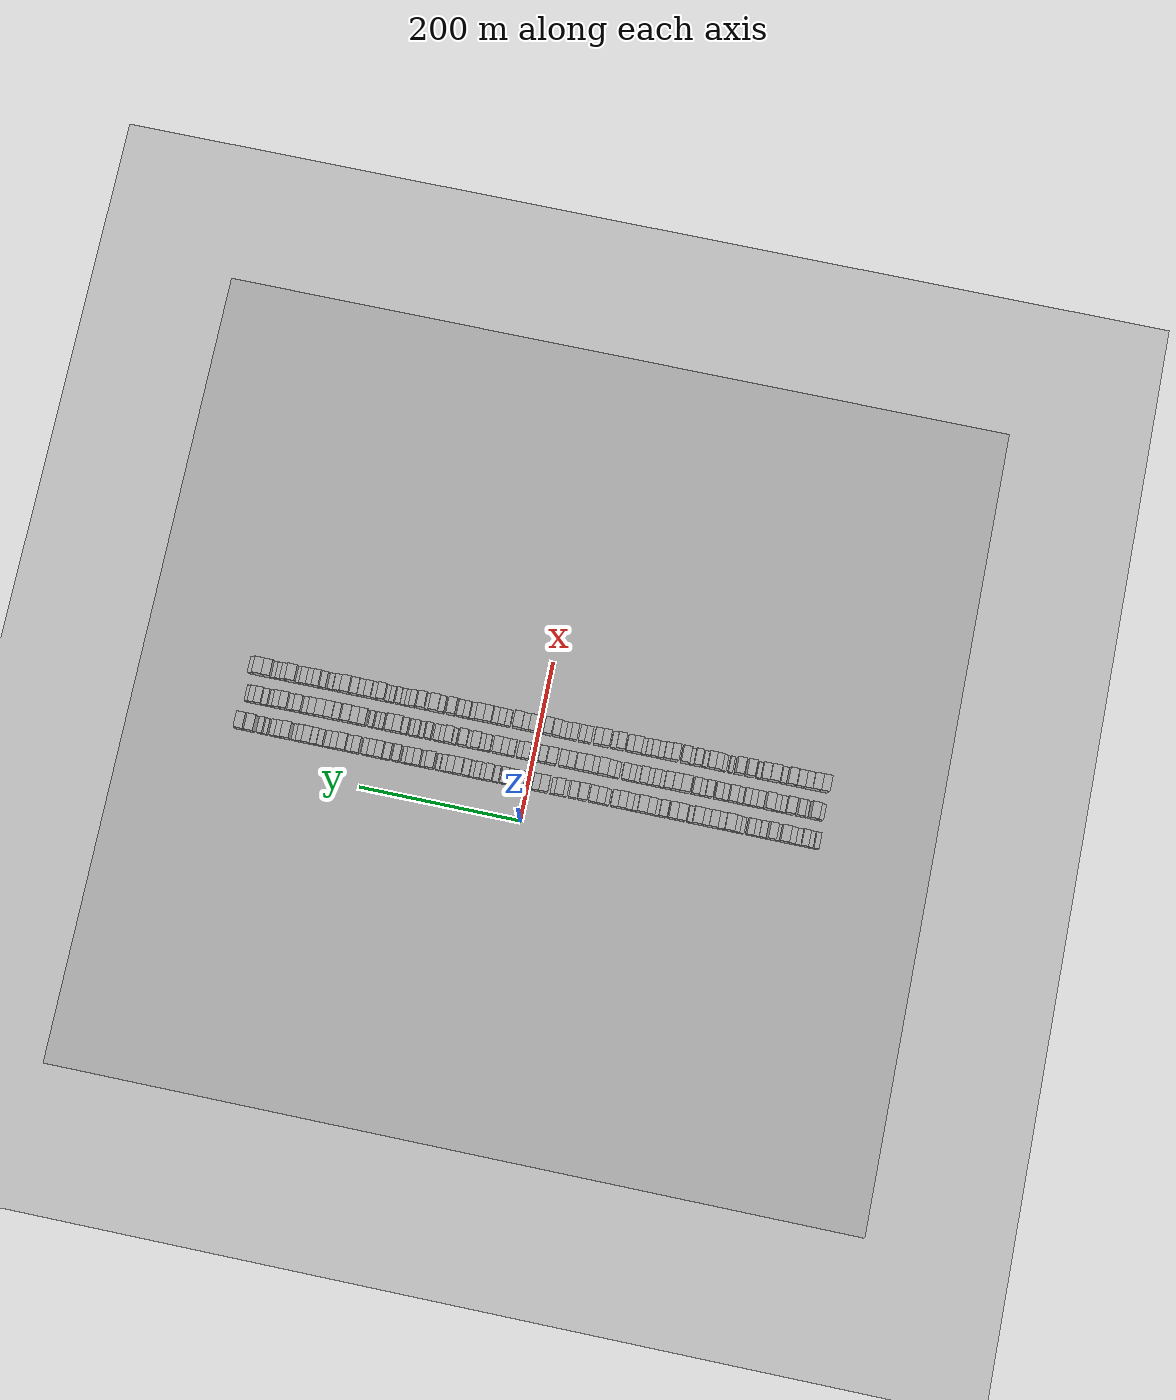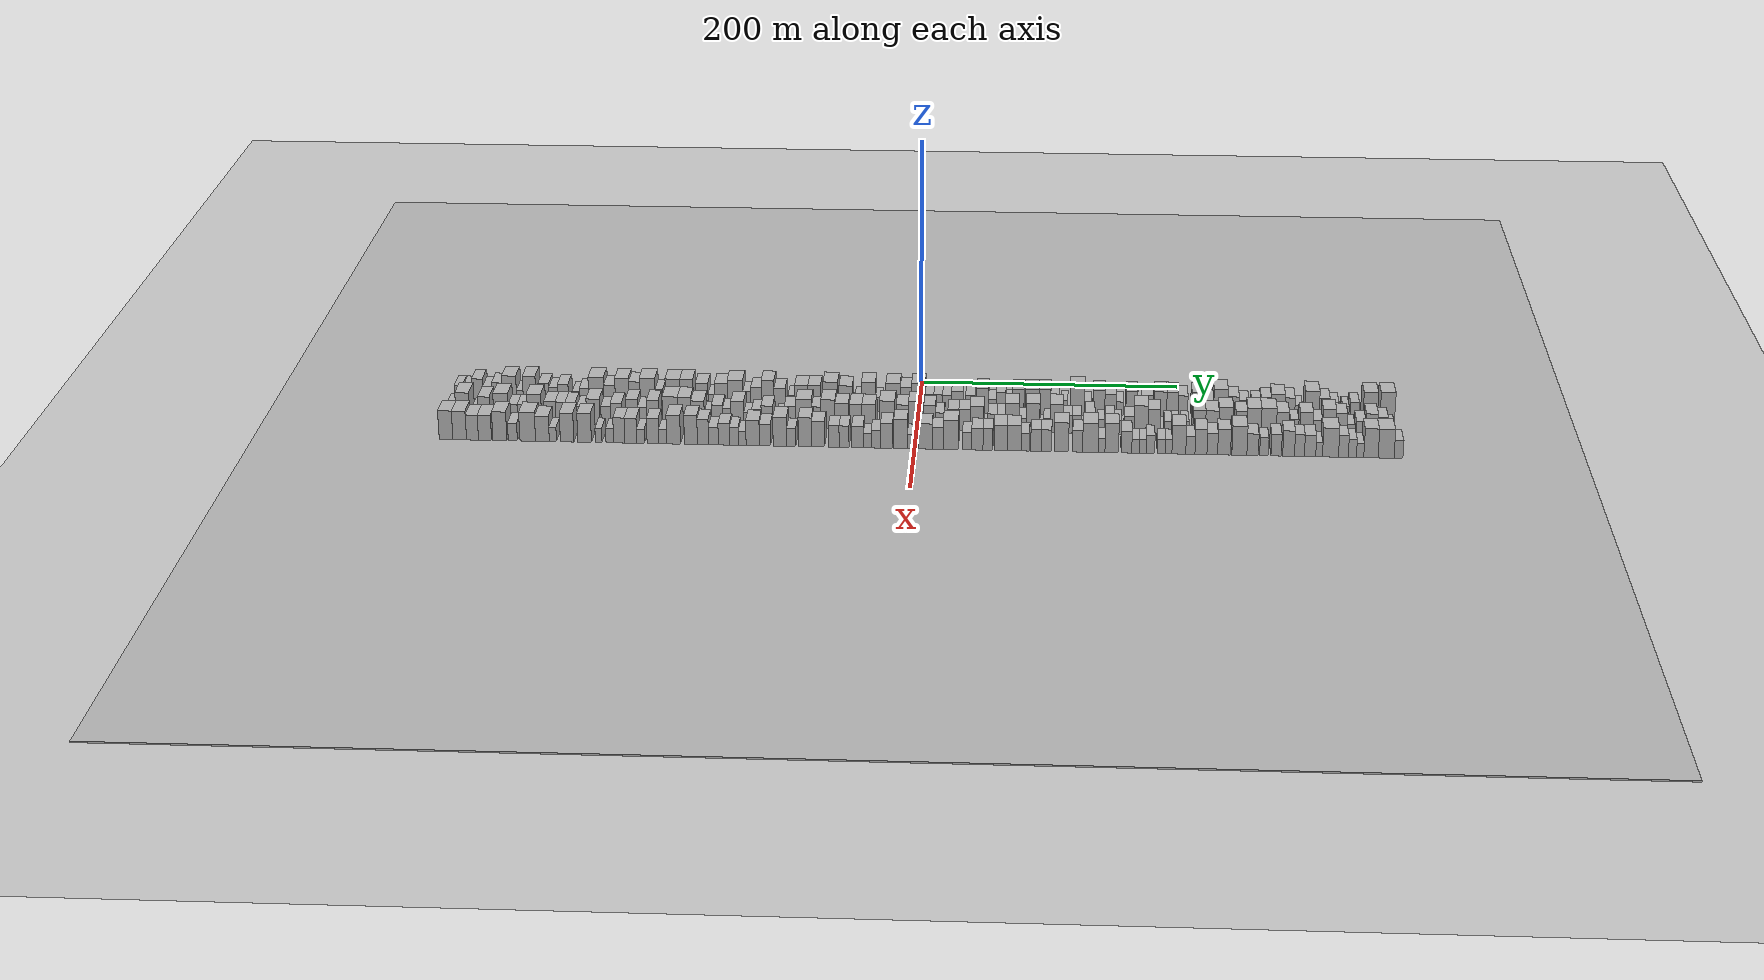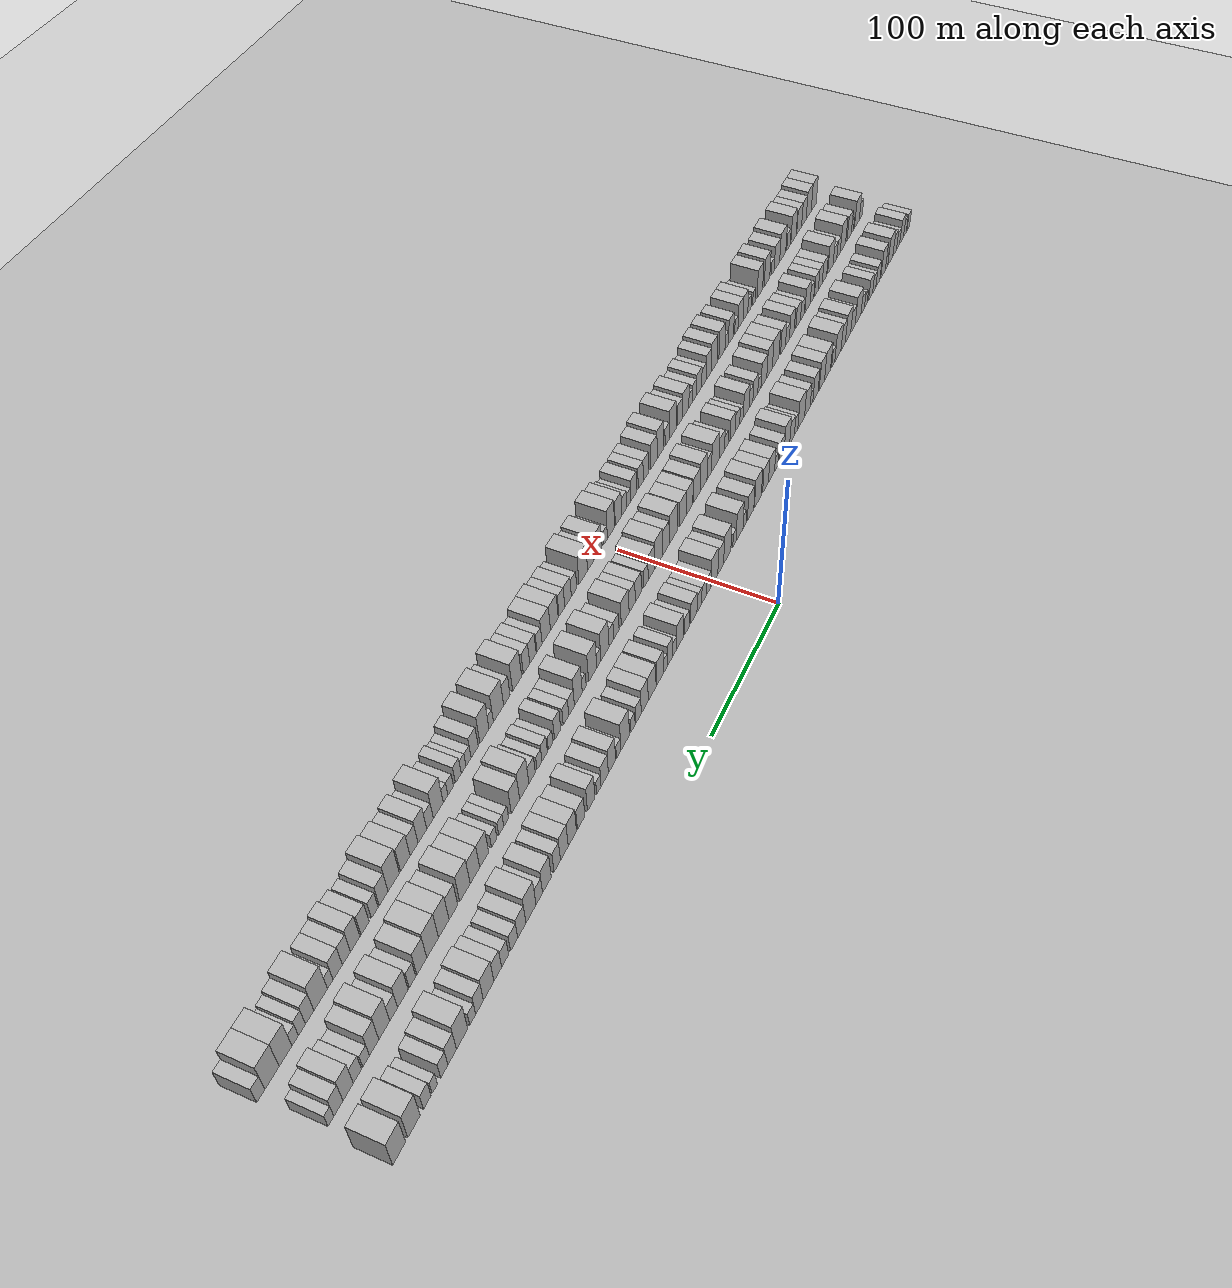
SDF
<?xml version="1.0" encoding="utf-8"?>

<sdf version="1.6">

   <world name="default">

      <gui fullscreen="0">

         <camera name="user_camera">

            <pose>-15 0 4.57585 0 0 0</pose>

            <view_controller>orbit</view_controller>

         </camera>

      </gui>

      <scene>

         <sky>

           <clouds>

             <speed>12</speed>

           </clouds>

         </sky>

         <ambient>0.4 0.4 0.4 1</ambient>

         <background>0.7 0.7 0.7 1</background>

         <shadows>1</shadows>

      </scene>

      <gravity>0 0 -9.8066</gravity>

      <magnetic_field>6e-06 2.3e-05 -4.2e-05</magnetic_field>

      <physics default="0" name="default_physics" type="ode">

         <ode>

            <solver>

               <type>quick</type>

               <iters>10</iters>

               <sor>1.0</sor>

               <use_dynamic_moi_rescaling>0</use_dynamic_moi_rescaling>

            </solver>

            <constraints>

               <cfm>0</cfm>

               <erp>0.2</erp>

               <contact_max_correcting_vel>100</contact_max_correcting_vel>

               <contact_surface_layer>0.001</contact_surface_layer>

            </constraints>

         </ode>

         <max_step_size>0.004</max_step_size>

         <real_time_factor>1</real_time_factor>

         <real_time_update_rate>250</real_time_update_rate>

      </physics>

      <light name="sun" type="directional">

         <cast_shadows>1</cast_shadows>

         <pose>0 0 10 0 0 0</pose>

         <diffuse>0.8 0.8 0.8 1</diffuse>

         <specular>0.2 0.2 0.2 1</specular>

         <attenuation>

            <range>1000</range>

            <constant>0.9</constant>

            <linear>0.01</linear>

            <quadratic>0.001</quadratic>

         </attenuation>

         <direction>-0.5 0.1 -0.9</direction>

      </light>

      <include>

         <name>ground_plane_1</name>

         <uri>model://HANNAS_ground_plane</uri>

         <pose>0 0 0  0 0 0</pose>

      </include>

      <include>

         <name>ground_plane_2</name>

         <uri>model://HANNAS_ground_plane</uri>

         <pose>100 0 0  0 0 0</pose>

      </include>

      <model name="building_1">

         <static>1</static>

         <pose frame="">50.0000 -356.9173 0 0.000000 0.000000 0.000000</pose>

         <link name="link">

            <pose frame="">0 0 7.50 0 0 0</pose>

            <collision name="collision">

               <geometry>

                  <box>

                     <size>20.0000 6.1653 15.0000</size>

                  </box>

               </geometry>

               <max_contacts>10</max_contacts>

               <surface>

                  <contact>

                     <ode/>

                  </contact>

                  <bounce/>

                  <friction>

                     <torsional>

                        <ode/>

                     </torsional>

                     <ode/>

                  </friction>

               </surface>

            </collision>

            <visual name="visual">

               <cast_shadows>0</cast_shadows>

               <geometry>

                  <box>

                     <size>20.0000 6.1653 15.0000</size>

                  </box>

               </geometry>

               <material>

                  <script>

                     <uri>model://HANNAS_wall/materials/scripts</uri>

                     <uri>model://HANNAS_wall/materials/textures</uri>

                     <name>vrc/HANNAS_wall</name>

                  </script>

               </material>

            </visual>

            <self_collide>0</self_collide>

            <enable_wind>0</enable_wind>

            <kinematic>0</kinematic>

         </link>

      </model>

      <model name="building_2">

         <static>1</static>

         <pose frame="">50.0000 -349.4881 0 0.000000 0.000000 0.000000</pose>

         <link name="link">

            <pose frame="">0 0 7.50 0 0 0</pose>

            <collision name="collision">

               <geometry>

                  <box>

                     <size>20.0000 6.6932 15.0000</size>

                  </box>

               </geometry>

               <max_contacts>10</max_contacts>

               <surface>

                  <contact>

                     <ode/>

                  </contact>

                  <bounce/>

                  <friction>

                     <torsional>

                        <ode/>

                     </torsional>

                     <ode/>

                  </friction>

               </surface>

            </collision>

            <visual name="visual">

               <cast_shadows>0</cast_shadows>

               <geometry>

                  <box>

                     <size>20.0000 6.6932 15.0000</size>

                  </box>

               </geometry>

               <material>

                  <script>

                     <uri>model://HANNAS_wall/materials/scripts</uri>

                     <uri>model://HANNAS_wall/materials/textures</uri>

                     <name>vrc/HANNAS_wall</name>

                  </script>

               </material>

            </visual>

            <self_collide>0</self_collide>

            <enable_wind>0</enable_wind>

            <kinematic>0</kinematic>

         </link>

      </model>

      <model name="building_3">

         <static>1</static>

         <pose frame="">50.0000 -341.9118 0 0.000000 0.000000 0.000000</pose>

         <link name="link">

            <pose frame="">0 0 10.50 0 0 0</pose>

            <collision name="collision">

               <geometry>

                  <box>

                     <size>20.0000 8.4594 21.0000</size>

                  </box>

               </geometry>

               <max_contacts>10</max_contacts>

               <surface>

                  <contact>

                     <ode/>

                  </contact>

                  <bounce/>

                  <friction>

                     <torsional>

                        <ode/>

                     </torsional>

                     <ode/>

                  </friction>

               </surface>

            </collision>

            <visual name="visual">

               <cast_shadows>0</cast_shadows>

               <geometry>

                  <box>

                     <size>20.0000 8.4594 21.0000</size>

                  </box>

               </geometry>

               <material>

                  <script>

                     <uri>model://HANNAS_wall/materials/scripts</uri>

                     <uri>model://HANNAS_wall/materials/textures</uri>

                     <name>vrc/HANNAS_wall</name>

                  </script>

               </material>

            </visual>

            <self_collide>0</self_collide>

            <enable_wind>0</enable_wind>

            <kinematic>0</kinematic>

         </link>

      </model>

      <model name="building_4">

         <static>1</static>

         <pose frame="">50.0000 -334.1779 0 0.000000 0.000000 0.000000</pose>

         <link name="link">

            <pose frame="">0 0 7.50 0 0 0</pose>

            <collision name="collision">

               <geometry>

                  <box>

                     <size>20.0000 7.0084 15.0000</size>

                  </box>

               </geometry>

               <max_contacts>10</max_contacts>

               <surface>

                  <contact>

                     <ode/>

                  </contact>

                  <bounce/>

                  <friction>

                     <torsional>

                        <ode/>

                     </torsional>

                     <ode/>

                  </friction>

               </surface>

            </collision>

            <visual name="visual">

               <cast_shadows>0</cast_shadows>

               <geometry>

                  <box>

                     <size>20.0000 7.0084 15.0000</size>

                  </box>

               </geometry>

               <material>

                  <script>

                     <uri>model://HANNAS_wall/materials/scripts</uri>

                     <uri>model://HANNAS_wall/materials/textures</uri>

                     <name>vrc/HANNAS_wall</name>

                  </script>

               </material>

            </visual>

            <self_collide>0</self_collide>

            <enable_wind>0</enable_wind>

            <kinematic>0</kinematic>

         </link>

      </model>

      <model name="building_5">

         <static>1</static>

         <pose frame="">50.0000 -326.5904 0 0.000000 0.000000 0.000000</pose>

         <link name="link">

            <pose frame="">0 0 9.00 0 0 0</pose>

            <collision name="collision">

               <geometry>

                  <box>

                     <size>20.0000 8.1666 18.0000</size>

                  </box>

               </geometry>

               <max_contacts>10</max_contacts>

               <surface>

                  <contact>

                     <ode/>

                  </contact>

                  <bounce/>

                  <friction>

                     <torsional>

                        <ode/>

                     </torsional>

                     <ode/>

                  </friction>

               </surface>

            </collision>

            <visual name="visual">

               <cast_shadows>0</cast_shadows>

               <geometry>

                  <box>

                     <size>20.0000 8.1666 18.0000</size>

                  </box>

               </geometry>

               <material>

                  <script>

                     <uri>model://HANNAS_wall/materials/scripts</uri>

                     <uri>model://HANNAS_wall/materials/textures</uri>

                     <name>vrc/HANNAS_wall</name>

                  </script>

               </material>

            </visual>

            <self_collide>0</self_collide>

            <enable_wind>0</enable_wind>

            <kinematic>0</kinematic>

         </link>

      </model>

      <model name="building_6">

         <static>1</static>

         <pose frame="">50.0000 -317.0512 0 0.000000 0.000000 0.000000</pose>

         <link name="link">

            <pose frame="">0 0 12.00 0 0 0</pose>

            <collision name="collision">

               <geometry>

                  <box>

                     <size>20.0000 10.9119 24.0000</size>

                  </box>

               </geometry>

               <max_contacts>10</max_contacts>

               <surface>

                  <contact>

                     <ode/>

                  </contact>

                  <bounce/>

                  <friction>

                     <torsional>

                        <ode/>

                     </torsional>

                     <ode/>

                  </friction>

               </surface>

            </collision>

            <visual name="visual">

               <cast_shadows>0</cast_shadows>

               <geometry>

                  <box>

                     <size>20.0000 10.9119 24.0000</size>

                  </box>

               </geometry>

               <material>

                  <script>

                     <uri>model://HANNAS_wall/materials/scripts</uri>

                     <uri>model://HANNAS_wall/materials/textures</uri>

                     <name>vrc/HANNAS_wall</name>

                  </script>

               </material>

            </visual>

            <self_collide>0</self_collide>

            <enable_wind>0</enable_wind>

            <kinematic>0</kinematic>

         </link>

      </model>

      <model name="building_7">

         <static>1</static>

         <pose frame="">50.0000 -309.0127 0 0.000000 0.000000 0.000000</pose>

         <link name="link">

            <pose frame="">0 0 6.00 0 0 0</pose>

            <collision name="collision">

               <geometry>

                  <box>

                     <size>20.0000 5.1651 12.0000</size>

                  </box>

               </geometry>

               <max_contacts>10</max_contacts>

               <surface>

                  <contact>

                     <ode/>

                  </contact>

                  <bounce/>

                  <friction>

                     <torsional>

                        <ode/>

                     </torsional>

                     <ode/>

                  </friction>

               </surface>

            </collision>

            <visual name="visual">

               <cast_shadows>0</cast_shadows>

               <geometry>

                  <box>

                     <size>20.0000 5.1651 12.0000</size>

                  </box>

               </geometry>

               <material>

                  <script>

                     <uri>model://HANNAS_wall/materials/scripts</uri>

                     <uri>model://HANNAS_wall/materials/textures</uri>

                     <name>vrc/HANNAS_wall</name>

                  </script>

               </material>

            </visual>

            <self_collide>0</self_collide>

            <enable_wind>0</enable_wind>

            <kinematic>0</kinematic>

         </link>

      </model>

      <model name="building_8">

         <static>1</static>

         <pose frame="">50.0000 -301.5000 0 0.000000 0.000000 0.000000</pose>

         <link name="link">

            <pose frame="">0 0 12.00 0 0 0</pose>

            <collision name="collision">

               <geometry>

                  <box>

                     <size>20.0000 9.8603 24.0000</size>

                  </box>

               </geometry>

               <max_contacts>10</max_contacts>

               <surface>

                  <contact>

                     <ode/>

                  </contact>

                  <bounce/>

                  <friction>

                     <torsional>

                        <ode/>

                     </torsional>

                     <ode/>

                  </friction>

               </surface>

            </collision>

            <visual name="visual">

               <cast_shadows>0</cast_shadows>

               <geometry>

                  <box>

                     <size>20.0000 9.8603 24.0000</size>

                  </box>

               </geometry>

               <material>

                  <script>

                     <uri>model://HANNAS_wall/materials/scripts</uri>

                     <uri>model://HANNAS_wall/materials/textures</uri>

                     <name>vrc/HANNAS_wall</name>

                  </script>

               </material>

            </visual>

            <self_collide>0</self_collide>

            <enable_wind>0</enable_wind>

            <kinematic>0</kinematic>

         </link>

      </model>

      <model name="building_9">

         <static>1</static>

         <pose frame="">50.0000 -290.4435 0 0.000000 0.000000 0.000000</pose>

         <link name="link">

            <pose frame="">0 0 9.00 0 0 0</pose>

            <collision name="collision">

               <geometry>

                  <box>

                     <size>20.0000 8.2526 18.0000</size>

                  </box>

               </geometry>

               <max_contacts>10</max_contacts>

               <surface>

                  <contact>

                     <ode/>

                  </contact>

                  <bounce/>

                  <friction>

                     <torsional>

                        <ode/>

                     </torsional>

                     <ode/>

                  </friction>

               </surface>

            </collision>

            <visual name="visual">

               <cast_shadows>0</cast_shadows>

               <geometry>

                  <box>

                     <size>20.0000 8.2526 18.0000</size>

                  </box>

               </geometry>

               <material>

                  <script>

                     <uri>model://HANNAS_wall/materials/scripts</uri>

                     <uri>model://HANNAS_wall/materials/textures</uri>

                     <name>vrc/HANNAS_wall</name>

                  </script>

               </material>

            </visual>

            <self_collide>0</self_collide>

            <enable_wind>0</enable_wind>

            <kinematic>0</kinematic>

         </link>

      </model>

      <model name="building_10">

         <static>1</static>

         <pose frame="">50.0000 -282.8231 0 0.000000 0.000000 0.000000</pose>

         <link name="link">

            <pose frame="">0 0 7.50 0 0 0</pose>

            <collision name="collision">

               <geometry>

                  <box>

                     <size>20.0000 6.9883 15.0000</size>

                  </box>

               </geometry>

               <max_contacts>10</max_contacts>

               <surface>

                  <contact>

                     <ode/>

                  </contact>

                  <bounce/>

                  <friction>

                     <torsional>

                        <ode/>

                     </torsional>

                     <ode/>

                  </friction>

               </surface>

            </collision>

            <visual name="visual">

               <cast_shadows>0</cast_shadows>

               <geometry>

                  <box>

                     <size>20.0000 6.9883 15.0000</size>

                  </box>

               </geometry>

               <material>

                  <script>

                     <uri>model://HANNAS_wall/materials/scripts</uri>

                     <uri>model://HANNAS_wall/materials/textures</uri>

                     <name>vrc/HANNAS_wall</name>

                  </script>

               </material>

            </visual>

            <self_collide>0</self_collide>

            <enable_wind>0</enable_wind>

            <kinematic>0</kinematic>

         </link>

      </model>

      <model name="building_11">

         <static>1</static>

         <pose frame="">50.0000 -275.2648 0 0.000000 0.000000 0.000000</pose>

         <link name="link">

            <pose frame="">0 0 9.00 0 0 0</pose>

            <collision name="collision">

               <geometry>

                  <box>

                     <size>20.0000 8.1283 18.0000</size>

                  </box>

               </geometry>

               <max_contacts>10</max_contacts>

               <surface>

                  <contact>

                     <ode/>

                  </contact>

                  <bounce/>

                  <friction>

                     <torsional>

                        <ode/>

                     </torsional>

                     <ode/>

                  </friction>

               </surface>

            </collision>

            <visual name="visual">

               <cast_shadows>0</cast_shadows>

               <geometry>

                  <box>

                     <size>20.0000 8.1283 18.0000</size>

                  </box>

               </geometry>

               <material>

                  <script>

                     <uri>model://HANNAS_wall/materials/scripts</uri>

                     <uri>model://HANNAS_wall/materials/textures</uri>

                     <name>vrc/HANNAS_wall</name>

                  </script>

               </material>

            </visual>

            <self_collide>0</self_collide>

            <enable_wind>0</enable_wind>

            <kinematic>0</kinematic>

         </link>

      </model>

      <model name="building_12">

         <static>1</static>

         <pose frame="">50.0000 -265.3657 0 0.000000 0.000000 0.000000</pose>

         <link name="link">

            <pose frame="">0 0 6.00 0 0 0</pose>

            <collision name="collision">

               <geometry>

                  <box>

                     <size>20.0000 5.6699 12.0000</size>

                  </box>

               </geometry>

               <max_contacts>10</max_contacts>

               <surface>

                  <contact>

                     <ode/>

                  </contact>

                  <bounce/>

                  <friction>

                     <torsional>

                        <ode/>

                     </torsional>

                     <ode/>

                  </friction>

               </surface>

            </collision>

            <visual name="visual">

               <cast_shadows>0</cast_shadows>

               <geometry>

                  <box>

                     <size>20.0000 5.6699 12.0000</size>

                  </box>

               </geometry>

               <material>

                  <script>

                     <uri>model://HANNAS_wall/materials/scripts</uri>

                     <uri>model://HANNAS_wall/materials/textures</uri>

                     <name>vrc/HANNAS_wall</name>

                  </script>

               </material>

            </visual>

            <self_collide>0</self_collide>

            <enable_wind>0</enable_wind>

            <kinematic>0</kinematic>

         </link>

      </model>

      <model name="building_13">

         <static>1</static>

         <pose frame="">50.0000 -258.9882 0 0.000000 0.000000 0.000000</pose>

         <link name="link">

            <pose frame="">0 0 7.50 0 0 0</pose>

            <collision name="collision">

               <geometry>

                  <box>

                     <size>20.0000 7.0851 15.0000</size>

                  </box>

               </geometry>

               <max_contacts>10</max_contacts>

               <surface>

                  <contact>

                     <ode/>

                  </contact>

                  <bounce/>

                  <friction>

                     <torsional>

                        <ode/>

                     </torsional>

                     <ode/>

                  </friction>

               </surface>

            </collision>

            <visual name="visual">

               <cast_shadows>0</cast_shadows>

               <geometry>

                  <box>

                     <size>20.0000 7.0851 15.0000</size>

                  </box>

               </geometry>

               <material>

                  <script>

                     <uri>model://HANNAS_wall/materials/scripts</uri>

                     <uri>model://HANNAS_wall/materials/textures</uri>

                     <name>vrc/HANNAS_wall</name>

                  </script>

               </material>

            </visual>

            <self_collide>0</self_collide>

            <enable_wind>0</enable_wind>

            <kinematic>0</kinematic>

         </link>

      </model>

      <model name="building_14">

         <static>1</static>

         <pose frame="">50.0000 -249.4992 0 0.000000 0.000000 0.000000</pose>

         <link name="link">

            <pose frame="">0 0 12.00 0 0 0</pose>

            <collision name="collision">

               <geometry>

                  <box>

                     <size>20.0000 11.8929 24.0000</size>

                  </box>

               </geometry>

               <max_contacts>10</max_contacts>

               <surface>

                  <contact>

                     <ode/>

                  </contact>

                  <bounce/>

                  <friction>

                     <torsional>

                        <ode/>

                     </torsional>

                     <ode/>

                  </friction>

               </surface>

            </collision>

            <visual name="visual">

               <cast_shadows>0</cast_shadows>

               <geometry>

                  <box>

                     <size>20.0000 11.8929 24.0000</size>

                  </box>

               </geometry>

               <material>

                  <script>

                     <uri>model://HANNAS_wall/materials/scripts</uri>

                     <uri>model://HANNAS_wall/materials/textures</uri>

                     <name>vrc/HANNAS_wall</name>

                  </script>

               </material>

            </visual>

            <self_collide>0</self_collide>

            <enable_wind>0</enable_wind>

            <kinematic>0</kinematic>

         </link>

      </model>

      <model name="building_15">

         <static>1</static>

         <pose frame="">50.0000 -239.1527 0 0.000000 0.000000 0.000000</pose>

         <link name="link">

            <pose frame="">0 0 9.00 0 0 0</pose>

            <collision name="collision">

               <geometry>

                  <box>

                     <size>20.0000 8.8000 18.0000</size>

                  </box>

               </geometry>

               <max_contacts>10</max_contacts>

               <surface>

                  <contact>

                     <ode/>

                  </contact>

                  <bounce/>

                  <friction>

                     <torsional>

                        <ode/>

                     </torsional>

                     <ode/>

                  </friction>

               </surface>

            </collision>

            <visual name="visual">

               <cast_shadows>0</cast_shadows>

               <geometry>

                  <box>

                     <size>20.0000 8.8000 18.0000</size>

                  </box>

               </geometry>

               <material>

                  <script>

                     <uri>model://HANNAS_wall/materials/scripts</uri>

                     <uri>model://HANNAS_wall/materials/textures</uri>

                     <name>vrc/HANNAS_wall</name>

                  </script>

               </material>

            </visual>

            <self_collide>0</self_collide>

            <enable_wind>0</enable_wind>

            <kinematic>0</kinematic>

         </link>

      </model>

      <model name="building_16">

         <static>1</static>

         <pose frame="">50.0000 -229.4747 0 0.000000 0.000000 0.000000</pose>

         <link name="link">

            <pose frame="">0 0 12.00 0 0 0</pose>

            <collision name="collision">

               <geometry>

                  <box>

                     <size>20.0000 10.5560 24.0000</size>

                  </box>

               </geometry>

               <max_contacts>10</max_contacts>

               <surface>

                  <contact>

                     <ode/>

                  </contact>

                  <bounce/>

                  <friction>

                     <torsional>

                        <ode/>

                     </torsional>

                     <ode/>

                  </friction>

               </surface>

            </collision>

            <visual name="visual">

               <cast_shadows>0</cast_shadows>

               <geometry>

                  <box>

                     <size>20.0000 10.5560 24.0000</size>

                  </box>

               </geometry>

               <material>

                  <script>

                     <uri>model://HANNAS_wall/materials/scripts</uri>

                     <uri>model://HANNAS_wall/materials/textures</uri>

                     <name>vrc/HANNAS_wall</name>

                  </script>

               </material>

            </visual>

            <self_collide>0</self_collide>

            <enable_wind>0</enable_wind>

            <kinematic>0</kinematic>

         </link>

      </model>

      <model name="building_17">

         <static>1</static>

         <pose frame="">50.0000 -219.9631 0 0.000000 0.000000 0.000000</pose>

         <link name="link">

            <pose frame="">0 0 10.50 0 0 0</pose>

            <collision name="collision">

               <geometry>

                  <box>

                     <size>20.0000 8.4672 21.0000</size>

                  </box>

               </geometry>

               <max_contacts>10</max_contacts>

               <surface>

                  <contact>

                     <ode/>

                  </contact>

                  <bounce/>

                  <friction>

                     <torsional>

                        <ode/>

                     </torsional>

                     <ode/>

                  </friction>

               </surface>

            </collision>

            <visual name="visual">

               <cast_shadows>0</cast_shadows>

               <geometry>

                  <box>

                     <size>20.0000 8.4672 21.0000</size>

                  </box>

               </geometry>

               <material>

                  <script>

                     <uri>model://HANNAS_wall/materials/scripts</uri>

                     <uri>model://HANNAS_wall/materials/textures</uri>

                     <name>vrc/HANNAS_wall</name>

                  </script>

               </material>

            </visual>

            <self_collide>0</self_collide>

            <enable_wind>0</enable_wind>

            <kinematic>0</kinematic>

         </link>

      </model>

      <model name="building_18">

         <static>1</static>

         <pose frame="">50.0000 -209.7515 0 0.000000 0.000000 0.000000</pose>

         <link name="link">

            <pose frame="">0 0 12.00 0 0 0</pose>

            <collision name="collision">

               <geometry>

                  <box>

                     <size>20.0000 11.9559 24.0000</size>

                  </box>

               </geometry>

               <max_contacts>10</max_contacts>

               <surface>

                  <contact>

                     <ode/>

                  </contact>

                  <bounce/>

                  <friction>

                     <torsional>

                        <ode/>

                     </torsional>

                     <ode/>

                  </friction>

               </surface>

            </collision>

            <visual name="visual">

               <cast_shadows>0</cast_shadows>

               <geometry>

                  <box>

                     <size>20.0000 11.9559 24.0000</size>

                  </box>

               </geometry>

               <material>

                  <script>

                     <uri>model://HANNAS_wall/materials/scripts</uri>

                     <uri>model://HANNAS_wall/materials/textures</uri>

                     <name>vrc/HANNAS_wall</name>

                  </script>

               </material>

            </visual>

            <self_collide>0</self_collide>

            <enable_wind>0</enable_wind>

            <kinematic>0</kinematic>

         </link>

      </model>

      <model name="building_19">

         <static>1</static>

         <pose frame="">50.0000 -200.7639 0 0.000000 0.000000 0.000000</pose>

         <link name="link">

            <pose frame="">0 0 7.50 0 0 0</pose>

            <collision name="collision">

               <geometry>

                  <box>

                     <size>20.0000 6.0193 15.0000</size>

                  </box>

               </geometry>

               <max_contacts>10</max_contacts>

               <surface>

                  <contact>

                     <ode/>

                  </contact>

                  <bounce/>

                  <friction>

                     <torsional>

                        <ode/>

                     </torsional>

                     <ode/>

                  </friction>

               </surface>

            </collision>

            <visual name="visual">

               <cast_shadows>0</cast_shadows>

               <geometry>

                  <box>

                     <size>20.0000 6.0193 15.0000</size>

                  </box>

               </geometry>

               <material>

                  <script>

                     <uri>model://HANNAS_wall/materials/scripts</uri>

                     <uri>model://HANNAS_wall/materials/textures</uri>

                     <name>vrc/HANNAS_wall</name>

                  </script>

               </material>

            </visual>

            <self_collide>0</self_collide>

            <enable_wind>0</enable_wind>

            <kinematic>0</kinematic>

         </link>

      </model>

      <model name="building_20">

         <static>1</static>

         <pose frame="">50.0000 -190.0503 0 0.000000 0.000000 0.000000</pose>

         <link name="link">

            <pose frame="">0 0 12.00 0 0 0</pose>

            <collision name="collision">

               <geometry>

                  <box>

                     <size>20.0000 11.4079 24.0000</size>

                  </box>

               </geometry>

               <max_contacts>10</max_contacts>

               <surface>

                  <contact>

                     <ode/>

                  </contact>

                  <bounce/>

                  <friction>

                     <torsional>

                        <ode/>

                     </torsional>

                     <ode/>

                  </friction>

               </surface>

            </collision>

            <visual name="visual">

               <cast_shadows>0</cast_shadows>

               <geometry>

                  <box>

                     <size>20.0000 11.4079 24.0000</size>

                  </box>

               </geometry>

               <material>

                  <script>

                     <uri>model://HANNAS_wall/materials/scripts</uri>

                     <uri>model://HANNAS_wall/materials/textures</uri>

                     <name>vrc/HANNAS_wall</name>

                  </script>

               </material>

            </visual>

            <self_collide>0</self_collide>

            <enable_wind>0</enable_wind>

            <kinematic>0</kinematic>

         </link>

      </model>

      <model name="building_21">

         <static>1</static>

         <pose frame="">50.0000 -179.3516 0 0.000000 0.000000 0.000000</pose>

         <link name="link">

            <pose frame="">0 0 12.00 0 0 0</pose>

            <collision name="collision">

               <geometry>

                  <box>

                     <size>20.0000 9.9894 24.0000</size>

                  </box>

               </geometry>

               <max_contacts>10</max_contacts>

               <surface>

                  <contact>

                     <ode/>

                  </contact>

                  <bounce/>

                  <friction>

                     <torsional>

                        <ode/>

                     </torsional>

                     <ode/>

                  </friction>

               </surface>

            </collision>

            <visual name="visual">

               <cast_shadows>0</cast_shadows>

               <geometry>

                  <box>

                     <size>20.0000 9.9894 24.0000</size>

                  </box>

               </geometry>

               <material>

                  <script>

                     <uri>model://HANNAS_wall/materials/scripts</uri>

                     <uri>model://HANNAS_wall/materials/textures</uri>

                     <name>vrc/HANNAS_wall</name>

                  </script>

               </material>

            </visual>

            <self_collide>0</self_collide>

            <enable_wind>0</enable_wind>

            <kinematic>0</kinematic>

         </link>

      </model>

      <model name="building_22">

         <static>1</static>

         <pose frame="">50.0000 -167.5594 0 0.000000 0.000000 0.000000</pose>

         <link name="link">

            <pose frame="">0 0 10.50 0 0 0</pose>

            <collision name="collision">

               <geometry>

                  <box>

                     <size>20.0000 9.5950 21.0000</size>

                  </box>

               </geometry>

               <max_contacts>10</max_contacts>

               <surface>

                  <contact>

                     <ode/>

                  </contact>

                  <bounce/>

                  <friction>

                     <torsional>

                        <ode/>

                     </torsional>

                     <ode/>

                  </friction>

               </surface>

            </collision>

            <visual name="visual">

               <cast_shadows>0</cast_shadows>

               <geometry>

                  <box>

                     <size>20.0000 9.5950 21.0000</size>

                  </box>

               </geometry>

               <material>

                  <script>

                     <uri>model://HANNAS_wall/materials/scripts</uri>

                     <uri>model://HANNAS_wall/materials/textures</uri>

                     <name>vrc/HANNAS_wall</name>

                  </script>

               </material>

            </visual>

            <self_collide>0</self_collide>

            <enable_wind>0</enable_wind>

            <kinematic>0</kinematic>

         </link>

      </model>

      <model name="building_23">

         <static>1</static>

         <pose frame="">50.0000 -160.2482 0 0.000000 0.000000 0.000000</pose>

         <link name="link">

            <pose frame="">0 0 6.00 0 0 0</pose>

            <collision name="collision">

               <geometry>

                  <box>

                     <size>20.0000 5.0275 12.0000</size>

                  </box>

               </geometry>

               <max_contacts>10</max_contacts>

               <surface>

                  <contact>

                     <ode/>

                  </contact>

                  <bounce/>

                  <friction>

                     <torsional>

                        <ode/>

                     </torsional>

                     <ode/>

                  </friction>

               </surface>

            </collision>

            <visual name="visual">

               <cast_shadows>0</cast_shadows>

               <geometry>

                  <box>

                     <size>20.0000 5.0275 12.0000</size>

                  </box>

               </geometry>

               <material>

                  <script>

                     <uri>model://HANNAS_wall/materials/scripts</uri>

                     <uri>model://HANNAS_wall/materials/textures</uri>

                     <name>vrc/HANNAS_wall</name>

                  </script>

               </material>

            </visual>

            <self_collide>0</self_collide>

            <enable_wind>0</enable_wind>

            <kinematic>0</kinematic>

         </link>

      </model>

      <model name="building_24">

         <static>1</static>

         <pose frame="">50.0000 -152.7383 0 0.000000 0.000000 0.000000</pose>

         <link name="link">

            <pose frame="">0 0 10.50 0 0 0</pose>

            <collision name="collision">

               <geometry>

                  <box>

                     <size>20.0000 9.9922 21.0000</size>

                  </box>

               </geometry>

               <max_contacts>10</max_contacts>

               <surface>

                  <contact>

                     <ode/>

                  </contact>

                  <bounce/>

                  <friction>

                     <torsional>

                        <ode/>

                     </torsional>

                     <ode/>

                  </friction>

               </surface>

            </collision>

            <visual name="visual">

               <cast_shadows>0</cast_shadows>

               <geometry>

                  <box>

                     <size>20.0000 9.9922 21.0000</size>

                  </box>

               </geometry>

               <material>

                  <script>

                     <uri>model://HANNAS_wall/materials/scripts</uri>

                     <uri>model://HANNAS_wall/materials/textures</uri>

                     <name>vrc/HANNAS_wall</name>

                  </script>

               </material>

            </visual>

            <self_collide>0</self_collide>

            <enable_wind>0</enable_wind>

            <kinematic>0</kinematic>

         </link>

      </model>

      <model name="building_25">

         <static>1</static>

         <pose frame="">50.0000 -141.7926 0 0.000000 0.000000 0.000000</pose>

         <link name="link">

            <pose frame="">0 0 12.00 0 0 0</pose>

            <collision name="collision">

               <geometry>

                  <box>

                     <size>20.0000 11.8991 24.0000</size>

                  </box>

               </geometry>

               <max_contacts>10</max_contacts>

               <surface>

                  <contact>

                     <ode/>

                  </contact>

                  <bounce/>

                  <friction>

                     <torsional>

                        <ode/>

                     </torsional>

                     <ode/>

                  </friction>

               </surface>

            </collision>

            <visual name="visual">

               <cast_shadows>0</cast_shadows>

               <geometry>

                  <box>

                     <size>20.0000 11.8991 24.0000</size>

                  </box>

               </geometry>

               <material>

                  <script>

                     <uri>model://HANNAS_wall/materials/scripts</uri>

                     <uri>model://HANNAS_wall/materials/textures</uri>

                     <name>vrc/HANNAS_wall</name>

                  </script>

               </material>

            </visual>

            <self_collide>0</self_collide>

            <enable_wind>0</enable_wind>

            <kinematic>0</kinematic>

         </link>

      </model>

      <model name="building_26">

         <static>1</static>

         <pose frame="">50.0000 -132.7753 0 0.000000 0.000000 0.000000</pose>

         <link name="link">

            <pose frame="">0 0 7.50 0 0 0</pose>

            <collision name="collision">

               <geometry>

                  <box>

                     <size>20.0000 6.1356 15.0000</size>

                  </box>

               </geometry>

               <max_contacts>10</max_contacts>

               <surface>

                  <contact>

                     <ode/>

                  </contact>

                  <bounce/>

                  <friction>

                     <torsional>

                        <ode/>

                     </torsional>

                     <ode/>

                  </friction>

               </surface>

            </collision>

            <visual name="visual">

               <cast_shadows>0</cast_shadows>

               <geometry>

                  <box>

                     <size>20.0000 6.1356 15.0000</size>

                  </box>

               </geometry>

               <material>

                  <script>

                     <uri>model://HANNAS_wall/materials/scripts</uri>

                     <uri>model://HANNAS_wall/materials/textures</uri>

                     <name>vrc/HANNAS_wall</name>

                  </script>

               </material>

            </visual>

            <self_collide>0</self_collide>

            <enable_wind>0</enable_wind>

            <kinematic>0</kinematic>

         </link>

      </model>

      <model name="building_27">

         <static>1</static>

         <pose frame="">50.0000 -125.6020 0 0.000000 0.000000 0.000000</pose>

         <link name="link">

            <pose frame="">0 0 9.00 0 0 0</pose>

            <collision name="collision">

               <geometry>

                  <box>

                     <size>20.0000 8.2110 18.0000</size>

                  </box>

               </geometry>

               <max_contacts>10</max_contacts>

               <surface>

                  <contact>

                     <ode/>

                  </contact>

                  <bounce/>

                  <friction>

                     <torsional>

                        <ode/>

                     </torsional>

                     <ode/>

                  </friction>

               </surface>

            </collision>

            <visual name="visual">

               <cast_shadows>0</cast_shadows>

               <geometry>

                  <box>

                     <size>20.0000 8.2110 18.0000</size>

                  </box>

               </geometry>

               <material>

                  <script>

                     <uri>model://HANNAS_wall/materials/scripts</uri>

                     <uri>model://HANNAS_wall/materials/textures</uri>

                     <name>vrc/HANNAS_wall</name>

                  </script>

               </material>

            </visual>

            <self_collide>0</self_collide>

            <enable_wind>0</enable_wind>

            <kinematic>0</kinematic>

         </link>

      </model>

      <model name="building_28">

         <static>1</static>

         <pose frame="">50.0000 -116.6158 0 0.000000 0.000000 0.000000</pose>

         <link name="link">

            <pose frame="">0 0 12.00 0 0 0</pose>

            <collision name="collision">

               <geometry>

                  <box>

                     <size>20.0000 9.7613 24.0000</size>

                  </box>

               </geometry>

               <max_contacts>10</max_contacts>

               <surface>

                  <contact>

                     <ode/>

                  </contact>

                  <bounce/>

                  <friction>

                     <torsional>

                        <ode/>

                     </torsional>

                     <ode/>

                  </friction>

               </surface>

            </collision>

            <visual name="visual">

               <cast_shadows>0</cast_shadows>

               <geometry>

                  <box>

                     <size>20.0000 9.7613 24.0000</size>

                  </box>

               </geometry>

               <material>

                  <script>

                     <uri>model://HANNAS_wall/materials/scripts</uri>

                     <uri>model://HANNAS_wall/materials/textures</uri>

                     <name>vrc/HANNAS_wall</name>

                  </script>

               </material>

            </visual>

            <self_collide>0</self_collide>

            <enable_wind>0</enable_wind>

            <kinematic>0</kinematic>

         </link>

      </model>

      <model name="building_29">

         <static>1</static>

         <pose frame="">50.0000 -107.3599 0 0.000000 0.000000 0.000000</pose>

         <link name="link">

            <pose frame="">0 0 9.00 0 0 0</pose>

            <collision name="collision">

               <geometry>

                  <box>

                     <size>20.0000 8.7504 18.0000</size>

                  </box>

               </geometry>

               <max_contacts>10</max_contacts>

               <surface>

                  <contact>

                     <ode/>

                  </contact>

                  <bounce/>

                  <friction>

                     <torsional>

                        <ode/>

                     </torsional>

                     <ode/>

                  </friction>

               </surface>

            </collision>

            <visual name="visual">

               <cast_shadows>0</cast_shadows>

               <geometry>

                  <box>

                     <size>20.0000 8.7504 18.0000</size>

                  </box>

               </geometry>

               <material>

                  <script>

                     <uri>model://HANNAS_wall/materials/scripts</uri>

                     <uri>model://HANNAS_wall/materials/textures</uri>

                     <name>vrc/HANNAS_wall</name>

                  </script>

               </material>

            </visual>

            <self_collide>0</self_collide>

            <enable_wind>0</enable_wind>

            <kinematic>0</kinematic>

         </link>

      </model>

      <model name="building_30">

         <static>1</static>

         <pose frame="">50.0000 -98.3013 0 0.000000 0.000000 0.000000</pose>

         <link name="link">

            <pose frame="">0 0 6.00 0 0 0</pose>

            <collision name="collision">

               <geometry>

                  <box>

                     <size>20.0000 5.3669 12.0000</size>

                  </box>

               </geometry>

               <max_contacts>10</max_contacts>

               <surface>

                  <contact>

                     <ode/>

                  </contact>

                  <bounce/>

                  <friction>

                     <torsional>

                        <ode/>

                     </torsional>

                     <ode/>

                  </friction>

               </surface>

            </collision>

            <visual name="visual">

               <cast_shadows>0</cast_shadows>

               <geometry>

                  <box>

                     <size>20.0000 5.3669 12.0000</size>

                  </box>

               </geometry>

               <material>

                  <script>

                     <uri>model://HANNAS_wall/materials/scripts</uri>

                     <uri>model://HANNAS_wall/materials/textures</uri>

                     <name>vrc/HANNAS_wall</name>

                  </script>

               </material>

            </visual>

            <self_collide>0</self_collide>

            <enable_wind>0</enable_wind>

            <kinematic>0</kinematic>

         </link>

      </model>

      <model name="building_31">

         <static>1</static>

         <pose frame="">50.0000 -90.5469 0 0.000000 0.000000 0.000000</pose>

         <link name="link">

            <pose frame="">0 0 10.50 0 0 0</pose>

            <collision name="collision">

               <geometry>

                  <box>

                     <size>20.0000 10.1420 21.0000</size>

                  </box>

               </geometry>

               <max_contacts>10</max_contacts>

               <surface>

                  <contact>

                     <ode/>

                  </contact>

                  <bounce/>

                  <friction>

                     <torsional>

                        <ode/>

                     </torsional>

                     <ode/>

                  </friction>

               </surface>

            </collision>

            <visual name="visual">

               <cast_shadows>0</cast_shadows>

               <geometry>

                  <box>

                     <size>20.0000 10.1420 21.0000</size>

                  </box>

               </geometry>

               <material>

                  <script>

                     <uri>model://HANNAS_wall/materials/scripts</uri>

                     <uri>model://HANNAS_wall/materials/textures</uri>

                     <name>vrc/HANNAS_wall</name>

                  </script>

               </material>

            </visual>

            <self_collide>0</self_collide>

            <enable_wind>0</enable_wind>

            <kinematic>0</kinematic>

         </link>

      </model>

      <model name="building_32">

         <static>1</static>

         <pose frame="">50.0000 -80.6466 0 0.000000 0.000000 0.000000</pose>

         <link name="link">

            <pose frame="">0 0 10.50 0 0 0</pose>

            <collision name="collision">

               <geometry>

                  <box>

                     <size>20.0000 9.6586 21.0000</size>

                  </box>

               </geometry>

               <max_contacts>10</max_contacts>

               <surface>

                  <contact>

                     <ode/>

                  </contact>

                  <bounce/>

                  <friction>

                     <torsional>

                        <ode/>

                     </torsional>

                     <ode/>

                  </friction>

               </surface>

            </collision>

            <visual name="visual">

               <cast_shadows>0</cast_shadows>

               <geometry>

                  <box>

                     <size>20.0000 9.6586 21.0000</size>

                  </box>

               </geometry>

               <material>

                  <script>

                     <uri>model://HANNAS_wall/materials/scripts</uri>

                     <uri>model://HANNAS_wall/materials/textures</uri>

                     <name>vrc/HANNAS_wall</name>

                  </script>

               </material>

            </visual>

            <self_collide>0</self_collide>

            <enable_wind>0</enable_wind>

            <kinematic>0</kinematic>

         </link>

      </model>

      <model name="building_33">

         <static>1</static>

         <pose frame="">50.0000 -68.1650 0 0.000000 0.000000 0.000000</pose>

         <link name="link">

            <pose frame="">0 0 12.00 0 0 0</pose>

            <collision name="collision">

               <geometry>

                  <box>

                     <size>20.0000 11.3044 24.0000</size>

                  </box>

               </geometry>

               <max_contacts>10</max_contacts>

               <surface>

                  <contact>

                     <ode/>

                  </contact>

                  <bounce/>

                  <friction>

                     <torsional>

                        <ode/>

                     </torsional>

                     <ode/>

                  </friction>

               </surface>

            </collision>

            <visual name="visual">

               <cast_shadows>0</cast_shadows>

               <geometry>

                  <box>

                     <size>20.0000 11.3044 24.0000</size>

                  </box>

               </geometry>

               <material>

                  <script>

                     <uri>model://HANNAS_wall/materials/scripts</uri>

                     <uri>model://HANNAS_wall/materials/textures</uri>

                     <name>vrc/HANNAS_wall</name>

                  </script>

               </material>

            </visual>

            <self_collide>0</self_collide>

            <enable_wind>0</enable_wind>

            <kinematic>0</kinematic>

         </link>

      </model>

      <model name="building_34">

         <static>1</static>

         <pose frame="">50.0000 -56.4193 0 0.000000 0.000000 0.000000</pose>

         <link name="link">

            <pose frame="">0 0 10.50 0 0 0</pose>

            <collision name="collision">

               <geometry>

                  <box>

                     <size>20.0000 10.1871 21.0000</size>

                  </box>

               </geometry>

               <max_contacts>10</max_contacts>

               <surface>

                  <contact>

                     <ode/>

                  </contact>

                  <bounce/>

                  <friction>

                     <torsional>

                        <ode/>

                     </torsional>

                     <ode/>

                  </friction>

               </surface>

            </collision>

            <visual name="visual">

               <cast_shadows>0</cast_shadows>

               <geometry>

                  <box>

                     <size>20.0000 10.1871 21.0000</size>

                  </box>

               </geometry>

               <material>

                  <script>

                     <uri>model://HANNAS_wall/materials/scripts</uri>

                     <uri>model://HANNAS_wall/materials/textures</uri>

                     <name>vrc/HANNAS_wall</name>

                  </script>

               </material>

            </visual>

            <self_collide>0</self_collide>

            <enable_wind>0</enable_wind>

            <kinematic>0</kinematic>

         </link>

      </model>

      <model name="building_35">

         <static>1</static>

         <pose frame="">50.0000 -46.7981 0 0.000000 0.000000 0.000000</pose>

         <link name="link">

            <pose frame="">0 0 6.00 0 0 0</pose>

            <collision name="collision">

               <geometry>

                  <box>

                     <size>20.0000 5.0552 12.0000</size>

                  </box>

               </geometry>

               <max_contacts>10</max_contacts>

               <surface>

                  <contact>

                     <ode/>

                  </contact>

                  <bounce/>

                  <friction>

                     <torsional>

                        <ode/>

                     </torsional>

                     <ode/>

                  </friction>

               </surface>

            </collision>

            <visual name="visual">

               <cast_shadows>0</cast_shadows>

               <geometry>

                  <box>

                     <size>20.0000 5.0552 12.0000</size>

                  </box>

               </geometry>

               <material>

                  <script>

                     <uri>model://HANNAS_wall/materials/scripts</uri>

                     <uri>model://HANNAS_wall/materials/textures</uri>

                     <name>vrc/HANNAS_wall</name>

                  </script>

               </material>

            </visual>

            <self_collide>0</self_collide>

            <enable_wind>0</enable_wind>

            <kinematic>0</kinematic>

         </link>

      </model>

      <model name="building_36">

         <static>1</static>

         <pose frame="">50.0000 -38.8711 0 0.000000 0.000000 0.000000</pose>

         <link name="link">

            <pose frame="">0 0 12.00 0 0 0</pose>

            <collision name="collision">

               <geometry>

                  <box>

                     <size>20.0000 10.7989 24.0000</size>

                  </box>

               </geometry>

               <max_contacts>10</max_contacts>

               <surface>

                  <contact>

                     <ode/>

                  </contact>

                  <bounce/>

                  <friction>

                     <torsional>

                        <ode/>

                     </torsional>

                     <ode/>

                  </friction>

               </surface>

            </collision>

            <visual name="visual">

               <cast_shadows>0</cast_shadows>

               <geometry>

                  <box>

                     <size>20.0000 10.7989 24.0000</size>

                  </box>

               </geometry>

               <material>

                  <script>

                     <uri>model://HANNAS_wall/materials/scripts</uri>

                     <uri>model://HANNAS_wall/materials/textures</uri>

                     <name>vrc/HANNAS_wall</name>

                  </script>

               </material>

            </visual>

            <self_collide>0</self_collide>

            <enable_wind>0</enable_wind>

            <kinematic>0</kinematic>

         </link>

      </model>

      <model name="building_37">

         <static>1</static>

         <pose frame="">50.0000 -30.8934 0 0.000000 0.000000 0.000000</pose>

         <link name="link">

            <pose frame="">0 0 6.00 0 0 0</pose>

            <collision name="collision">

               <geometry>

                  <box>

                     <size>20.0000 5.1566 12.0000</size>

                  </box>

               </geometry>

               <max_contacts>10</max_contacts>

               <surface>

                  <contact>

                     <ode/>

                  </contact>

                  <bounce/>

                  <friction>

                     <torsional>

                        <ode/>

                     </torsional>

                     <ode/>

                  </friction>

               </surface>

            </collision>

            <visual name="visual">

               <cast_shadows>0</cast_shadows>

               <geometry>

                  <box>

                     <size>20.0000 5.1566 12.0000</size>

                  </box>

               </geometry>

               <material>

                  <script>

                     <uri>model://HANNAS_wall/materials/scripts</uri>

                     <uri>model://HANNAS_wall/materials/textures</uri>

                     <name>vrc/HANNAS_wall</name>

                  </script>

               </material>

            </visual>

            <self_collide>0</self_collide>

            <enable_wind>0</enable_wind>

            <kinematic>0</kinematic>

         </link>

      </model>

      <model name="building_38">

         <static>1</static>

         <pose frame="">50.0000 -19.8240 0 0.000000 0.000000 0.000000</pose>

         <link name="link">

            <pose frame="">0 0 12.00 0 0 0</pose>

            <collision name="collision">

               <geometry>

                  <box>

                     <size>20.0000 10.9820 24.0000</size>

                  </box>

               </geometry>

               <max_contacts>10</max_contacts>

               <surface>

                  <contact>

                     <ode/>

                  </contact>

                  <bounce/>

                  <friction>

                     <torsional>

                        <ode/>

                     </torsional>

                     <ode/>

                  </friction>

               </surface>

            </collision>

            <visual name="visual">

               <cast_shadows>0</cast_shadows>

               <geometry>

                  <box>

                     <size>20.0000 10.9820 24.0000</size>

                  </box>

               </geometry>

               <material>

                  <script>

                     <uri>model://HANNAS_wall/materials/scripts</uri>

                     <uri>model://HANNAS_wall/materials/textures</uri>

                     <name>vrc/HANNAS_wall</name>

                  </script>

               </material>

            </visual>

            <self_collide>0</self_collide>

            <enable_wind>0</enable_wind>

            <kinematic>0</kinematic>

         </link>

      </model>

      <model name="building_39">

         <static>1</static>

         <pose frame="">50.0000 -9.9339 0 0.000000 0.000000 0.000000</pose>

         <link name="link">

            <pose frame="">0 0 10.50 0 0 0</pose>

            <collision name="collision">

               <geometry>

                  <box>

                     <size>20.0000 8.7982 21.0000</size>

                  </box>

               </geometry>

               <max_contacts>10</max_contacts>

               <surface>

                  <contact>

                     <ode/>

                  </contact>

                  <bounce/>

                  <friction>

                     <torsional>

                        <ode/>

                     </torsional>

                     <ode/>

                  </friction>

               </surface>

            </collision>

            <visual name="visual">

               <cast_shadows>0</cast_shadows>

               <geometry>

                  <box>

                     <size>20.0000 8.7982 21.0000</size>

                  </box>

               </geometry>

               <material>

                  <script>

                     <uri>model://HANNAS_wall/materials/scripts</uri>

                     <uri>model://HANNAS_wall/materials/textures</uri>

                     <name>vrc/HANNAS_wall</name>

                  </script>

               </material>

            </visual>

            <self_collide>0</self_collide>

            <enable_wind>0</enable_wind>

            <kinematic>0</kinematic>

         </link>

      </model>

      <model name="building_40">

         <static>1</static>

         <pose frame="">50.0000 -0.3177 0 0.000000 0.000000 0.000000</pose>

         <link name="link">

            <pose frame="">0 0 12.00 0 0 0</pose>

            <collision name="collision">

               <geometry>

                  <box>

                     <size>20.0000 10.4340 24.0000</size>

                  </box>

               </geometry>

               <max_contacts>10</max_contacts>

               <surface>

                  <contact>

                     <ode/>

                  </contact>

                  <bounce/>

                  <friction>

                     <torsional>

                        <ode/>

                     </torsional>

                     <ode/>

                  </friction>

               </surface>

            </collision>

            <visual name="visual">

               <cast_shadows>0</cast_shadows>

               <geometry>

                  <box>

                     <size>20.0000 10.4340 24.0000</size>

                  </box>

               </geometry>

               <material>

                  <script>

                     <uri>model://HANNAS_wall/materials/scripts</uri>

                     <uri>model://HANNAS_wall/materials/textures</uri>

                     <name>vrc/HANNAS_wall</name>

                  </script>

               </material>

            </visual>

            <self_collide>0</self_collide>

            <enable_wind>0</enable_wind>

            <kinematic>0</kinematic>

         </link>

      </model>

      <model name="building_41">

         <static>1</static>

         <pose frame="">50.0000 8.1816 0 0.000000 0.000000 0.000000</pose>

         <link name="link">

            <pose frame="">0 0 7.50 0 0 0</pose>

            <collision name="collision">

               <geometry>

                  <box>

                     <size>20.0000 6.5646 15.0000</size>

                  </box>

               </geometry>

               <max_contacts>10</max_contacts>

               <surface>

                  <contact>

                     <ode/>

                  </contact>

                  <bounce/>

                  <friction>

                     <torsional>

                        <ode/>

                     </torsional>

                     <ode/>

                  </friction>

               </surface>

            </collision>

            <visual name="visual">

               <cast_shadows>0</cast_shadows>

               <geometry>

                  <box>

                     <size>20.0000 6.5646 15.0000</size>

                  </box>

               </geometry>

               <material>

                  <script>

                     <uri>model://HANNAS_wall/materials/scripts</uri>

                     <uri>model://HANNAS_wall/materials/textures</uri>

                     <name>vrc/HANNAS_wall</name>

                  </script>

               </material>

            </visual>

            <self_collide>0</self_collide>

            <enable_wind>0</enable_wind>

            <kinematic>0</kinematic>

         </link>

      </model>

      <model name="building_42">

         <static>1</static>

         <pose frame="">50.0000 14.8353 0 0.000000 0.000000 0.000000</pose>

         <link name="link">

            <pose frame="">0 0 7.50 0 0 0</pose>

            <collision name="collision">

               <geometry>

                  <box>

                     <size>20.0000 6.7428 15.0000</size>

                  </box>

               </geometry>

               <max_contacts>10</max_contacts>

               <surface>

                  <contact>

                     <ode/>

                  </contact>

                  <bounce/>

                  <friction>

                     <torsional>

                        <ode/>

                     </torsional>

                     <ode/>

                  </friction>

               </surface>

            </collision>

            <visual name="visual">

               <cast_shadows>0</cast_shadows>

               <geometry>

                  <box>

                     <size>20.0000 6.7428 15.0000</size>

                  </box>

               </geometry>

               <material>

                  <script>

                     <uri>model://HANNAS_wall/materials/scripts</uri>

                     <uri>model://HANNAS_wall/materials/textures</uri>

                     <name>vrc/HANNAS_wall</name>

                  </script>

               </material>

            </visual>

            <self_collide>0</self_collide>

            <enable_wind>0</enable_wind>

            <kinematic>0</kinematic>

         </link>

      </model>

      <model name="building_43">

         <static>1</static>

         <pose frame="">50.0000 21.6763 0 0.000000 0.000000 0.000000</pose>

         <link name="link">

            <pose frame="">0 0 7.50 0 0 0</pose>

            <collision name="collision">

               <geometry>

                  <box>

                     <size>20.0000 6.9393 15.0000</size>

                  </box>

               </geometry>

               <max_contacts>10</max_contacts>

               <surface>

                  <contact>

                     <ode/>

                  </contact>

                  <bounce/>

                  <friction>

                     <torsional>

                        <ode/>

                     </torsional>

                     <ode/>

                  </friction>

               </surface>

            </collision>

            <visual name="visual">

               <cast_shadows>0</cast_shadows>

               <geometry>

                  <box>

                     <size>20.0000 6.9393 15.0000</size>

                  </box>

               </geometry>

               <material>

                  <script>

                     <uri>model://HANNAS_wall/materials/scripts</uri>

                     <uri>model://HANNAS_wall/materials/textures</uri>

                     <name>vrc/HANNAS_wall</name>

                  </script>

               </material>

            </visual>

            <self_collide>0</self_collide>

            <enable_wind>0</enable_wind>

            <kinematic>0</kinematic>

         </link>

      </model>

      <model name="building_44">

         <static>1</static>

         <pose frame="">50.0000 29.5664 0 0.000000 0.000000 0.000000</pose>

         <link name="link">

            <pose frame="">0 0 9.00 0 0 0</pose>

            <collision name="collision">

               <geometry>

                  <box>

                     <size>20.0000 8.8408 18.0000</size>

                  </box>

               </geometry>

               <max_contacts>10</max_contacts>

               <surface>

                  <contact>

                     <ode/>

                  </contact>

                  <bounce/>

                  <friction>

                     <torsional>

                        <ode/>

                     </torsional>

                     <ode/>

                  </friction>

               </surface>

            </collision>

            <visual name="visual">

               <cast_shadows>0</cast_shadows>

               <geometry>

                  <box>

                     <size>20.0000 8.8408 18.0000</size>

                  </box>

               </geometry>

               <material>

                  <script>

                     <uri>model://HANNAS_wall/materials/scripts</uri>

                     <uri>model://HANNAS_wall/materials/textures</uri>

                     <name>vrc/HANNAS_wall</name>

                  </script>

               </material>

            </visual>

            <self_collide>0</self_collide>

            <enable_wind>0</enable_wind>

            <kinematic>0</kinematic>

         </link>

      </model>

      <model name="building_45">

         <static>1</static>

         <pose frame="">50.0000 39.5850 0 0.000000 0.000000 0.000000</pose>

         <link name="link">

            <pose frame="">0 0 7.50 0 0 0</pose>

            <collision name="collision">

               <geometry>

                  <box>

                     <size>20.0000 7.1965 15.0000</size>

                  </box>

               </geometry>

               <max_contacts>10</max_contacts>

               <surface>

                  <contact>

                     <ode/>

                  </contact>

                  <bounce/>

                  <friction>

                     <torsional>

                        <ode/>

                     </torsional>

                     <ode/>

                  </friction>

               </surface>

            </collision>

            <visual name="visual">

               <cast_shadows>0</cast_shadows>

               <geometry>

                  <box>

                     <size>20.0000 7.1965 15.0000</size>

                  </box>

               </geometry>

               <material>

                  <script>

                     <uri>model://HANNAS_wall/materials/scripts</uri>

                     <uri>model://HANNAS_wall/materials/textures</uri>

                     <name>vrc/HANNAS_wall</name>

                  </script>

               </material>

            </visual>

            <self_collide>0</self_collide>

            <enable_wind>0</enable_wind>

            <kinematic>0</kinematic>

         </link>

      </model>

      <model name="building_46">

         <static>1</static>

         <pose frame="">50.0000 48.8609 0 0.000000 0.000000 0.000000</pose>

         <link name="link">

            <pose frame="">0 0 10.50 0 0 0</pose>

            <collision name="collision">

               <geometry>

                  <box>

                     <size>20.0000 9.3553 21.0000</size>

                  </box>

               </geometry>

               <max_contacts>10</max_contacts>

               <surface>

                  <contact>

                     <ode/>

                  </contact>

                  <bounce/>

                  <friction>

                     <torsional>

                        <ode/>

                     </torsional>

                     <ode/>

                  </friction>

               </surface>

            </collision>

            <visual name="visual">

               <cast_shadows>0</cast_shadows>

               <geometry>

                  <box>

                     <size>20.0000 9.3553 21.0000</size>

                  </box>

               </geometry>

               <material>

                  <script>

                     <uri>model://HANNAS_wall/materials/scripts</uri>

                     <uri>model://HANNAS_wall/materials/textures</uri>

                     <name>vrc/HANNAS_wall</name>

                  </script>

               </material>

            </visual>

            <self_collide>0</self_collide>

            <enable_wind>0</enable_wind>

            <kinematic>0</kinematic>

         </link>

      </model>

      <model name="building_47">

         <static>1</static>

         <pose frame="">50.0000 56.5176 0 0.000000 0.000000 0.000000</pose>

         <link name="link">

            <pose frame="">0 0 6.00 0 0 0</pose>

            <collision name="collision">

               <geometry>

                  <box>

                     <size>20.0000 5.9580 12.0000</size>

                  </box>

               </geometry>

               <max_contacts>10</max_contacts>

               <surface>

                  <contact>

                     <ode/>

                  </contact>

                  <bounce/>

                  <friction>

                     <torsional>

                        <ode/>

                     </torsional>

                     <ode/>

                  </friction>

               </surface>

            </collision>

            <visual name="visual">

               <cast_shadows>0</cast_shadows>

               <geometry>

                  <box>

                     <size>20.0000 5.9580 12.0000</size>

                  </box>

               </geometry>

               <material>

                  <script>

                     <uri>model://HANNAS_wall/materials/scripts</uri>

                     <uri>model://HANNAS_wall/materials/textures</uri>

                     <name>vrc/HANNAS_wall</name>

                  </script>

               </material>

            </visual>

            <self_collide>0</self_collide>

            <enable_wind>0</enable_wind>

            <kinematic>0</kinematic>

         </link>

      </model>

      <model name="building_48">

         <static>1</static>

         <pose frame="">50.0000 63.1701 0 0.000000 0.000000 0.000000</pose>

         <link name="link">

            <pose frame="">0 0 9.00 0 0 0</pose>

            <collision name="collision">

               <geometry>

                  <box>

                     <size>20.0000 7.3471 18.0000</size>

                  </box>

               </geometry>

               <max_contacts>10</max_contacts>

               <surface>

                  <contact>

                     <ode/>

                  </contact>

                  <bounce/>

                  <friction>

                     <torsional>

                        <ode/>

                     </torsional>

                     <ode/>

                  </friction>

               </surface>

            </collision>

            <visual name="visual">

               <cast_shadows>0</cast_shadows>

               <geometry>

                  <box>

                     <size>20.0000 7.3471 18.0000</size>

                  </box>

               </geometry>

               <material>

                  <script>

                     <uri>model://HANNAS_wall/materials/scripts</uri>

                     <uri>model://HANNAS_wall/materials/textures</uri>

                     <name>vrc/HANNAS_wall</name>

                  </script>

               </material>

            </visual>

            <self_collide>0</self_collide>

            <enable_wind>0</enable_wind>

            <kinematic>0</kinematic>

         </link>

      </model>

      <model name="building_49">

         <static>1</static>

         <pose frame="">50.0000 69.4991 0 0.000000 0.000000 0.000000</pose>

         <link name="link">

            <pose frame="">0 0 6.00 0 0 0</pose>

            <collision name="collision">

               <geometry>

                  <box>

                     <size>20.0000 5.3110 12.0000</size>

                  </box>

               </geometry>

               <max_contacts>10</max_contacts>

               <surface>

                  <contact>

                     <ode/>

                  </contact>

                  <bounce/>

                  <friction>

                     <torsional>

                        <ode/>

                     </torsional>

                     <ode/>

                  </friction>

               </surface>

            </collision>

            <visual name="visual">

               <cast_shadows>0</cast_shadows>

               <geometry>

                  <box>

                     <size>20.0000 5.3110 12.0000</size>

                  </box>

               </geometry>

               <material>

                  <script>

                     <uri>model://HANNAS_wall/materials/scripts</uri>

                     <uri>model://HANNAS_wall/materials/textures</uri>

                     <name>vrc/HANNAS_wall</name>

                  </script>

               </material>

            </visual>

            <self_collide>0</self_collide>

            <enable_wind>0</enable_wind>

            <kinematic>0</kinematic>

         </link>

      </model>

      <model name="building_50">

         <static>1</static>

         <pose frame="">50.0000 76.5084 0 0.000000 0.000000 0.000000</pose>

         <link name="link">

            <pose frame="">0 0 10.50 0 0 0</pose>

            <collision name="collision">

               <geometry>

                  <box>

                     <size>20.0000 8.7075 21.0000</size>

                  </box>

               </geometry>

               <max_contacts>10</max_contacts>

               <surface>

                  <contact>

                     <ode/>

                  </contact>

                  <bounce/>

                  <friction>

                     <torsional>

                        <ode/>

                     </torsional>

                     <ode/>

                  </friction>

               </surface>

            </collision>

            <visual name="visual">

               <cast_shadows>0</cast_shadows>

               <geometry>

                  <box>

                     <size>20.0000 8.7075 21.0000</size>

                  </box>

               </geometry>

               <material>

                  <script>

                     <uri>model://HANNAS_wall/materials/scripts</uri>

                     <uri>model://HANNAS_wall/materials/textures</uri>

                     <name>vrc/HANNAS_wall</name>

                  </script>

               </material>

            </visual>

            <self_collide>0</self_collide>

            <enable_wind>0</enable_wind>

            <kinematic>0</kinematic>

         </link>

      </model>

      <model name="building_51">

         <static>1</static>

         <pose frame="">50.0000 87.0687 0 0.000000 0.000000 0.000000</pose>

         <link name="link">

            <pose frame="">0 0 10.50 0 0 0</pose>

            <collision name="collision">

               <geometry>

                  <box>

                     <size>20.0000 10.4131 21.0000</size>

                  </box>

               </geometry>

               <max_contacts>10</max_contacts>

               <surface>

                  <contact>

                     <ode/>

                  </contact>

                  <bounce/>

                  <friction>

                     <torsional>

                        <ode/>

                     </torsional>

                     <ode/>

                  </friction>

               </surface>

            </collision>

            <visual name="visual">

               <cast_shadows>0</cast_shadows>

               <geometry>

                  <box>

                     <size>20.0000 10.4131 21.0000</size>

                  </box>

               </geometry>

               <material>

                  <script>

                     <uri>model://HANNAS_wall/materials/scripts</uri>

                     <uri>model://HANNAS_wall/materials/textures</uri>

                     <name>vrc/HANNAS_wall</name>

                  </script>

               </material>

            </visual>

            <self_collide>0</self_collide>

            <enable_wind>0</enable_wind>

            <kinematic>0</kinematic>

         </link>

      </model>

      <model name="building_52">

         <static>1</static>

         <pose frame="">50.0000 96.8243 0 0.000000 0.000000 0.000000</pose>

         <link name="link">

            <pose frame="">0 0 10.50 0 0 0</pose>

            <collision name="collision">

               <geometry>

                  <box>

                     <size>20.0000 9.0983 21.0000</size>

                  </box>

               </geometry>

               <max_contacts>10</max_contacts>

               <surface>

                  <contact>

                     <ode/>

                  </contact>

                  <bounce/>

                  <friction>

                     <torsional>

                        <ode/>

                     </torsional>

                     <ode/>

                  </friction>

               </surface>

            </collision>

            <visual name="visual">

               <cast_shadows>0</cast_shadows>

               <geometry>

                  <box>

                     <size>20.0000 9.0983 21.0000</size>

                  </box>

               </geometry>

               <material>

                  <script>

                     <uri>model://HANNAS_wall/materials/scripts</uri>

                     <uri>model://HANNAS_wall/materials/textures</uri>

                     <name>vrc/HANNAS_wall</name>

                  </script>

               </material>

            </visual>

            <self_collide>0</self_collide>

            <enable_wind>0</enable_wind>

            <kinematic>0</kinematic>

         </link>

      </model>

      <model name="building_53">

         <static>1</static>

         <pose frame="">50.0000 104.8211 0 0.000000 0.000000 0.000000</pose>

         <link name="link">

            <pose frame="">0 0 7.50 0 0 0</pose>

            <collision name="collision">

               <geometry>

                  <box>

                     <size>20.0000 6.8952 15.0000</size>

                  </box>

               </geometry>

               <max_contacts>10</max_contacts>

               <surface>

                  <contact>

                     <ode/>

                  </contact>

                  <bounce/>

                  <friction>

                     <torsional>

                        <ode/>

                     </torsional>

                     <ode/>

                  </friction>

               </surface>

            </collision>

            <visual name="visual">

               <cast_shadows>0</cast_shadows>

               <geometry>

                  <box>

                     <size>20.0000 6.8952 15.0000</size>

                  </box>

               </geometry>

               <material>

                  <script>

                     <uri>model://HANNAS_wall/materials/scripts</uri>

                     <uri>model://HANNAS_wall/materials/textures</uri>

                     <name>vrc/HANNAS_wall</name>

                  </script>

               </material>

            </visual>

            <self_collide>0</self_collide>

            <enable_wind>0</enable_wind>

            <kinematic>0</kinematic>

         </link>

      </model>

      <model name="building_54">

         <static>1</static>

         <pose frame="">50.0000 111.8903 0 0.000000 0.000000 0.000000</pose>

         <link name="link">

            <pose frame="">0 0 6.00 0 0 0</pose>

            <collision name="collision">

               <geometry>

                  <box>

                     <size>20.0000 5.2433 12.0000</size>

                  </box>

               </geometry>

               <max_contacts>10</max_contacts>

               <surface>

                  <contact>

                     <ode/>

                  </contact>

                  <bounce/>

                  <friction>

                     <torsional>

                        <ode/>

                     </torsional>

                     <ode/>

                  </friction>

               </surface>

            </collision>

            <visual name="visual">

               <cast_shadows>0</cast_shadows>

               <geometry>

                  <box>

                     <size>20.0000 5.2433 12.0000</size>

                  </box>

               </geometry>

               <material>

                  <script>

                     <uri>model://HANNAS_wall/materials/scripts</uri>

                     <uri>model://HANNAS_wall/materials/textures</uri>

                     <name>vrc/HANNAS_wall</name>

                  </script>

               </material>

            </visual>

            <self_collide>0</self_collide>

            <enable_wind>0</enable_wind>

            <kinematic>0</kinematic>

         </link>

      </model>

      <model name="building_55">

         <static>1</static>

         <pose frame="">50.0000 121.9380 0 0.000000 0.000000 0.000000</pose>

         <link name="link">

            <pose frame="">0 0 12.00 0 0 0</pose>

            <collision name="collision">

               <geometry>

                  <box>

                     <size>20.0000 10.8521 24.0000</size>

                  </box>

               </geometry>

               <max_contacts>10</max_contacts>

               <surface>

                  <contact>

                     <ode/>

                  </contact>

                  <bounce/>

                  <friction>

                     <torsional>

                        <ode/>

                     </torsional>

                     <ode/>

                  </friction>

               </surface>

            </collision>

            <visual name="visual">

               <cast_shadows>0</cast_shadows>

               <geometry>

                  <box>

                     <size>20.0000 10.8521 24.0000</size>

                  </box>

               </geometry>

               <material>

                  <script>

                     <uri>model://HANNAS_wall/materials/scripts</uri>

                     <uri>model://HANNAS_wall/materials/textures</uri>

                     <name>vrc/HANNAS_wall</name>

                  </script>

               </material>

            </visual>

            <self_collide>0</self_collide>

            <enable_wind>0</enable_wind>

            <kinematic>0</kinematic>

         </link>

      </model>

      <model name="building_56">

         <static>1</static>

         <pose frame="">50.0000 130.1348 0 0.000000 0.000000 0.000000</pose>

         <link name="link">

            <pose frame="">0 0 6.00 0 0 0</pose>

            <collision name="collision">

               <geometry>

                  <box>

                     <size>20.0000 5.5414 12.0000</size>

                  </box>

               </geometry>

               <max_contacts>10</max_contacts>

               <surface>

                  <contact>

                     <ode/>

                  </contact>

                  <bounce/>

                  <friction>

                     <torsional>

                        <ode/>

                     </torsional>

                     <ode/>

                  </friction>

               </surface>

            </collision>

            <visual name="visual">

               <cast_shadows>0</cast_shadows>

               <geometry>

                  <box>

                     <size>20.0000 5.5414 12.0000</size>

                  </box>

               </geometry>

               <material>

                  <script>

                     <uri>model://HANNAS_wall/materials/scripts</uri>

                     <uri>model://HANNAS_wall/materials/textures</uri>

                     <name>vrc/HANNAS_wall</name>

                  </script>

               </material>

            </visual>

            <self_collide>0</self_collide>

            <enable_wind>0</enable_wind>

            <kinematic>0</kinematic>

         </link>

      </model>

      <model name="building_57">

         <static>1</static>

         <pose frame="">50.0000 138.3855 0 0.000000 0.000000 0.000000</pose>

         <link name="link">

            <pose frame="">0 0 10.50 0 0 0</pose>

            <collision name="collision">

               <geometry>

                  <box>

                     <size>20.0000 8.9601 21.0000</size>

                  </box>

               </geometry>

               <max_contacts>10</max_contacts>

               <surface>

                  <contact>

                     <ode/>

                  </contact>

                  <bounce/>

                  <friction>

                     <torsional>

                        <ode/>

                     </torsional>

                     <ode/>

                  </friction>

               </surface>

            </collision>

            <visual name="visual">

               <cast_shadows>0</cast_shadows>

               <geometry>

                  <box>

                     <size>20.0000 8.9601 21.0000</size>

                  </box>

               </geometry>

               <material>

                  <script>

                     <uri>model://HANNAS_wall/materials/scripts</uri>

                     <uri>model://HANNAS_wall/materials/textures</uri>

                     <name>vrc/HANNAS_wall</name>

                  </script>

               </material>

            </visual>

            <self_collide>0</self_collide>

            <enable_wind>0</enable_wind>

            <kinematic>0</kinematic>

         </link>

      </model>

      <model name="building_58">

         <static>1</static>

         <pose frame="">50.0000 147.2667 0 0.000000 0.000000 0.000000</pose>

         <link name="link">

            <pose frame="">0 0 9.00 0 0 0</pose>

            <collision name="collision">

               <geometry>

                  <box>

                     <size>20.0000 8.8022 18.0000</size>

                  </box>

               </geometry>

               <max_contacts>10</max_contacts>

               <surface>

                  <contact>

                     <ode/>

                  </contact>

                  <bounce/>

                  <friction>

                     <torsional>

                        <ode/>

                     </torsional>

                     <ode/>

                  </friction>

               </surface>

            </collision>

            <visual name="visual">

               <cast_shadows>0</cast_shadows>

               <geometry>

                  <box>

                     <size>20.0000 8.8022 18.0000</size>

                  </box>

               </geometry>

               <material>

                  <script>

                     <uri>model://HANNAS_wall/materials/scripts</uri>

                     <uri>model://HANNAS_wall/materials/textures</uri>

                     <name>vrc/HANNAS_wall</name>

                  </script>

               </material>

            </visual>

            <self_collide>0</self_collide>

            <enable_wind>0</enable_wind>

            <kinematic>0</kinematic>

         </link>

      </model>

      <model name="building_59">

         <static>1</static>

         <pose frame="">50.0000 154.3495 0 0.000000 0.000000 0.000000</pose>

         <link name="link">

            <pose frame="">0 0 6.00 0 0 0</pose>

            <collision name="collision">

               <geometry>

                  <box>

                     <size>20.0000 5.3634 12.0000</size>

                  </box>

               </geometry>

               <max_contacts>10</max_contacts>

               <surface>

                  <contact>

                     <ode/>

                  </contact>

                  <bounce/>

                  <friction>

                     <torsional>

                        <ode/>

                     </torsional>

                     <ode/>

                  </friction>

               </surface>

            </collision>

            <visual name="visual">

               <cast_shadows>0</cast_shadows>

               <geometry>

                  <box>

                     <size>20.0000 5.3634 12.0000</size>

                  </box>

               </geometry>

               <material>

                  <script>

                     <uri>model://HANNAS_wall/materials/scripts</uri>

                     <uri>model://HANNAS_wall/materials/textures</uri>

                     <name>vrc/HANNAS_wall</name>

                  </script>

               </material>

            </visual>

            <self_collide>0</self_collide>

            <enable_wind>0</enable_wind>

            <kinematic>0</kinematic>

         </link>

      </model>

      <model name="building_60">

         <static>1</static>

         <pose frame="">50.0000 163.4841 0 0.000000 0.000000 0.000000</pose>

         <link name="link">

            <pose frame="">0 0 10.50 0 0 0</pose>

            <collision name="collision">

               <geometry>

                  <box>

                     <size>20.0000 8.9057 21.0000</size>

                  </box>

               </geometry>

               <max_contacts>10</max_contacts>

               <surface>

                  <contact>

                     <ode/>

                  </contact>

                  <bounce/>

                  <friction>

                     <torsional>

                        <ode/>

                     </torsional>

                     <ode/>

                  </friction>

               </surface>

            </collision>

            <visual name="visual">

               <cast_shadows>0</cast_shadows>

               <geometry>

                  <box>

                     <size>20.0000 8.9057 21.0000</size>

                  </box>

               </geometry>

               <material>

                  <script>

                     <uri>model://HANNAS_wall/materials/scripts</uri>

                     <uri>model://HANNAS_wall/materials/textures</uri>

                     <name>vrc/HANNAS_wall</name>

                  </script>

               </material>

            </visual>

            <self_collide>0</self_collide>

            <enable_wind>0</enable_wind>

            <kinematic>0</kinematic>

         </link>

      </model>

      <model name="building_61">

         <static>1</static>

         <pose frame="">50.0000 175.3051 0 0.000000 0.000000 0.000000</pose>

         <link name="link">

            <pose frame="">0 0 9.00 0 0 0</pose>

            <collision name="collision">

               <geometry>

                  <box>

                     <size>20.0000 8.7363 18.0000</size>

                  </box>

               </geometry>

               <max_contacts>10</max_contacts>

               <surface>

                  <contact>

                     <ode/>

                  </contact>

                  <bounce/>

                  <friction>

                     <torsional>

                        <ode/>

                     </torsional>

                     <ode/>

                  </friction>

               </surface>

            </collision>

            <visual name="visual">

               <cast_shadows>0</cast_shadows>

               <geometry>

                  <box>

                     <size>20.0000 8.7363 18.0000</size>

                  </box>

               </geometry>

               <material>

                  <script>

                     <uri>model://HANNAS_wall/materials/scripts</uri>

                     <uri>model://HANNAS_wall/materials/textures</uri>

                     <name>vrc/HANNAS_wall</name>

                  </script>

               </material>

            </visual>

            <self_collide>0</self_collide>

            <enable_wind>0</enable_wind>

            <kinematic>0</kinematic>

         </link>

      </model>

      <model name="building_62">

         <static>1</static>

         <pose frame="">50.0000 185.4609 0 0.000000 0.000000 0.000000</pose>

         <link name="link">

            <pose frame="">0 0 10.50 0 0 0</pose>

            <collision name="collision">

               <geometry>

                  <box>

                     <size>20.0000 9.5754 21.0000</size>

                  </box>

               </geometry>

               <max_contacts>10</max_contacts>

               <surface>

                  <contact>

                     <ode/>

                  </contact>

                  <bounce/>

                  <friction>

                     <torsional>

                        <ode/>

                     </torsional>

                     <ode/>

                  </friction>

               </surface>

            </collision>

            <visual name="visual">

               <cast_shadows>0</cast_shadows>

               <geometry>

                  <box>

                     <size>20.0000 9.5754 21.0000</size>

                  </box>

               </geometry>

               <material>

                  <script>

                     <uri>model://HANNAS_wall/materials/scripts</uri>

                     <uri>model://HANNAS_wall/materials/textures</uri>

                     <name>vrc/HANNAS_wall</name>

                  </script>

               </material>

            </visual>

            <self_collide>0</self_collide>

            <enable_wind>0</enable_wind>

            <kinematic>0</kinematic>

         </link>

      </model>

      <model name="building_63">

         <static>1</static>

         <pose frame="">50.0000 194.6372 0 0.000000 0.000000 0.000000</pose>

         <link name="link">

            <pose frame="">0 0 10.50 0 0 0</pose>

            <collision name="collision">

               <geometry>

                  <box>

                     <size>20.0000 8.7773 21.0000</size>

                  </box>

               </geometry>

               <max_contacts>10</max_contacts>

               <surface>

                  <contact>

                     <ode/>

                  </contact>

                  <bounce/>

                  <friction>

                     <torsional>

                        <ode/>

                     </torsional>

                     <ode/>

                  </friction>

               </surface>

            </collision>

            <visual name="visual">

               <cast_shadows>0</cast_shadows>

               <geometry>

                  <box>

                     <size>20.0000 8.7773 21.0000</size>

                  </box>

               </geometry>

               <material>

                  <script>

                     <uri>model://HANNAS_wall/materials/scripts</uri>

                     <uri>model://HANNAS_wall/materials/textures</uri>

                     <name>vrc/HANNAS_wall</name>

                  </script>

               </material>

            </visual>

            <self_collide>0</self_collide>

            <enable_wind>0</enable_wind>

            <kinematic>0</kinematic>

         </link>

      </model>

      <model name="building_64">

         <static>1</static>

         <pose frame="">50.0000 202.6644 0 0.000000 0.000000 0.000000</pose>

         <link name="link">

            <pose frame="">0 0 9.00 0 0 0</pose>

            <collision name="collision">

               <geometry>

                  <box>

                     <size>20.0000 7.2770 18.0000</size>

                  </box>

               </geometry>

               <max_contacts>10</max_contacts>

               <surface>

                  <contact>

                     <ode/>

                  </contact>

                  <bounce/>

                  <friction>

                     <torsional>

                        <ode/>

                     </torsional>

                     <ode/>

                  </friction>

               </surface>

            </collision>

            <visual name="visual">

               <cast_shadows>0</cast_shadows>

               <geometry>

                  <box>

                     <size>20.0000 7.2770 18.0000</size>

                  </box>

               </geometry>

               <material>

                  <script>

                     <uri>model://HANNAS_wall/materials/scripts</uri>

                     <uri>model://HANNAS_wall/materials/textures</uri>

                     <name>vrc/HANNAS_wall</name>

                  </script>

               </material>

            </visual>

            <self_collide>0</self_collide>

            <enable_wind>0</enable_wind>

            <kinematic>0</kinematic>

         </link>

      </model>

      <model name="building_65">

         <static>1</static>

         <pose frame="">50.0000 214.0967 0 0.000000 0.000000 0.000000</pose>

         <link name="link">

            <pose frame="">0 0 10.50 0 0 0</pose>

            <collision name="collision">

               <geometry>

                  <box>

                     <size>20.0000 9.5875 21.0000</size>

                  </box>

               </geometry>

               <max_contacts>10</max_contacts>

               <surface>

                  <contact>

                     <ode/>

                  </contact>

                  <bounce/>

                  <friction>

                     <torsional>

                        <ode/>

                     </torsional>

                     <ode/>

                  </friction>

               </surface>

            </collision>

            <visual name="visual">

               <cast_shadows>0</cast_shadows>

               <geometry>

                  <box>

                     <size>20.0000 9.5875 21.0000</size>

                  </box>

               </geometry>

               <material>

                  <script>

                     <uri>model://HANNAS_wall/materials/scripts</uri>

                     <uri>model://HANNAS_wall/materials/textures</uri>

                     <name>vrc/HANNAS_wall</name>

                  </script>

               </material>

            </visual>

            <self_collide>0</self_collide>

            <enable_wind>0</enable_wind>

            <kinematic>0</kinematic>

         </link>

      </model>

      <model name="building_66">

         <static>1</static>

         <pose frame="">50.0000 222.4682 0 0.000000 0.000000 0.000000</pose>

         <link name="link">

            <pose frame="">0 0 7.50 0 0 0</pose>

            <collision name="collision">

               <geometry>

                  <box>

                     <size>20.0000 7.1555 15.0000</size>

                  </box>

               </geometry>

               <max_contacts>10</max_contacts>

               <surface>

                  <contact>

                     <ode/>

                  </contact>

                  <bounce/>

                  <friction>

                     <torsional>

                        <ode/>

                     </torsional>

                     <ode/>

                  </friction>

               </surface>

            </collision>

            <visual name="visual">

               <cast_shadows>0</cast_shadows>

               <geometry>

                  <box>

                     <size>20.0000 7.1555 15.0000</size>

                  </box>

               </geometry>

               <material>

                  <script>

                     <uri>model://HANNAS_wall/materials/scripts</uri>

                     <uri>model://HANNAS_wall/materials/textures</uri>

                     <name>vrc/HANNAS_wall</name>

                  </script>

               </material>

            </visual>

            <self_collide>0</self_collide>

            <enable_wind>0</enable_wind>

            <kinematic>0</kinematic>

         </link>

      </model>

      <model name="building_67">

         <static>1</static>

         <pose frame="">50.0000 231.4179 0 0.000000 0.000000 0.000000</pose>

         <link name="link">

            <pose frame="">0 0 12.00 0 0 0</pose>

            <collision name="collision">

               <geometry>

                  <box>

                     <size>20.0000 10.7441 24.0000</size>

                  </box>

               </geometry>

               <max_contacts>10</max_contacts>

               <surface>

                  <contact>

                     <ode/>

                  </contact>

                  <bounce/>

                  <friction>

                     <torsional>

                        <ode/>

                     </torsional>

                     <ode/>

                  </friction>

               </surface>

            </collision>

            <visual name="visual">

               <cast_shadows>0</cast_shadows>

               <geometry>

                  <box>

                     <size>20.0000 10.7441 24.0000</size>

                  </box>

               </geometry>

               <material>

                  <script>

                     <uri>model://HANNAS_wall/materials/scripts</uri>

                     <uri>model://HANNAS_wall/materials/textures</uri>

                     <name>vrc/HANNAS_wall</name>

                  </script>

               </material>

            </visual>

            <self_collide>0</self_collide>

            <enable_wind>0</enable_wind>

            <kinematic>0</kinematic>

         </link>

      </model>

      <model name="building_68">

         <static>1</static>

         <pose frame="">50.0000 241.1411 0 0.000000 0.000000 0.000000</pose>

         <link name="link">

            <pose frame="">0 0 9.00 0 0 0</pose>

            <collision name="collision">

               <geometry>

                  <box>

                     <size>20.0000 8.7023 18.0000</size>

                  </box>

               </geometry>

               <max_contacts>10</max_contacts>

               <surface>

                  <contact>

                     <ode/>

                  </contact>

                  <bounce/>

                  <friction>

                     <torsional>

                        <ode/>

                     </torsional>

                     <ode/>

                  </friction>

               </surface>

            </collision>

            <visual name="visual">

               <cast_shadows>0</cast_shadows>

               <geometry>

                  <box>

                     <size>20.0000 8.7023 18.0000</size>

                  </box>

               </geometry>

               <material>

                  <script>

                     <uri>model://HANNAS_wall/materials/scripts</uri>

                     <uri>model://HANNAS_wall/materials/textures</uri>

                     <name>vrc/HANNAS_wall</name>

                  </script>

               </material>

            </visual>

            <self_collide>0</self_collide>

            <enable_wind>0</enable_wind>

            <kinematic>0</kinematic>

         </link>

      </model>

      <model name="building_69">

         <static>1</static>

         <pose frame="">50.0000 249.2045 0 0.000000 0.000000 0.000000</pose>

         <link name="link">

            <pose frame="">0 0 7.50 0 0 0</pose>

            <collision name="collision">

               <geometry>

                  <box>

                     <size>20.0000 7.4245 15.0000</size>

                  </box>

               </geometry>

               <max_contacts>10</max_contacts>

               <surface>

                  <contact>

                     <ode/>

                  </contact>

                  <bounce/>

                  <friction>

                     <torsional>

                        <ode/>

                     </torsional>

                     <ode/>

                  </friction>

               </surface>

            </collision>

            <visual name="visual">

               <cast_shadows>0</cast_shadows>

               <geometry>

                  <box>

                     <size>20.0000 7.4245 15.0000</size>

                  </box>

               </geometry>

               <material>

                  <script>

                     <uri>model://HANNAS_wall/materials/scripts</uri>

                     <uri>model://HANNAS_wall/materials/textures</uri>

                     <name>vrc/HANNAS_wall</name>

                  </script>

               </material>

            </visual>

            <self_collide>0</self_collide>

            <enable_wind>0</enable_wind>

            <kinematic>0</kinematic>

         </link>

      </model>

      <model name="building_70">

         <static>1</static>

         <pose frame="">50.0000 258.5269 0 0.000000 0.000000 0.000000</pose>

         <link name="link">

            <pose frame="">0 0 7.50 0 0 0</pose>

            <collision name="collision">

               <geometry>

                  <box>

                     <size>20.0000 7.2203 15.0000</size>

                  </box>

               </geometry>

               <max_contacts>10</max_contacts>

               <surface>

                  <contact>

                     <ode/>

                  </contact>

                  <bounce/>

                  <friction>

                     <torsional>

                        <ode/>

                     </torsional>

                     <ode/>

                  </friction>

               </surface>

            </collision>

            <visual name="visual">

               <cast_shadows>0</cast_shadows>

               <geometry>

                  <box>

                     <size>20.0000 7.2203 15.0000</size>

                  </box>

               </geometry>

               <material>

                  <script>

                     <uri>model://HANNAS_wall/materials/scripts</uri>

                     <uri>model://HANNAS_wall/materials/textures</uri>

                     <name>vrc/HANNAS_wall</name>

                  </script>

               </material>

            </visual>

            <self_collide>0</self_collide>

            <enable_wind>0</enable_wind>

            <kinematic>0</kinematic>

         </link>

      </model>

      <model name="building_71">

         <static>1</static>

         <pose frame="">50.0000 266.0517 0 0.000000 0.000000 0.000000</pose>

         <link name="link">

            <pose frame="">0 0 9.00 0 0 0</pose>

            <collision name="collision">

               <geometry>

                  <box>

                     <size>20.0000 7.8293 18.0000</size>

                  </box>

               </geometry>

               <max_contacts>10</max_contacts>

               <surface>

                  <contact>

                     <ode/>

                  </contact>

                  <bounce/>

                  <friction>

                     <torsional>

                        <ode/>

                     </torsional>

                     <ode/>

                  </friction>

               </surface>

            </collision>

            <visual name="visual">

               <cast_shadows>0</cast_shadows>

               <geometry>

                  <box>

                     <size>20.0000 7.8293 18.0000</size>

                  </box>

               </geometry>

               <material>

                  <script>

                     <uri>model://HANNAS_wall/materials/scripts</uri>

                     <uri>model://HANNAS_wall/materials/textures</uri>

                     <name>vrc/HANNAS_wall</name>

                  </script>

               </material>

            </visual>

            <self_collide>0</self_collide>

            <enable_wind>0</enable_wind>

            <kinematic>0</kinematic>

         </link>

      </model>

      <model name="building_72">

         <static>1</static>

         <pose frame="">50.0000 275.1888 0 0.000000 0.000000 0.000000</pose>

         <link name="link">

            <pose frame="">0 0 10.50 0 0 0</pose>

            <collision name="collision">

               <geometry>

                  <box>

                     <size>20.0000 10.4450 21.0000</size>

                  </box>

               </geometry>

               <max_contacts>10</max_contacts>

               <surface>

                  <contact>

                     <ode/>

                  </contact>

                  <bounce/>

                  <friction>

                     <torsional>

                        <ode/>

                     </torsional>

                     <ode/>

                  </friction>

               </surface>

            </collision>

            <visual name="visual">

               <cast_shadows>0</cast_shadows>

               <geometry>

                  <box>

                     <size>20.0000 10.4450 21.0000</size>

                  </box>

               </geometry>

               <material>

                  <script>

                     <uri>model://HANNAS_wall/materials/scripts</uri>

                     <uri>model://HANNAS_wall/materials/textures</uri>

                     <name>vrc/HANNAS_wall</name>

                  </script>

               </material>

            </visual>

            <self_collide>0</self_collide>

            <enable_wind>0</enable_wind>

            <kinematic>0</kinematic>

         </link>

      </model>

      <model name="building_73">

         <static>1</static>

         <pose frame="">50.0000 284.2256 0 0.000000 0.000000 0.000000</pose>

         <link name="link">

            <pose frame="">0 0 9.00 0 0 0</pose>

            <collision name="collision">

               <geometry>

                  <box>

                     <size>20.0000 7.6284 18.0000</size>

                  </box>

               </geometry>

               <max_contacts>10</max_contacts>

               <surface>

                  <contact>

                     <ode/>

                  </contact>

                  <bounce/>

                  <friction>

                     <torsional>

                        <ode/>

                     </torsional>

                     <ode/>

                  </friction>

               </surface>

            </collision>

            <visual name="visual">

               <cast_shadows>0</cast_shadows>

               <geometry>

                  <box>

                     <size>20.0000 7.6284 18.0000</size>

                  </box>

               </geometry>

               <material>

                  <script>

                     <uri>model://HANNAS_wall/materials/scripts</uri>

                     <uri>model://HANNAS_wall/materials/textures</uri>

                     <name>vrc/HANNAS_wall</name>

                  </script>

               </material>

            </visual>

            <self_collide>0</self_collide>

            <enable_wind>0</enable_wind>

            <kinematic>0</kinematic>

         </link>

      </model>

      <model name="building_74">

         <static>1</static>

         <pose frame="">50.0000 290.9055 0 0.000000 0.000000 0.000000</pose>

         <link name="link">

            <pose frame="">0 0 6.00 0 0 0</pose>

            <collision name="collision">

               <geometry>

                  <box>

                     <size>20.0000 5.7315 12.0000</size>

                  </box>

               </geometry>

               <max_contacts>10</max_contacts>

               <surface>

                  <contact>

                     <ode/>

                  </contact>

                  <bounce/>

                  <friction>

                     <torsional>

                        <ode/>

                     </torsional>

                     <ode/>

                  </friction>

               </surface>

            </collision>

            <visual name="visual">

               <cast_shadows>0</cast_shadows>

               <geometry>

                  <box>

                     <size>20.0000 5.7315 12.0000</size>

                  </box>

               </geometry>

               <material>

                  <script>

                     <uri>model://HANNAS_wall/materials/scripts</uri>

                     <uri>model://HANNAS_wall/materials/textures</uri>

                     <name>vrc/HANNAS_wall</name>

                  </script>

               </material>

            </visual>

            <self_collide>0</self_collide>

            <enable_wind>0</enable_wind>

            <kinematic>0</kinematic>

         </link>

      </model>

      <model name="building_75">

         <static>1</static>

         <pose frame="">50.0000 301.1852 0 0.000000 0.000000 0.000000</pose>

         <link name="link">

            <pose frame="">0 0 12.00 0 0 0</pose>

            <collision name="collision">

               <geometry>

                  <box>

                     <size>20.0000 10.8279 24.0000</size>

                  </box>

               </geometry>

               <max_contacts>10</max_contacts>

               <surface>

                  <contact>

                     <ode/>

                  </contact>

                  <bounce/>

                  <friction>

                     <torsional>

                        <ode/>

                     </torsional>

                     <ode/>

                  </friction>

               </surface>

            </collision>

            <visual name="visual">

               <cast_shadows>0</cast_shadows>

               <geometry>

                  <box>

                     <size>20.0000 10.8279 24.0000</size>

                  </box>

               </geometry>

               <material>

                  <script>

                     <uri>model://HANNAS_wall/materials/scripts</uri>

                     <uri>model://HANNAS_wall/materials/textures</uri>

                     <name>vrc/HANNAS_wall</name>

                  </script>

               </material>

            </visual>

            <self_collide>0</self_collide>

            <enable_wind>0</enable_wind>

            <kinematic>0</kinematic>

         </link>

      </model>

      <model name="building_76">

         <static>1</static>

         <pose frame="">50.0000 310.6204 0 0.000000 0.000000 0.000000</pose>

         <link name="link">

            <pose frame="">0 0 9.00 0 0 0</pose>

            <collision name="collision">

               <geometry>

                  <box>

                     <size>20.0000 8.0425 18.0000</size>

                  </box>

               </geometry>

               <max_contacts>10</max_contacts>

               <surface>

                  <contact>

                     <ode/>

                  </contact>

                  <bounce/>

                  <friction>

                     <torsional>

                        <ode/>

                     </torsional>

                     <ode/>

                  </friction>

               </surface>

            </collision>

            <visual name="visual">

               <cast_shadows>0</cast_shadows>

               <geometry>

                  <box>

                     <size>20.0000 8.0425 18.0000</size>

                  </box>

               </geometry>

               <material>

                  <script>

                     <uri>model://HANNAS_wall/materials/scripts</uri>

                     <uri>model://HANNAS_wall/materials/textures</uri>

                     <name>vrc/HANNAS_wall</name>

                  </script>

               </material>

            </visual>

            <self_collide>0</self_collide>

            <enable_wind>0</enable_wind>

            <kinematic>0</kinematic>

         </link>

      </model>

      <model name="building_77">

         <static>1</static>

         <pose frame="">50.0000 318.0080 0 0.000000 0.000000 0.000000</pose>

         <link name="link">

            <pose frame="">0 0 7.50 0 0 0</pose>

            <collision name="collision">

               <geometry>

                  <box>

                     <size>20.0000 6.7326 15.0000</size>

                  </box>

               </geometry>

               <max_contacts>10</max_contacts>

               <surface>

                  <contact>

                     <ode/>

                  </contact>

                  <bounce/>

                  <friction>

                     <torsional>

                        <ode/>

                     </torsional>

                     <ode/>

                  </friction>

               </surface>

            </collision>

            <visual name="visual">

               <cast_shadows>0</cast_shadows>

               <geometry>

                  <box>

                     <size>20.0000 6.7326 15.0000</size>

                  </box>

               </geometry>

               <material>

                  <script>

                     <uri>model://HANNAS_wall/materials/scripts</uri>

                     <uri>model://HANNAS_wall/materials/textures</uri>

                     <name>vrc/HANNAS_wall</name>

                  </script>

               </material>

            </visual>

            <self_collide>0</self_collide>

            <enable_wind>0</enable_wind>

            <kinematic>0</kinematic>

         </link>

      </model>

      <model name="building_78">

         <static>1</static>

         <pose frame="">50.0000 326.8436 0 0.000000 0.000000 0.000000</pose>

         <link name="link">

            <pose frame="">0 0 6.00 0 0 0</pose>

            <collision name="collision">

               <geometry>

                  <box>

                     <size>20.0000 4.9386 12.0000</size>

                  </box>

               </geometry>

               <max_contacts>10</max_contacts>

               <surface>

                  <contact>

                     <ode/>

                  </contact>

                  <bounce/>

                  <friction>

                     <torsional>

                        <ode/>

                     </torsional>

                     <ode/>

                  </friction>

               </surface>

            </collision>

            <visual name="visual">

               <cast_shadows>0</cast_shadows>

               <geometry>

                  <box>

                     <size>20.0000 4.9386 12.0000</size>

                  </box>

               </geometry>

               <material>

                  <script>

                     <uri>model://HANNAS_wall/materials/scripts</uri>

                     <uri>model://HANNAS_wall/materials/textures</uri>

                     <name>vrc/HANNAS_wall</name>

                  </script>

               </material>

            </visual>

            <self_collide>0</self_collide>

            <enable_wind>0</enable_wind>

            <kinematic>0</kinematic>

         </link>

      </model>

      <model name="building_79">

         <static>1</static>

         <pose frame="">50.0000 333.6942 0 0.000000 0.000000 0.000000</pose>

         <link name="link">

            <pose frame="">0 0 7.50 0 0 0</pose>

            <collision name="collision">

               <geometry>

                  <box>

                     <size>20.0000 6.7625 15.0000</size>

                  </box>

               </geometry>

               <max_contacts>10</max_contacts>

               <surface>

                  <contact>

                     <ode/>

                  </contact>

                  <bounce/>

                  <friction>

                     <torsional>

                        <ode/>

                     </torsional>

                     <ode/>

                  </friction>

               </surface>

            </collision>

            <visual name="visual">

               <cast_shadows>0</cast_shadows>

               <geometry>

                  <box>

                     <size>20.0000 6.7625 15.0000</size>

                  </box>

               </geometry>

               <material>

                  <script>

                     <uri>model://HANNAS_wall/materials/scripts</uri>

                     <uri>model://HANNAS_wall/materials/textures</uri>

                     <name>vrc/HANNAS_wall</name>

                  </script>

               </material>

            </visual>

            <self_collide>0</self_collide>

            <enable_wind>0</enable_wind>

            <kinematic>0</kinematic>

         </link>

      </model>

      <model name="building_80">

         <static>1</static>

         <pose frame="">50.0000 345.5706 0 0.000000 0.000000 0.000000</pose>

         <link name="link">

            <pose frame="">0 0 12.00 0 0 0</pose>

            <collision name="collision">

               <geometry>

                  <box>

                     <size>20.0000 10.9902 24.0000</size>

                  </box>

               </geometry>

               <max_contacts>10</max_contacts>

               <surface>

                  <contact>

                     <ode/>

                  </contact>

                  <bounce/>

                  <friction>

                     <torsional>

                        <ode/>

                     </torsional>

                     <ode/>

                  </friction>

               </surface>

            </collision>

            <visual name="visual">

               <cast_shadows>0</cast_shadows>

               <geometry>

                  <box>

                     <size>20.0000 10.9902 24.0000</size>

                  </box>

               </geometry>

               <material>

                  <script>

                     <uri>model://HANNAS_wall/materials/scripts</uri>

                     <uri>model://HANNAS_wall/materials/textures</uri>

                     <name>vrc/HANNAS_wall</name>

                  </script>

               </material>

            </visual>

            <self_collide>0</self_collide>

            <enable_wind>0</enable_wind>

            <kinematic>0</kinematic>

         </link>

      </model>

      <model name="building_81">

         <static>1</static>

         <pose frame="">50.0000 358.6743 0 0.000000 0.000000 0.000000</pose>

         <link name="link">

            <pose frame="">0 0 12.00 0 0 0</pose>

            <collision name="collision">

               <geometry>

                  <box>

                     <size>20.0000 11.2172 24.0000</size>

                  </box>

               </geometry>

               <max_contacts>10</max_contacts>

               <surface>

                  <contact>

                     <ode/>

                  </contact>

                  <bounce/>

                  <friction>

                     <torsional>

                        <ode/>

                     </torsional>

                     <ode/>

                  </friction>

               </surface>

            </collision>

            <visual name="visual">

               <cast_shadows>0</cast_shadows>

               <geometry>

                  <box>

                     <size>20.0000 11.2172 24.0000</size>

                  </box>

               </geometry>

               <material>

                  <script>

                     <uri>model://HANNAS_wall/materials/scripts</uri>

                     <uri>model://HANNAS_wall/materials/textures</uri>

                     <name>vrc/HANNAS_wall</name>

                  </script>

               </material>

            </visual>

            <self_collide>0</self_collide>

            <enable_wind>0</enable_wind>

            <kinematic>0</kinematic>

         </link>

      </model>

      <model name="building_82">

         <static>1</static>

         <pose frame="">85.0000 -355.7033 0 0.000000 0.000000 0.000000</pose>

         <link name="link">

            <pose frame="">0 0 7.50 0 0 0</pose>

            <collision name="collision">

               <geometry>

                  <box>

                     <size>20.0000 6.5934 15.0000</size>

                  </box>

               </geometry>

               <max_contacts>10</max_contacts>

               <surface>

                  <contact>

                     <ode/>

                  </contact>

                  <bounce/>

                  <friction>

                     <torsional>

                        <ode/>

                     </torsional>

                     <ode/>

                  </friction>

               </surface>

            </collision>

            <visual name="visual">

               <cast_shadows>0</cast_shadows>

               <geometry>

                  <box>

                     <size>20.0000 6.5934 15.0000</size>

                  </box>

               </geometry>

               <material>

                  <script>

                     <uri>model://HANNAS_wall/materials/scripts</uri>

                     <uri>model://HANNAS_wall/materials/textures</uri>

                     <name>vrc/HANNAS_wall</name>

                  </script>

               </material>

            </visual>

            <self_collide>0</self_collide>

            <enable_wind>0</enable_wind>

            <kinematic>0</kinematic>

         </link>

      </model>

      <model name="building_83">

         <static>1</static>

         <pose frame="">85.0000 -347.1661 0 0.000000 0.000000 0.000000</pose>

         <link name="link">

            <pose frame="">0 0 12.00 0 0 0</pose>

            <collision name="collision">

               <geometry>

                  <box>

                     <size>20.0000 10.4810 24.0000</size>

                  </box>

               </geometry>

               <max_contacts>10</max_contacts>

               <surface>

                  <contact>

                     <ode/>

                  </contact>

                  <bounce/>

                  <friction>

                     <torsional>

                        <ode/>

                     </torsional>

                     <ode/>

                  </friction>

               </surface>

            </collision>

            <visual name="visual">

               <cast_shadows>0</cast_shadows>

               <geometry>

                  <box>

                     <size>20.0000 10.4810 24.0000</size>

                  </box>

               </geometry>

               <material>

                  <script>

                     <uri>model://HANNAS_wall/materials/scripts</uri>

                     <uri>model://HANNAS_wall/materials/textures</uri>

                     <name>vrc/HANNAS_wall</name>

                  </script>

               </material>

            </visual>

            <self_collide>0</self_collide>

            <enable_wind>0</enable_wind>

            <kinematic>0</kinematic>

         </link>

      </model>

      <model name="building_84">

         <static>1</static>

         <pose frame="">85.0000 -337.4993 0 0.000000 0.000000 0.000000</pose>

         <link name="link">

            <pose frame="">0 0 6.00 0 0 0</pose>

            <collision name="collision">

               <geometry>

                  <box>

                     <size>20.0000 4.8526 12.0000</size>

                  </box>

               </geometry>

               <max_contacts>10</max_contacts>

               <surface>

                  <contact>

                     <ode/>

                  </contact>

                  <bounce/>

                  <friction>

                     <torsional>

                        <ode/>

                     </torsional>

                     <ode/>

                  </friction>

               </surface>

            </collision>

            <visual name="visual">

               <cast_shadows>0</cast_shadows>

               <geometry>

                  <box>

                     <size>20.0000 4.8526 12.0000</size>

                  </box>

               </geometry>

               <material>

                  <script>

                     <uri>model://HANNAS_wall/materials/scripts</uri>

                     <uri>model://HANNAS_wall/materials/textures</uri>

                     <name>vrc/HANNAS_wall</name>

                  </script>

               </material>

            </visual>

            <self_collide>0</self_collide>

            <enable_wind>0</enable_wind>

            <kinematic>0</kinematic>

         </link>

      </model>

      <model name="building_85">

         <static>1</static>

         <pose frame="">85.0000 -330.6772 0 0.000000 0.000000 0.000000</pose>

         <link name="link">

            <pose frame="">0 0 10.50 0 0 0</pose>

            <collision name="collision">

               <geometry>

                  <box>

                     <size>20.0000 8.7916 21.0000</size>

                  </box>

               </geometry>

               <max_contacts>10</max_contacts>

               <surface>

                  <contact>

                     <ode/>

                  </contact>

                  <bounce/>

                  <friction>

                     <torsional>

                        <ode/>

                     </torsional>

                     <ode/>

                  </friction>

               </surface>

            </collision>

            <visual name="visual">

               <cast_shadows>0</cast_shadows>

               <geometry>

                  <box>

                     <size>20.0000 8.7916 21.0000</size>

                  </box>

               </geometry>

               <material>

                  <script>

                     <uri>model://HANNAS_wall/materials/scripts</uri>

                     <uri>model://HANNAS_wall/materials/textures</uri>

                     <name>vrc/HANNAS_wall</name>

                  </script>

               </material>

            </visual>

            <self_collide>0</self_collide>

            <enable_wind>0</enable_wind>

            <kinematic>0</kinematic>

         </link>

      </model>

      <model name="building_86">

         <static>1</static>

         <pose frame="">85.0000 -317.6408 0 0.000000 0.000000 0.000000</pose>

         <link name="link">

            <pose frame="">0 0 12.00 0 0 0</pose>

            <collision name="collision">

               <geometry>

                  <box>

                     <size>20.0000 11.2812 24.0000</size>

                  </box>

               </geometry>

               <max_contacts>10</max_contacts>

               <surface>

                  <contact>

                     <ode/>

                  </contact>

                  <bounce/>

                  <friction>

                     <torsional>

                        <ode/>

                     </torsional>

                     <ode/>

                  </friction>

               </surface>

            </collision>

            <visual name="visual">

               <cast_shadows>0</cast_shadows>

               <geometry>

                  <box>

                     <size>20.0000 11.2812 24.0000</size>

                  </box>

               </geometry>

               <material>

                  <script>

                     <uri>model://HANNAS_wall/materials/scripts</uri>

                     <uri>model://HANNAS_wall/materials/textures</uri>

                     <name>vrc/HANNAS_wall</name>

                  </script>

               </material>

            </visual>

            <self_collide>0</self_collide>

            <enable_wind>0</enable_wind>

            <kinematic>0</kinematic>

         </link>

      </model>

      <model name="building_87">

         <static>1</static>

         <pose frame="">85.0000 -308.5478 0 0.000000 0.000000 0.000000</pose>

         <link name="link">

            <pose frame="">0 0 7.50 0 0 0</pose>

            <collision name="collision">

               <geometry>

                  <box>

                     <size>20.0000 6.9048 15.0000</size>

                  </box>

               </geometry>

               <max_contacts>10</max_contacts>

               <surface>

                  <contact>

                     <ode/>

                  </contact>

                  <bounce/>

                  <friction>

                     <torsional>

                        <ode/>

                     </torsional>

                     <ode/>

                  </friction>

               </surface>

            </collision>

            <visual name="visual">

               <cast_shadows>0</cast_shadows>

               <geometry>

                  <box>

                     <size>20.0000 6.9048 15.0000</size>

                  </box>

               </geometry>

               <material>

                  <script>

                     <uri>model://HANNAS_wall/materials/scripts</uri>

                     <uri>model://HANNAS_wall/materials/textures</uri>

                     <name>vrc/HANNAS_wall</name>

                  </script>

               </material>

            </visual>

            <self_collide>0</self_collide>

            <enable_wind>0</enable_wind>

            <kinematic>0</kinematic>

         </link>

      </model>

      <model name="building_88">

         <static>1</static>

         <pose frame="">85.0000 -301.3884 0 0.000000 0.000000 0.000000</pose>

         <link name="link">

            <pose frame="">0 0 7.50 0 0 0</pose>

            <collision name="collision">

               <geometry>

                  <box>

                     <size>20.0000 7.4140 15.0000</size>

                  </box>

               </geometry>

               <max_contacts>10</max_contacts>

               <surface>

                  <contact>

                     <ode/>

                  </contact>

                  <bounce/>

                  <friction>

                     <torsional>

                        <ode/>

                     </torsional>

                     <ode/>

                  </friction>

               </surface>

            </collision>

            <visual name="visual">

               <cast_shadows>0</cast_shadows>

               <geometry>

                  <box>

                     <size>20.0000 7.4140 15.0000</size>

                  </box>

               </geometry>

               <material>

                  <script>

                     <uri>model://HANNAS_wall/materials/scripts</uri>

                     <uri>model://HANNAS_wall/materials/textures</uri>

                     <name>vrc/HANNAS_wall</name>

                  </script>

               </material>

            </visual>

            <self_collide>0</self_collide>

            <enable_wind>0</enable_wind>

            <kinematic>0</kinematic>

         </link>

      </model>

      <model name="building_89">

         <static>1</static>

         <pose frame="">85.0000 -292.1258 0 0.000000 0.000000 0.000000</pose>

         <link name="link">

            <pose frame="">0 0 12.00 0 0 0</pose>

            <collision name="collision">

               <geometry>

                  <box>

                     <size>20.0000 11.1113 24.0000</size>

                  </box>

               </geometry>

               <max_contacts>10</max_contacts>

               <surface>

                  <contact>

                     <ode/>

                  </contact>

                  <bounce/>

                  <friction>

                     <torsional>

                        <ode/>

                     </torsional>

                     <ode/>

                  </friction>

               </surface>

            </collision>

            <visual name="visual">

               <cast_shadows>0</cast_shadows>

               <geometry>

                  <box>

                     <size>20.0000 11.1113 24.0000</size>

                  </box>

               </geometry>

               <material>

                  <script>

                     <uri>model://HANNAS_wall/materials/scripts</uri>

                     <uri>model://HANNAS_wall/materials/textures</uri>

                     <name>vrc/HANNAS_wall</name>

                  </script>

               </material>

            </visual>

            <self_collide>0</self_collide>

            <enable_wind>0</enable_wind>

            <kinematic>0</kinematic>

         </link>

      </model>

      <model name="building_90">

         <static>1</static>

         <pose frame="">85.0000 -280.1708 0 0.000000 0.000000 0.000000</pose>

         <link name="link">

            <pose frame="">0 0 9.00 0 0 0</pose>

            <collision name="collision">

               <geometry>

                  <box>

                     <size>20.0000 8.7986 18.0000</size>

                  </box>

               </geometry>

               <max_contacts>10</max_contacts>

               <surface>

                  <contact>

                     <ode/>

                  </contact>

                  <bounce/>

                  <friction>

                     <torsional>

                        <ode/>

                     </torsional>

                     <ode/>

                  </friction>

               </surface>

            </collision>

            <visual name="visual">

               <cast_shadows>0</cast_shadows>

               <geometry>

                  <box>

                     <size>20.0000 8.7986 18.0000</size>

                  </box>

               </geometry>

               <material>

                  <script>

                     <uri>model://HANNAS_wall/materials/scripts</uri>

                     <uri>model://HANNAS_wall/materials/textures</uri>

                     <name>vrc/HANNAS_wall</name>

                  </script>

               </material>

            </visual>

            <self_collide>0</self_collide>

            <enable_wind>0</enable_wind>

            <kinematic>0</kinematic>

         </link>

      </model>

      <model name="building_91">

         <static>1</static>

         <pose frame="">85.0000 -271.9195 0 0.000000 0.000000 0.000000</pose>

         <link name="link">

            <pose frame="">0 0 9.00 0 0 0</pose>

            <collision name="collision">

               <geometry>

                  <box>

                     <size>20.0000 7.7040 18.0000</size>

                  </box>

               </geometry>

               <max_contacts>10</max_contacts>

               <surface>

                  <contact>

                     <ode/>

                  </contact>

                  <bounce/>

                  <friction>

                     <torsional>

                        <ode/>

                     </torsional>

                     <ode/>

                  </friction>

               </surface>

            </collision>

            <visual name="visual">

               <cast_shadows>0</cast_shadows>

               <geometry>

                  <box>

                     <size>20.0000 7.7040 18.0000</size>

                  </box>

               </geometry>

               <material>

                  <script>

                     <uri>model://HANNAS_wall/materials/scripts</uri>

                     <uri>model://HANNAS_wall/materials/textures</uri>

                     <name>vrc/HANNAS_wall</name>

                  </script>

               </material>

            </visual>

            <self_collide>0</self_collide>

            <enable_wind>0</enable_wind>

            <kinematic>0</kinematic>

         </link>

      </model>

      <model name="building_92">

         <static>1</static>

         <pose frame="">85.0000 -264.1524 0 0.000000 0.000000 0.000000</pose>

         <link name="link">

            <pose frame="">0 0 9.00 0 0 0</pose>

            <collision name="collision">

               <geometry>

                  <box>

                     <size>20.0000 7.8300 18.0000</size>

                  </box>

               </geometry>

               <max_contacts>10</max_contacts>

               <surface>

                  <contact>

                     <ode/>

                  </contact>

                  <bounce/>

                  <friction>

                     <torsional>

                        <ode/>

                     </torsional>

                     <ode/>

                  </friction>

               </surface>

            </collision>

            <visual name="visual">

               <cast_shadows>0</cast_shadows>

               <geometry>

                  <box>

                     <size>20.0000 7.8300 18.0000</size>

                  </box>

               </geometry>

               <material>

                  <script>

                     <uri>model://HANNAS_wall/materials/scripts</uri>

                     <uri>model://HANNAS_wall/materials/textures</uri>

                     <name>vrc/HANNAS_wall</name>

                  </script>

               </material>

            </visual>

            <self_collide>0</self_collide>

            <enable_wind>0</enable_wind>

            <kinematic>0</kinematic>

         </link>

      </model>

      <model name="building_93">

         <static>1</static>

         <pose frame="">85.0000 -255.6110 0 0.000000 0.000000 0.000000</pose>

         <link name="link">

            <pose frame="">0 0 7.50 0 0 0</pose>

            <collision name="collision">

               <geometry>

                  <box>

                     <size>20.0000 7.2527 15.0000</size>

                  </box>

               </geometry>

               <max_contacts>10</max_contacts>

               <surface>

                  <contact>

                     <ode/>

                  </contact>

                  <bounce/>

                  <friction>

                     <torsional>

                        <ode/>

                     </torsional>

                     <ode/>

                  </friction>

               </surface>

            </collision>

            <visual name="visual">

               <cast_shadows>0</cast_shadows>

               <geometry>

                  <box>

                     <size>20.0000 7.2527 15.0000</size>

                  </box>

               </geometry>

               <material>

                  <script>

                     <uri>model://HANNAS_wall/materials/scripts</uri>

                     <uri>model://HANNAS_wall/materials/textures</uri>

                     <name>vrc/HANNAS_wall</name>

                  </script>

               </material>

            </visual>

            <self_collide>0</self_collide>

            <enable_wind>0</enable_wind>

            <kinematic>0</kinematic>

         </link>

      </model>

      <model name="building_94">

         <static>1</static>

         <pose frame="">85.0000 -246.9464 0 0.000000 0.000000 0.000000</pose>

         <link name="link">

            <pose frame="">0 0 10.50 0 0 0</pose>

            <collision name="collision">

               <geometry>

                  <box>

                     <size>20.0000 10.0765 21.0000</size>

                  </box>

               </geometry>

               <max_contacts>10</max_contacts>

               <surface>

                  <contact>

                     <ode/>

                  </contact>

                  <bounce/>

                  <friction>

                     <torsional>

                        <ode/>

                     </torsional>

                     <ode/>

                  </friction>

               </surface>

            </collision>

            <visual name="visual">

               <cast_shadows>0</cast_shadows>

               <geometry>

                  <box>

                     <size>20.0000 10.0765 21.0000</size>

                  </box>

               </geometry>

               <material>

                  <script>

                     <uri>model://HANNAS_wall/materials/scripts</uri>

                     <uri>model://HANNAS_wall/materials/textures</uri>

                     <name>vrc/HANNAS_wall</name>

                  </script>

               </material>

            </visual>

            <self_collide>0</self_collide>

            <enable_wind>0</enable_wind>

            <kinematic>0</kinematic>

         </link>

      </model>

      <model name="building_95">

         <static>1</static>

         <pose frame="">85.0000 -237.2110 0 0.000000 0.000000 0.000000</pose>

         <link name="link">

            <pose frame="">0 0 7.50 0 0 0</pose>

            <collision name="collision">

               <geometry>

                  <box>

                     <size>20.0000 7.3944 15.0000</size>

                  </box>

               </geometry>

               <max_contacts>10</max_contacts>

               <surface>

                  <contact>

                     <ode/>

                  </contact>

                  <bounce/>

                  <friction>

                     <torsional>

                        <ode/>

                     </torsional>

                     <ode/>

                  </friction>

               </surface>

            </collision>

            <visual name="visual">

               <cast_shadows>0</cast_shadows>

               <geometry>

                  <box>

                     <size>20.0000 7.3944 15.0000</size>

                  </box>

               </geometry>

               <material>

                  <script>

                     <uri>model://HANNAS_wall/materials/scripts</uri>

                     <uri>model://HANNAS_wall/materials/textures</uri>

                     <name>vrc/HANNAS_wall</name>

                  </script>

               </material>

            </visual>

            <self_collide>0</self_collide>

            <enable_wind>0</enable_wind>

            <kinematic>0</kinematic>

         </link>

      </model>

      <model name="building_96">

         <static>1</static>

         <pose frame="">85.0000 -229.1896 0 0.000000 0.000000 0.000000</pose>

         <link name="link">

            <pose frame="">0 0 9.00 0 0 0</pose>

            <collision name="collision">

               <geometry>

                  <box>

                     <size>20.0000 8.6484 18.0000</size>

                  </box>

               </geometry>

               <max_contacts>10</max_contacts>

               <surface>

                  <contact>

                     <ode/>

                  </contact>

                  <bounce/>

                  <friction>

                     <torsional>

                        <ode/>

                     </torsional>

                     <ode/>

                  </friction>

               </surface>

            </collision>

            <visual name="visual">

               <cast_shadows>0</cast_shadows>

               <geometry>

                  <box>

                     <size>20.0000 8.6484 18.0000</size>

                  </box>

               </geometry>

               <material>

                  <script>

                     <uri>model://HANNAS_wall/materials/scripts</uri>

                     <uri>model://HANNAS_wall/materials/textures</uri>

                     <name>vrc/HANNAS_wall</name>

                  </script>

               </material>

            </visual>

            <self_collide>0</self_collide>

            <enable_wind>0</enable_wind>

            <kinematic>0</kinematic>

         </link>

      </model>

      <model name="building_97">

         <static>1</static>

         <pose frame="">85.0000 -217.3360 0 0.000000 0.000000 0.000000</pose>

         <link name="link">

            <pose frame="">0 0 10.50 0 0 0</pose>

            <collision name="collision">

               <geometry>

                  <box>

                     <size>20.0000 9.0589 21.0000</size>

                  </box>

               </geometry>

               <max_contacts>10</max_contacts>

               <surface>

                  <contact>

                     <ode/>

                  </contact>

                  <bounce/>

                  <friction>

                     <torsional>

                        <ode/>

                     </torsional>

                     <ode/>

                  </friction>

               </surface>

            </collision>

            <visual name="visual">

               <cast_shadows>0</cast_shadows>

               <geometry>

                  <box>

                     <size>20.0000 9.0589 21.0000</size>

                  </box>

               </geometry>

               <material>

                  <script>

                     <uri>model://HANNAS_wall/materials/scripts</uri>

                     <uri>model://HANNAS_wall/materials/textures</uri>

                     <name>vrc/HANNAS_wall</name>

                  </script>

               </material>

            </visual>

            <self_collide>0</self_collide>

            <enable_wind>0</enable_wind>

            <kinematic>0</kinematic>

         </link>

      </model>

      <model name="building_98">

         <static>1</static>

         <pose frame="">85.0000 -209.2326 0 0.000000 0.000000 0.000000</pose>

         <link name="link">

            <pose frame="">0 0 7.50 0 0 0</pose>

            <collision name="collision">

               <geometry>

                  <box>

                     <size>20.0000 7.1479 15.0000</size>

                  </box>

               </geometry>

               <max_contacts>10</max_contacts>

               <surface>

                  <contact>

                     <ode/>

                  </contact>

                  <bounce/>

                  <friction>

                     <torsional>

                        <ode/>

                     </torsional>

                     <ode/>

                  </friction>

               </surface>

            </collision>

            <visual name="visual">

               <cast_shadows>0</cast_shadows>

               <geometry>

                  <box>

                     <size>20.0000 7.1479 15.0000</size>

                  </box>

               </geometry>

               <material>

                  <script>

                     <uri>model://HANNAS_wall/materials/scripts</uri>

                     <uri>model://HANNAS_wall/materials/textures</uri>

                     <name>vrc/HANNAS_wall</name>

                  </script>

               </material>

            </visual>

            <self_collide>0</self_collide>

            <enable_wind>0</enable_wind>

            <kinematic>0</kinematic>

         </link>

      </model>

      <model name="building_99">

         <static>1</static>

         <pose frame="">85.0000 -201.2149 0 0.000000 0.000000 0.000000</pose>

         <link name="link">

            <pose frame="">0 0 10.50 0 0 0</pose>

            <collision name="collision">

               <geometry>

                  <box>

                     <size>20.0000 8.8876 21.0000</size>

                  </box>

               </geometry>

               <max_contacts>10</max_contacts>

               <surface>

                  <contact>

                     <ode/>

                  </contact>

                  <bounce/>

                  <friction>

                     <torsional>

                        <ode/>

                     </torsional>

                     <ode/>

                  </friction>

               </surface>

            </collision>

            <visual name="visual">

               <cast_shadows>0</cast_shadows>

               <geometry>

                  <box>

                     <size>20.0000 8.8876 21.0000</size>

                  </box>

               </geometry>

               <material>

                  <script>

                     <uri>model://HANNAS_wall/materials/scripts</uri>

                     <uri>model://HANNAS_wall/materials/textures</uri>

                     <name>vrc/HANNAS_wall</name>

                  </script>

               </material>

            </visual>

            <self_collide>0</self_collide>

            <enable_wind>0</enable_wind>

            <kinematic>0</kinematic>

         </link>

      </model>

      <model name="building_100">

         <static>1</static>

         <pose frame="">85.0000 -187.8753 0 0.000000 0.000000 0.000000</pose>

         <link name="link">

            <pose frame="">0 0 12.00 0 0 0</pose>

            <collision name="collision">

               <geometry>

                  <box>

                     <size>20.0000 11.7916 24.0000</size>

                  </box>

               </geometry>

               <max_contacts>10</max_contacts>

               <surface>

                  <contact>

                     <ode/>

                  </contact>

                  <bounce/>

                  <friction>

                     <torsional>

                        <ode/>

                     </torsional>

                     <ode/>

                  </friction>

               </surface>

            </collision>

            <visual name="visual">

               <cast_shadows>0</cast_shadows>

               <geometry>

                  <box>

                     <size>20.0000 11.7916 24.0000</size>

                  </box>

               </geometry>

               <material>

                  <script>

                     <uri>model://HANNAS_wall/materials/scripts</uri>

                     <uri>model://HANNAS_wall/materials/textures</uri>

                     <name>vrc/HANNAS_wall</name>

                  </script>

               </material>

            </visual>

            <self_collide>0</self_collide>

            <enable_wind>0</enable_wind>

            <kinematic>0</kinematic>

         </link>

      </model>

      <model name="building_101">

         <static>1</static>

         <pose frame="">85.0000 -177.0043 0 0.000000 0.000000 0.000000</pose>

         <link name="link">

            <pose frame="">0 0 12.00 0 0 0</pose>

            <collision name="collision">

               <geometry>

                  <box>

                     <size>20.0000 9.9503 24.0000</size>

                  </box>

               </geometry>

               <max_contacts>10</max_contacts>

               <surface>

                  <contact>

                     <ode/>

                  </contact>

                  <bounce/>

                  <friction>

                     <torsional>

                        <ode/>

                     </torsional>

                     <ode/>

                  </friction>

               </surface>

            </collision>

            <visual name="visual">

               <cast_shadows>0</cast_shadows>

               <geometry>

                  <box>

                     <size>20.0000 9.9503 24.0000</size>

                  </box>

               </geometry>

               <material>

                  <script>

                     <uri>model://HANNAS_wall/materials/scripts</uri>

                     <uri>model://HANNAS_wall/materials/textures</uri>

                     <name>vrc/HANNAS_wall</name>

                  </script>

               </material>

            </visual>

            <self_collide>0</self_collide>

            <enable_wind>0</enable_wind>

            <kinematic>0</kinematic>

         </link>

      </model>

      <model name="building_102">

         <static>1</static>

         <pose frame="">85.0000 -166.9362 0 0.000000 0.000000 0.000000</pose>

         <link name="link">

            <pose frame="">0 0 10.50 0 0 0</pose>

            <collision name="collision">

               <geometry>

                  <box>

                     <size>20.0000 10.1860 21.0000</size>

                  </box>

               </geometry>

               <max_contacts>10</max_contacts>

               <surface>

                  <contact>

                     <ode/>

                  </contact>

                  <bounce/>

                  <friction>

                     <torsional>

                        <ode/>

                     </torsional>

                     <ode/>

                  </friction>

               </surface>

            </collision>

            <visual name="visual">

               <cast_shadows>0</cast_shadows>

               <geometry>

                  <box>

                     <size>20.0000 10.1860 21.0000</size>

                  </box>

               </geometry>

               <material>

                  <script>

                     <uri>model://HANNAS_wall/materials/scripts</uri>

                     <uri>model://HANNAS_wall/materials/textures</uri>

                     <name>vrc/HANNAS_wall</name>

                  </script>

               </material>

            </visual>

            <self_collide>0</self_collide>

            <enable_wind>0</enable_wind>

            <kinematic>0</kinematic>

         </link>

      </model>

      <model name="building_103">

         <static>1</static>

         <pose frame="">85.0000 -159.0759 0 0.000000 0.000000 0.000000</pose>

         <link name="link">

            <pose frame="">0 0 6.00 0 0 0</pose>

            <collision name="collision">

               <geometry>

                  <box>

                     <size>20.0000 5.5346 12.0000</size>

                  </box>

               </geometry>

               <max_contacts>10</max_contacts>

               <surface>

                  <contact>

                     <ode/>

                  </contact>

                  <bounce/>

                  <friction>

                     <torsional>

                        <ode/>

                     </torsional>

                     <ode/>

                  </friction>

               </surface>

            </collision>

            <visual name="visual">

               <cast_shadows>0</cast_shadows>

               <geometry>

                  <box>

                     <size>20.0000 5.5346 12.0000</size>

                  </box>

               </geometry>

               <material>

                  <script>

                     <uri>model://HANNAS_wall/materials/scripts</uri>

                     <uri>model://HANNAS_wall/materials/textures</uri>

                     <name>vrc/HANNAS_wall</name>

                  </script>

               </material>

            </visual>

            <self_collide>0</self_collide>

            <enable_wind>0</enable_wind>

            <kinematic>0</kinematic>

         </link>

      </model>

      <model name="building_104">

         <static>1</static>

         <pose frame="">85.0000 -152.1023 0 0.000000 0.000000 0.000000</pose>

         <link name="link">

            <pose frame="">0 0 9.00 0 0 0</pose>

            <collision name="collision">

               <geometry>

                  <box>

                     <size>20.0000 8.4127 18.0000</size>

                  </box>

               </geometry>

               <max_contacts>10</max_contacts>

               <surface>

                  <contact>

                     <ode/>

                  </contact>

                  <bounce/>

                  <friction>

                     <torsional>

                        <ode/>

                     </torsional>

                     <ode/>

                  </friction>

               </surface>

            </collision>

            <visual name="visual">

               <cast_shadows>0</cast_shadows>

               <geometry>

                  <box>

                     <size>20.0000 8.4127 18.0000</size>

                  </box>

               </geometry>

               <material>

                  <script>

                     <uri>model://HANNAS_wall/materials/scripts</uri>

                     <uri>model://HANNAS_wall/materials/textures</uri>

                     <name>vrc/HANNAS_wall</name>

                  </script>

               </material>

            </visual>

            <self_collide>0</self_collide>

            <enable_wind>0</enable_wind>

            <kinematic>0</kinematic>

         </link>

      </model>

      <model name="building_105">

         <static>1</static>

         <pose frame="">85.0000 -144.6869 0 0.000000 0.000000 0.000000</pose>

         <link name="link">

            <pose frame="">0 0 7.50 0 0 0</pose>

            <collision name="collision">

               <geometry>

                  <box>

                     <size>20.0000 6.4181 15.0000</size>

                  </box>

               </geometry>

               <max_contacts>10</max_contacts>

               <surface>

                  <contact>

                     <ode/>

                  </contact>

                  <bounce/>

                  <friction>

                     <torsional>

                        <ode/>

                     </torsional>

                     <ode/>

                  </friction>

               </surface>

            </collision>

            <visual name="visual">

               <cast_shadows>0</cast_shadows>

               <geometry>

                  <box>

                     <size>20.0000 6.4181 15.0000</size>

                  </box>

               </geometry>

               <material>

                  <script>

                     <uri>model://HANNAS_wall/materials/scripts</uri>

                     <uri>model://HANNAS_wall/materials/textures</uri>

                     <name>vrc/HANNAS_wall</name>

                  </script>

               </material>

            </visual>

            <self_collide>0</self_collide>

            <enable_wind>0</enable_wind>

            <kinematic>0</kinematic>

         </link>

      </model>

      <model name="building_106">

         <static>1</static>

         <pose frame="">85.0000 -136.5563 0 0.000000 0.000000 0.000000</pose>

         <link name="link">

            <pose frame="">0 0 10.50 0 0 0</pose>

            <collision name="collision">

               <geometry>

                  <box>

                     <size>20.0000 9.8430 21.0000</size>

                  </box>

               </geometry>

               <max_contacts>10</max_contacts>

               <surface>

                  <contact>

                     <ode/>

                  </contact>

                  <bounce/>

                  <friction>

                     <torsional>

                        <ode/>

                     </torsional>

                     <ode/>

                  </friction>

               </surface>

            </collision>

            <visual name="visual">

               <cast_shadows>0</cast_shadows>

               <geometry>

                  <box>

                     <size>20.0000 9.8430 21.0000</size>

                  </box>

               </geometry>

               <material>

                  <script>

                     <uri>model://HANNAS_wall/materials/scripts</uri>

                     <uri>model://HANNAS_wall/materials/textures</uri>

                     <name>vrc/HANNAS_wall</name>

                  </script>

               </material>

            </visual>

            <self_collide>0</self_collide>

            <enable_wind>0</enable_wind>

            <kinematic>0</kinematic>

         </link>

      </model>

      <model name="building_107">

         <static>1</static>

         <pose frame="">85.0000 -128.6560 0 0.000000 0.000000 0.000000</pose>

         <link name="link">

            <pose frame="">0 0 6.00 0 0 0</pose>

            <collision name="collision">

               <geometry>

                  <box>

                     <size>20.0000 5.9578 12.0000</size>

                  </box>

               </geometry>

               <max_contacts>10</max_contacts>

               <surface>

                  <contact>

                     <ode/>

                  </contact>

                  <bounce/>

                  <friction>

                     <torsional>

                        <ode/>

                     </torsional>

                     <ode/>

                  </friction>

               </surface>

            </collision>

            <visual name="visual">

               <cast_shadows>0</cast_shadows>

               <geometry>

                  <box>

                     <size>20.0000 5.9578 12.0000</size>

                  </box>

               </geometry>

               <material>

                  <script>

                     <uri>model://HANNAS_wall/materials/scripts</uri>

                     <uri>model://HANNAS_wall/materials/textures</uri>

                     <name>vrc/HANNAS_wall</name>

                  </script>

               </material>

            </visual>

            <self_collide>0</self_collide>

            <enable_wind>0</enable_wind>

            <kinematic>0</kinematic>

         </link>

      </model>

      <model name="building_108">

         <static>1</static>

         <pose frame="">85.0000 -122.0165 0 0.000000 0.000000 0.000000</pose>

         <link name="link">

            <pose frame="">0 0 7.50 0 0 0</pose>

            <collision name="collision">

               <geometry>

                  <box>

                     <size>20.0000 7.3210 15.0000</size>

                  </box>

               </geometry>

               <max_contacts>10</max_contacts>

               <surface>

                  <contact>

                     <ode/>

                  </contact>

                  <bounce/>

                  <friction>

                     <torsional>

                        <ode/>

                     </torsional>

                     <ode/>

                  </friction>

               </surface>

            </collision>

            <visual name="visual">

               <cast_shadows>0</cast_shadows>

               <geometry>

                  <box>

                     <size>20.0000 7.3210 15.0000</size>

                  </box>

               </geometry>

               <material>

                  <script>

                     <uri>model://HANNAS_wall/materials/scripts</uri>

                     <uri>model://HANNAS_wall/materials/textures</uri>

                     <name>vrc/HANNAS_wall</name>

                  </script>

               </material>

            </visual>

            <self_collide>0</self_collide>

            <enable_wind>0</enable_wind>

            <kinematic>0</kinematic>

         </link>

      </model>

      <model name="building_109">

         <static>1</static>

         <pose frame="">85.0000 -113.9558 0 0.000000 0.000000 0.000000</pose>

         <link name="link">

            <pose frame="">0 0 9.00 0 0 0</pose>

            <collision name="collision">

               <geometry>

                  <box>

                     <size>20.0000 8.8005 18.0000</size>

                  </box>

               </geometry>

               <max_contacts>10</max_contacts>

               <surface>

                  <contact>

                     <ode/>

                  </contact>

                  <bounce/>

                  <friction>

                     <torsional>

                        <ode/>

                     </torsional>

                     <ode/>

                  </friction>

               </surface>

            </collision>

            <visual name="visual">

               <cast_shadows>0</cast_shadows>

               <geometry>

                  <box>

                     <size>20.0000 8.8005 18.0000</size>

                  </box>

               </geometry>

               <material>

                  <script>

                     <uri>model://HANNAS_wall/materials/scripts</uri>

                     <uri>model://HANNAS_wall/materials/textures</uri>

                     <name>vrc/HANNAS_wall</name>

                  </script>

               </material>

            </visual>

            <self_collide>0</self_collide>

            <enable_wind>0</enable_wind>

            <kinematic>0</kinematic>

         </link>

      </model>

      <model name="building_110">

         <static>1</static>

         <pose frame="">85.0000 -103.6436 0 0.000000 0.000000 0.000000</pose>

         <link name="link">

            <pose frame="">0 0 6.00 0 0 0</pose>

            <collision name="collision">

               <geometry>

                  <box>

                     <size>20.0000 5.8239 12.0000</size>

                  </box>

               </geometry>

               <max_contacts>10</max_contacts>

               <surface>

                  <contact>

                     <ode/>

                  </contact>

                  <bounce/>

                  <friction>

                     <torsional>

                        <ode/>

                     </torsional>

                     <ode/>

                  </friction>

               </surface>

            </collision>

            <visual name="visual">

               <cast_shadows>0</cast_shadows>

               <geometry>

                  <box>

                     <size>20.0000 5.8239 12.0000</size>

                  </box>

               </geometry>

               <material>

                  <script>

                     <uri>model://HANNAS_wall/materials/scripts</uri>

                     <uri>model://HANNAS_wall/materials/textures</uri>

                     <name>vrc/HANNAS_wall</name>

                  </script>

               </material>

            </visual>

            <self_collide>0</self_collide>

            <enable_wind>0</enable_wind>

            <kinematic>0</kinematic>

         </link>

      </model>

      <model name="building_111">

         <static>1</static>

         <pose frame="">85.0000 -96.2940 0 0.000000 0.000000 0.000000</pose>

         <link name="link">

            <pose frame="">0 0 9.00 0 0 0</pose>

            <collision name="collision">

               <geometry>

                  <box>

                     <size>20.0000 8.8754 18.0000</size>

                  </box>

               </geometry>

               <max_contacts>10</max_contacts>

               <surface>

                  <contact>

                     <ode/>

                  </contact>

                  <bounce/>

                  <friction>

                     <torsional>

                        <ode/>

                     </torsional>

                     <ode/>

                  </friction>

               </surface>

            </collision>

            <visual name="visual">

               <cast_shadows>0</cast_shadows>

               <geometry>

                  <box>

                     <size>20.0000 8.8754 18.0000</size>

                  </box>

               </geometry>

               <material>

                  <script>

                     <uri>model://HANNAS_wall/materials/scripts</uri>

                     <uri>model://HANNAS_wall/materials/textures</uri>

                     <name>vrc/HANNAS_wall</name>

                  </script>

               </material>

            </visual>

            <self_collide>0</self_collide>

            <enable_wind>0</enable_wind>

            <kinematic>0</kinematic>

         </link>

      </model>

      <model name="building_112">

         <static>1</static>

         <pose frame="">85.0000 -85.9216 0 0.000000 0.000000 0.000000</pose>

         <link name="link">

            <pose frame="">0 0 12.00 0 0 0</pose>

            <collision name="collision">

               <geometry>

                  <box>

                     <size>20.0000 11.8694 24.0000</size>

                  </box>

               </geometry>

               <max_contacts>10</max_contacts>

               <surface>

                  <contact>

                     <ode/>

                  </contact>

                  <bounce/>

                  <friction>

                     <torsional>

                        <ode/>

                     </torsional>

                     <ode/>

                  </friction>

               </surface>

            </collision>

            <visual name="visual">

               <cast_shadows>0</cast_shadows>

               <geometry>

                  <box>

                     <size>20.0000 11.8694 24.0000</size>

                  </box>

               </geometry>

               <material>

                  <script>

                     <uri>model://HANNAS_wall/materials/scripts</uri>

                     <uri>model://HANNAS_wall/materials/textures</uri>

                     <name>vrc/HANNAS_wall</name>

                  </script>

               </material>

            </visual>

            <self_collide>0</self_collide>

            <enable_wind>0</enable_wind>

            <kinematic>0</kinematic>

         </link>

      </model>

      <model name="building_113">

         <static>1</static>

         <pose frame="">85.0000 -76.3562 0 0.000000 0.000000 0.000000</pose>

         <link name="link">

            <pose frame="">0 0 9.00 0 0 0</pose>

            <collision name="collision">

               <geometry>

                  <box>

                     <size>20.0000 7.2613 18.0000</size>

                  </box>

               </geometry>

               <max_contacts>10</max_contacts>

               <surface>

                  <contact>

                     <ode/>

                  </contact>

                  <bounce/>

                  <friction>

                     <torsional>

                        <ode/>

                     </torsional>

                     <ode/>

                  </friction>

               </surface>

            </collision>

            <visual name="visual">

               <cast_shadows>0</cast_shadows>

               <geometry>

                  <box>

                     <size>20.0000 7.2613 18.0000</size>

                  </box>

               </geometry>

               <material>

                  <script>

                     <uri>model://HANNAS_wall/materials/scripts</uri>

                     <uri>model://HANNAS_wall/materials/textures</uri>

                     <name>vrc/HANNAS_wall</name>

                  </script>

               </material>

            </visual>

            <self_collide>0</self_collide>

            <enable_wind>0</enable_wind>

            <kinematic>0</kinematic>

         </link>

      </model>

      <model name="building_114">

         <static>1</static>

         <pose frame="">85.0000 -67.4016 0 0.000000 0.000000 0.000000</pose>

         <link name="link">

            <pose frame="">0 0 12.00 0 0 0</pose>

            <collision name="collision">

               <geometry>

                  <box>

                     <size>20.0000 10.6480 24.0000</size>

                  </box>

               </geometry>

               <max_contacts>10</max_contacts>

               <surface>

                  <contact>

                     <ode/>

                  </contact>

                  <bounce/>

                  <friction>

                     <torsional>

                        <ode/>

                     </torsional>

                     <ode/>

                  </friction>

               </surface>

            </collision>

            <visual name="visual">

               <cast_shadows>0</cast_shadows>

               <geometry>

                  <box>

                     <size>20.0000 10.6480 24.0000</size>

                  </box>

               </geometry>

               <material>

                  <script>

                     <uri>model://HANNAS_wall/materials/scripts</uri>

                     <uri>model://HANNAS_wall/materials/textures</uri>

                     <name>vrc/HANNAS_wall</name>

                  </script>

               </material>

            </visual>

            <self_collide>0</self_collide>

            <enable_wind>0</enable_wind>

            <kinematic>0</kinematic>

         </link>

      </model>

      <model name="building_115">

         <static>1</static>

         <pose frame="">85.0000 -57.0317 0 0.000000 0.000000 0.000000</pose>

         <link name="link">

            <pose frame="">0 0 10.50 0 0 0</pose>

            <collision name="collision">

               <geometry>

                  <box>

                     <size>20.0000 10.0917 21.0000</size>

                  </box>

               </geometry>

               <max_contacts>10</max_contacts>

               <surface>

                  <contact>

                     <ode/>

                  </contact>

                  <bounce/>

                  <friction>

                     <torsional>

                        <ode/>

                     </torsional>

                     <ode/>

                  </friction>

               </surface>

            </collision>

            <visual name="visual">

               <cast_shadows>0</cast_shadows>

               <geometry>

                  <box>

                     <size>20.0000 10.0917 21.0000</size>

                  </box>

               </geometry>

               <material>

                  <script>

                     <uri>model://HANNAS_wall/materials/scripts</uri>

                     <uri>model://HANNAS_wall/materials/textures</uri>

                     <name>vrc/HANNAS_wall</name>

                  </script>

               </material>

            </visual>

            <self_collide>0</self_collide>

            <enable_wind>0</enable_wind>

            <kinematic>0</kinematic>

         </link>

      </model>

      <model name="building_116">

         <static>1</static>

         <pose frame="">85.0000 -46.2611 0 0.000000 0.000000 0.000000</pose>

         <link name="link">

            <pose frame="">0 0 10.50 0 0 0</pose>

            <collision name="collision">

               <geometry>

                  <box>

                     <size>20.0000 9.4495 21.0000</size>

                  </box>

               </geometry>

               <max_contacts>10</max_contacts>

               <surface>

                  <contact>

                     <ode/>

                  </contact>

                  <bounce/>

                  <friction>

                     <torsional>

                        <ode/>

                     </torsional>

                     <ode/>

                  </friction>

               </surface>

            </collision>

            <visual name="visual">

               <cast_shadows>0</cast_shadows>

               <geometry>

                  <box>

                     <size>20.0000 9.4495 21.0000</size>

                  </box>

               </geometry>

               <material>

                  <script>

                     <uri>model://HANNAS_wall/materials/scripts</uri>

                     <uri>model://HANNAS_wall/materials/textures</uri>

                     <name>vrc/HANNAS_wall</name>

                  </script>

               </material>

            </visual>

            <self_collide>0</self_collide>

            <enable_wind>0</enable_wind>

            <kinematic>0</kinematic>

         </link>

      </model>

      <model name="building_117">

         <static>1</static>

         <pose frame="">85.0000 -36.4145 0 0.000000 0.000000 0.000000</pose>

         <link name="link">

            <pose frame="">0 0 10.50 0 0 0</pose>

            <collision name="collision">

               <geometry>

                  <box>

                     <size>20.0000 10.2438 21.0000</size>

                  </box>

               </geometry>

               <max_contacts>10</max_contacts>

               <surface>

                  <contact>

                     <ode/>

                  </contact>

                  <bounce/>

                  <friction>

                     <torsional>

                        <ode/>

                     </torsional>

                     <ode/>

                  </friction>

               </surface>

            </collision>

            <visual name="visual">

               <cast_shadows>0</cast_shadows>

               <geometry>

                  <box>

                     <size>20.0000 10.2438 21.0000</size>

                  </box>

               </geometry>

               <material>

                  <script>

                     <uri>model://HANNAS_wall/materials/scripts</uri>

                     <uri>model://HANNAS_wall/materials/textures</uri>

                     <name>vrc/HANNAS_wall</name>

                  </script>

               </material>

            </visual>

            <self_collide>0</self_collide>

            <enable_wind>0</enable_wind>

            <kinematic>0</kinematic>

         </link>

      </model>

      <model name="building_118">

         <static>1</static>

         <pose frame="">85.0000 -22.4281 0 0.000000 0.000000 0.000000</pose>

         <link name="link">

            <pose frame="">0 0 12.00 0 0 0</pose>

            <collision name="collision">

               <geometry>

                  <box>

                     <size>20.0000 11.7290 24.0000</size>

                  </box>

               </geometry>

               <max_contacts>10</max_contacts>

               <surface>

                  <contact>

                     <ode/>

                  </contact>

                  <bounce/>

                  <friction>

                     <torsional>

                        <ode/>

                     </torsional>

                     <ode/>

                  </friction>

               </surface>

            </collision>

            <visual name="visual">

               <cast_shadows>0</cast_shadows>

               <geometry>

                  <box>

                     <size>20.0000 11.7290 24.0000</size>

                  </box>

               </geometry>

               <material>

                  <script>

                     <uri>model://HANNAS_wall/materials/scripts</uri>

                     <uri>model://HANNAS_wall/materials/textures</uri>

                     <name>vrc/HANNAS_wall</name>

                  </script>

               </material>

            </visual>

            <self_collide>0</self_collide>

            <enable_wind>0</enable_wind>

            <kinematic>0</kinematic>

         </link>

      </model>

      <model name="building_119">

         <static>1</static>

         <pose frame="">85.0000 -10.8532 0 0.000000 0.000000 0.000000</pose>

         <link name="link">

            <pose frame="">0 0 10.50 0 0 0</pose>

            <collision name="collision">

               <geometry>

                  <box>

                     <size>20.0000 9.4208 21.0000</size>

                  </box>

               </geometry>

               <max_contacts>10</max_contacts>

               <surface>

                  <contact>

                     <ode/>

                  </contact>

                  <bounce/>

                  <friction>

                     <torsional>

                        <ode/>

                     </torsional>

                     <ode/>

                  </friction>

               </surface>

            </collision>

            <visual name="visual">

               <cast_shadows>0</cast_shadows>

               <geometry>

                  <box>

                     <size>20.0000 9.4208 21.0000</size>

                  </box>

               </geometry>

               <material>

                  <script>

                     <uri>model://HANNAS_wall/materials/scripts</uri>

                     <uri>model://HANNAS_wall/materials/textures</uri>

                     <name>vrc/HANNAS_wall</name>

                  </script>

               </material>

            </visual>

            <self_collide>0</self_collide>

            <enable_wind>0</enable_wind>

            <kinematic>0</kinematic>

         </link>

      </model>

      <model name="building_120">

         <static>1</static>

         <pose frame="">85.0000 -0.3678 0 0.000000 0.000000 0.000000</pose>

         <link name="link">

            <pose frame="">0 0 12.00 0 0 0</pose>

            <collision name="collision">

               <geometry>

                  <box>

                     <size>20.0000 11.5500 24.0000</size>

                  </box>

               </geometry>

               <max_contacts>10</max_contacts>

               <surface>

                  <contact>

                     <ode/>

                  </contact>

                  <bounce/>

                  <friction>

                     <torsional>

                        <ode/>

                     </torsional>

                     <ode/>

                  </friction>

               </surface>

            </collision>

            <visual name="visual">

               <cast_shadows>0</cast_shadows>

               <geometry>

                  <box>

                     <size>20.0000 11.5500 24.0000</size>

                  </box>

               </geometry>

               <material>

                  <script>

                     <uri>model://HANNAS_wall/materials/scripts</uri>

                     <uri>model://HANNAS_wall/materials/textures</uri>

                     <name>vrc/HANNAS_wall</name>

                  </script>

               </material>

            </visual>

            <self_collide>0</self_collide>

            <enable_wind>0</enable_wind>

            <kinematic>0</kinematic>

         </link>

      </model>

      <model name="building_121">

         <static>1</static>

         <pose frame="">85.0000 9.8471 0 0.000000 0.000000 0.000000</pose>

         <link name="link">

            <pose frame="">0 0 10.50 0 0 0</pose>

            <collision name="collision">

               <geometry>

                  <box>

                     <size>20.0000 8.8798 21.0000</size>

                  </box>

               </geometry>

               <max_contacts>10</max_contacts>

               <surface>

                  <contact>

                     <ode/>

                  </contact>

                  <bounce/>

                  <friction>

                     <torsional>

                        <ode/>

                     </torsional>

                     <ode/>

                  </friction>

               </surface>

            </collision>

            <visual name="visual">

               <cast_shadows>0</cast_shadows>

               <geometry>

                  <box>

                     <size>20.0000 8.8798 21.0000</size>

                  </box>

               </geometry>

               <material>

                  <script>

                     <uri>model://HANNAS_wall/materials/scripts</uri>

                     <uri>model://HANNAS_wall/materials/textures</uri>

                     <name>vrc/HANNAS_wall</name>

                  </script>

               </material>

            </visual>

            <self_collide>0</self_collide>

            <enable_wind>0</enable_wind>

            <kinematic>0</kinematic>

         </link>

      </model>

      <model name="building_122">

         <static>1</static>

         <pose frame="">85.0000 17.5130 0 0.000000 0.000000 0.000000</pose>

         <link name="link">

            <pose frame="">0 0 7.50 0 0 0</pose>

            <collision name="collision">

               <geometry>

                  <box>

                     <size>20.0000 6.4520 15.0000</size>

                  </box>

               </geometry>

               <max_contacts>10</max_contacts>

               <surface>

                  <contact>

                     <ode/>

                  </contact>

                  <bounce/>

                  <friction>

                     <torsional>

                        <ode/>

                     </torsional>

                     <ode/>

                  </friction>

               </surface>

            </collision>

            <visual name="visual">

               <cast_shadows>0</cast_shadows>

               <geometry>

                  <box>

                     <size>20.0000 6.4520 15.0000</size>

                  </box>

               </geometry>

               <material>

                  <script>

                     <uri>model://HANNAS_wall/materials/scripts</uri>

                     <uri>model://HANNAS_wall/materials/textures</uri>

                     <name>vrc/HANNAS_wall</name>

                  </script>

               </material>

            </visual>

            <self_collide>0</self_collide>

            <enable_wind>0</enable_wind>

            <kinematic>0</kinematic>

         </link>

      </model>

      <model name="building_123">

         <static>1</static>

         <pose frame="">85.0000 27.9033 0 0.000000 0.000000 0.000000</pose>

         <link name="link">

            <pose frame="">0 0 9.00 0 0 0</pose>

            <collision name="collision">

               <geometry>

                  <box>

                     <size>20.0000 8.3287 18.0000</size>

                  </box>

               </geometry>

               <max_contacts>10</max_contacts>

               <surface>

                  <contact>

                     <ode/>

                  </contact>

                  <bounce/>

                  <friction>

                     <torsional>

                        <ode/>

                     </torsional>

                     <ode/>

                  </friction>

               </surface>

            </collision>

            <visual name="visual">

               <cast_shadows>0</cast_shadows>

               <geometry>

                  <box>

                     <size>20.0000 8.3287 18.0000</size>

                  </box>

               </geometry>

               <material>

                  <script>

                     <uri>model://HANNAS_wall/materials/scripts</uri>

                     <uri>model://HANNAS_wall/materials/textures</uri>

                     <name>vrc/HANNAS_wall</name>

                  </script>

               </material>

            </visual>

            <self_collide>0</self_collide>

            <enable_wind>0</enable_wind>

            <kinematic>0</kinematic>

         </link>

      </model>

      <model name="building_124">

         <static>1</static>

         <pose frame="">85.0000 36.3049 0 0.000000 0.000000 0.000000</pose>

         <link name="link">

            <pose frame="">0 0 9.00 0 0 0</pose>

            <collision name="collision">

               <geometry>

                  <box>

                     <size>20.0000 8.4744 18.0000</size>

                  </box>

               </geometry>

               <max_contacts>10</max_contacts>

               <surface>

                  <contact>

                     <ode/>

                  </contact>

                  <bounce/>

                  <friction>

                     <torsional>

                        <ode/>

                     </torsional>

                     <ode/>

                  </friction>

               </surface>

            </collision>

            <visual name="visual">

               <cast_shadows>0</cast_shadows>

               <geometry>

                  <box>

                     <size>20.0000 8.4744 18.0000</size>

                  </box>

               </geometry>

               <material>

                  <script>

                     <uri>model://HANNAS_wall/materials/scripts</uri>

                     <uri>model://HANNAS_wall/materials/textures</uri>

                     <name>vrc/HANNAS_wall</name>

                  </script>

               </material>

            </visual>

            <self_collide>0</self_collide>

            <enable_wind>0</enable_wind>

            <kinematic>0</kinematic>

         </link>

      </model>

      <model name="building_125">

         <static>1</static>

         <pose frame="">85.0000 45.7857 0 0.000000 0.000000 0.000000</pose>

         <link name="link">

            <pose frame="">0 0 10.50 0 0 0</pose>

            <collision name="collision">

               <geometry>

                  <box>

                     <size>20.0000 10.4872 21.0000</size>

                  </box>

               </geometry>

               <max_contacts>10</max_contacts>

               <surface>

                  <contact>

                     <ode/>

                  </contact>

                  <bounce/>

                  <friction>

                     <torsional>

                        <ode/>

                     </torsional>

                     <ode/>

                  </friction>

               </surface>

            </collision>

            <visual name="visual">

               <cast_shadows>0</cast_shadows>

               <geometry>

                  <box>

                     <size>20.0000 10.4872 21.0000</size>

                  </box>

               </geometry>

               <material>

                  <script>

                     <uri>model://HANNAS_wall/materials/scripts</uri>

                     <uri>model://HANNAS_wall/materials/textures</uri>

                     <name>vrc/HANNAS_wall</name>

                  </script>

               </material>

            </visual>

            <self_collide>0</self_collide>

            <enable_wind>0</enable_wind>

            <kinematic>0</kinematic>

         </link>

      </model>

      <model name="building_126">

         <static>1</static>

         <pose frame="">85.0000 57.5742 0 0.000000 0.000000 0.000000</pose>

         <link name="link">

            <pose frame="">0 0 7.50 0 0 0</pose>

            <collision name="collision">

               <geometry>

                  <box>

                     <size>20.0000 7.0897 15.0000</size>

                  </box>

               </geometry>

               <max_contacts>10</max_contacts>

               <surface>

                  <contact>

                     <ode/>

                  </contact>

                  <bounce/>

                  <friction>

                     <torsional>

                        <ode/>

                     </torsional>

                     <ode/>

                  </friction>

               </surface>

            </collision>

            <visual name="visual">

               <cast_shadows>0</cast_shadows>

               <geometry>

                  <box>

                     <size>20.0000 7.0897 15.0000</size>

                  </box>

               </geometry>

               <material>

                  <script>

                     <uri>model://HANNAS_wall/materials/scripts</uri>

                     <uri>model://HANNAS_wall/materials/textures</uri>

                     <name>vrc/HANNAS_wall</name>

                  </script>

               </material>

            </visual>

            <self_collide>0</self_collide>

            <enable_wind>0</enable_wind>

            <kinematic>0</kinematic>

         </link>

      </model>

      <model name="building_127">

         <static>1</static>

         <pose frame="">85.0000 64.1379 0 0.000000 0.000000 0.000000</pose>

         <link name="link">

            <pose frame="">0 0 7.50 0 0 0</pose>

            <collision name="collision">

               <geometry>

                  <box>

                     <size>20.0000 6.0377 15.0000</size>

                  </box>

               </geometry>

               <max_contacts>10</max_contacts>

               <surface>

                  <contact>

                     <ode/>

                  </contact>

                  <bounce/>

                  <friction>

                     <torsional>

                        <ode/>

                     </torsional>

                     <ode/>

                  </friction>

               </surface>

            </collision>

            <visual name="visual">

               <cast_shadows>0</cast_shadows>

               <geometry>

                  <box>

                     <size>20.0000 6.0377 15.0000</size>

                  </box>

               </geometry>

               <material>

                  <script>

                     <uri>model://HANNAS_wall/materials/scripts</uri>

                     <uri>model://HANNAS_wall/materials/textures</uri>

                     <name>vrc/HANNAS_wall</name>

                  </script>

               </material>

            </visual>

            <self_collide>0</self_collide>

            <enable_wind>0</enable_wind>

            <kinematic>0</kinematic>

         </link>

      </model>

      <model name="building_128">

         <static>1</static>

         <pose frame="">85.0000 72.4578 0 0.000000 0.000000 0.000000</pose>

         <link name="link">

            <pose frame="">0 0 12.00 0 0 0</pose>

            <collision name="collision">

               <geometry>

                  <box>

                     <size>20.0000 10.6020 24.0000</size>

                  </box>

               </geometry>

               <max_contacts>10</max_contacts>

               <surface>

                  <contact>

                     <ode/>

                  </contact>

                  <bounce/>

                  <friction>

                     <torsional>

                        <ode/>

                     </torsional>

                     <ode/>

                  </friction>

               </surface>

            </collision>

            <visual name="visual">

               <cast_shadows>0</cast_shadows>

               <geometry>

                  <box>

                     <size>20.0000 10.6020 24.0000</size>

                  </box>

               </geometry>

               <material>

                  <script>

                     <uri>model://HANNAS_wall/materials/scripts</uri>

                     <uri>model://HANNAS_wall/materials/textures</uri>

                     <name>vrc/HANNAS_wall</name>

                  </script>

               </material>

            </visual>

            <self_collide>0</self_collide>

            <enable_wind>0</enable_wind>

            <kinematic>0</kinematic>

         </link>

      </model>

      <model name="building_129">

         <static>1</static>

         <pose frame="">85.0000 80.4064 0 0.000000 0.000000 0.000000</pose>

         <link name="link">

            <pose frame="">0 0 6.00 0 0 0</pose>

            <collision name="collision">

               <geometry>

                  <box>

                     <size>20.0000 5.2952 12.0000</size>

                  </box>

               </geometry>

               <max_contacts>10</max_contacts>

               <surface>

                  <contact>

                     <ode/>

                  </contact>

                  <bounce/>

                  <friction>

                     <torsional>

                        <ode/>

                     </torsional>

                     <ode/>

                  </friction>

               </surface>

            </collision>

            <visual name="visual">

               <cast_shadows>0</cast_shadows>

               <geometry>

                  <box>

                     <size>20.0000 5.2952 12.0000</size>

                  </box>

               </geometry>

               <material>

                  <script>

                     <uri>model://HANNAS_wall/materials/scripts</uri>

                     <uri>model://HANNAS_wall/materials/textures</uri>

                     <name>vrc/HANNAS_wall</name>

                  </script>

               </material>

            </visual>

            <self_collide>0</self_collide>

            <enable_wind>0</enable_wind>

            <kinematic>0</kinematic>

         </link>

      </model>

      <model name="building_130">

         <static>1</static>

         <pose frame="">85.0000 88.2303 0 0.000000 0.000000 0.000000</pose>

         <link name="link">

            <pose frame="">0 0 12.00 0 0 0</pose>

            <collision name="collision">

               <geometry>

                  <box>

                     <size>20.0000 10.3525 24.0000</size>

                  </box>

               </geometry>

               <max_contacts>10</max_contacts>

               <surface>

                  <contact>

                     <ode/>

                  </contact>

                  <bounce/>

                  <friction>

                     <torsional>

                        <ode/>

                     </torsional>

                     <ode/>

                  </friction>

               </surface>

            </collision>

            <visual name="visual">

               <cast_shadows>0</cast_shadows>

               <geometry>

                  <box>

                     <size>20.0000 10.3525 24.0000</size>

                  </box>

               </geometry>

               <material>

                  <script>

                     <uri>model://HANNAS_wall/materials/scripts</uri>

                     <uri>model://HANNAS_wall/materials/textures</uri>

                     <name>vrc/HANNAS_wall</name>

                  </script>

               </material>

            </visual>

            <self_collide>0</self_collide>

            <enable_wind>0</enable_wind>

            <kinematic>0</kinematic>

         </link>

      </model>

      <model name="building_131">

         <static>1</static>

         <pose frame="">85.0000 98.8623 0 0.000000 0.000000 0.000000</pose>

         <link name="link">

            <pose frame="">0 0 6.00 0 0 0</pose>

            <collision name="collision">

               <geometry>

                  <box>

                     <size>20.0000 4.9117 12.0000</size>

                  </box>

               </geometry>

               <max_contacts>10</max_contacts>

               <surface>

                  <contact>

                     <ode/>

                  </contact>

                  <bounce/>

                  <friction>

                     <torsional>

                        <ode/>

                     </torsional>

                     <ode/>

                  </friction>

               </surface>

            </collision>

            <visual name="visual">

               <cast_shadows>0</cast_shadows>

               <geometry>

                  <box>

                     <size>20.0000 4.9117 12.0000</size>

                  </box>

               </geometry>

               <material>

                  <script>

                     <uri>model://HANNAS_wall/materials/scripts</uri>

                     <uri>model://HANNAS_wall/materials/textures</uri>

                     <name>vrc/HANNAS_wall</name>

                  </script>

               </material>

            </visual>

            <self_collide>0</self_collide>

            <enable_wind>0</enable_wind>

            <kinematic>0</kinematic>

         </link>

      </model>

      <model name="building_132">

         <static>1</static>

         <pose frame="">85.0000 106.1662 0 0.000000 0.000000 0.000000</pose>

         <link name="link">

            <pose frame="">0 0 12.00 0 0 0</pose>

            <collision name="collision">

               <geometry>

                  <box>

                     <size>20.0000 9.6960 24.0000</size>

                  </box>

               </geometry>

               <max_contacts>10</max_contacts>

               <surface>

                  <contact>

                     <ode/>

                  </contact>

                  <bounce/>

                  <friction>

                     <torsional>

                        <ode/>

                     </torsional>

                     <ode/>

                  </friction>

               </surface>

            </collision>

            <visual name="visual">

               <cast_shadows>0</cast_shadows>

               <geometry>

                  <box>

                     <size>20.0000 9.6960 24.0000</size>

                  </box>

               </geometry>

               <material>

                  <script>

                     <uri>model://HANNAS_wall/materials/scripts</uri>

                     <uri>model://HANNAS_wall/materials/textures</uri>

                     <name>vrc/HANNAS_wall</name>

                  </script>

               </material>

            </visual>

            <self_collide>0</self_collide>

            <enable_wind>0</enable_wind>

            <kinematic>0</kinematic>

         </link>

      </model>

      <model name="building_133">

         <static>1</static>

         <pose frame="">85.0000 114.4758 0 0.000000 0.000000 0.000000</pose>

         <link name="link">

            <pose frame="">0 0 7.50 0 0 0</pose>

            <collision name="collision">

               <geometry>

                  <box>

                     <size>20.0000 6.9232 15.0000</size>

                  </box>

               </geometry>

               <max_contacts>10</max_contacts>

               <surface>

                  <contact>

                     <ode/>

                  </contact>

                  <bounce/>

                  <friction>

                     <torsional>

                        <ode/>

                     </torsional>

                     <ode/>

                  </friction>

               </surface>

            </collision>

            <visual name="visual">

               <cast_shadows>0</cast_shadows>

               <geometry>

                  <box>

                     <size>20.0000 6.9232 15.0000</size>

                  </box>

               </geometry>

               <material>

                  <script>

                     <uri>model://HANNAS_wall/materials/scripts</uri>

                     <uri>model://HANNAS_wall/materials/textures</uri>

                     <name>vrc/HANNAS_wall</name>

                  </script>

               </material>

            </visual>

            <self_collide>0</self_collide>

            <enable_wind>0</enable_wind>

            <kinematic>0</kinematic>

         </link>

      </model>

      <model name="building_134">

         <static>1</static>

         <pose frame="">85.0000 121.2999 0 0.000000 0.000000 0.000000</pose>

         <link name="link">

            <pose frame="">0 0 7.50 0 0 0</pose>

            <collision name="collision">

               <geometry>

                  <box>

                     <size>20.0000 6.7249 15.0000</size>

                  </box>

               </geometry>

               <max_contacts>10</max_contacts>

               <surface>

                  <contact>

                     <ode/>

                  </contact>

                  <bounce/>

                  <friction>

                     <torsional>

                        <ode/>

                     </torsional>

                     <ode/>

                  </friction>

               </surface>

            </collision>

            <visual name="visual">

               <cast_shadows>0</cast_shadows>

               <geometry>

                  <box>

                     <size>20.0000 6.7249 15.0000</size>

                  </box>

               </geometry>

               <material>

                  <script>

                     <uri>model://HANNAS_wall/materials/scripts</uri>

                     <uri>model://HANNAS_wall/materials/textures</uri>

                     <name>vrc/HANNAS_wall</name>

                  </script>

               </material>

            </visual>

            <self_collide>0</self_collide>

            <enable_wind>0</enable_wind>

            <kinematic>0</kinematic>

         </link>

      </model>

      <model name="building_135">

         <static>1</static>

         <pose frame="">85.0000 131.3365 0 0.000000 0.000000 0.000000</pose>

         <link name="link">

            <pose frame="">0 0 9.00 0 0 0</pose>

            <collision name="collision">

               <geometry>

                  <box>

                     <size>20.0000 7.3485 18.0000</size>

                  </box>

               </geometry>

               <max_contacts>10</max_contacts>

               <surface>

                  <contact>

                     <ode/>

                  </contact>

                  <bounce/>

                  <friction>

                     <torsional>

                        <ode/>

                     </torsional>

                     <ode/>

                  </friction>

               </surface>

            </collision>

            <visual name="visual">

               <cast_shadows>0</cast_shadows>

               <geometry>

                  <box>

                     <size>20.0000 7.3485 18.0000</size>

                  </box>

               </geometry>

               <material>

                  <script>

                     <uri>model://HANNAS_wall/materials/scripts</uri>

                     <uri>model://HANNAS_wall/materials/textures</uri>

                     <name>vrc/HANNAS_wall</name>

                  </script>

               </material>

            </visual>

            <self_collide>0</self_collide>

            <enable_wind>0</enable_wind>

            <kinematic>0</kinematic>

         </link>

      </model>

      <model name="building_136">

         <static>1</static>

         <pose frame="">85.0000 139.6968 0 0.000000 0.000000 0.000000</pose>

         <link name="link">

            <pose frame="">0 0 6.00 0 0 0</pose>

            <collision name="collision">

               <geometry>

                  <box>

                     <size>20.0000 5.3721 12.0000</size>

                  </box>

               </geometry>

               <max_contacts>10</max_contacts>

               <surface>

                  <contact>

                     <ode/>

                  </contact>

                  <bounce/>

                  <friction>

                     <torsional>

                        <ode/>

                     </torsional>

                     <ode/>

                  </friction>

               </surface>

            </collision>

            <visual name="visual">

               <cast_shadows>0</cast_shadows>

               <geometry>

                  <box>

                     <size>20.0000 5.3721 12.0000</size>

                  </box>

               </geometry>

               <material>

                  <script>

                     <uri>model://HANNAS_wall/materials/scripts</uri>

                     <uri>model://HANNAS_wall/materials/textures</uri>

                     <name>vrc/HANNAS_wall</name>

                  </script>

               </material>

            </visual>

            <self_collide>0</self_collide>

            <enable_wind>0</enable_wind>

            <kinematic>0</kinematic>

         </link>

      </model>

      <model name="building_137">

         <static>1</static>

         <pose frame="">85.0000 146.6025 0 0.000000 0.000000 0.000000</pose>

         <link name="link">

            <pose frame="">0 0 7.50 0 0 0</pose>

            <collision name="collision">

               <geometry>

                  <box>

                     <size>20.0000 6.4392 15.0000</size>

                  </box>

               </geometry>

               <max_contacts>10</max_contacts>

               <surface>

                  <contact>

                     <ode/>

                  </contact>

                  <bounce/>

                  <friction>

                     <torsional>

                        <ode/>

                     </torsional>

                     <ode/>

                  </friction>

               </surface>

            </collision>

            <visual name="visual">

               <cast_shadows>0</cast_shadows>

               <geometry>

                  <box>

                     <size>20.0000 6.4392 15.0000</size>

                  </box>

               </geometry>

               <material>

                  <script>

                     <uri>model://HANNAS_wall/materials/scripts</uri>

                     <uri>model://HANNAS_wall/materials/textures</uri>

                     <name>vrc/HANNAS_wall</name>

                  </script>

               </material>

            </visual>

            <self_collide>0</self_collide>

            <enable_wind>0</enable_wind>

            <kinematic>0</kinematic>

         </link>

      </model>

      <model name="building_138">

         <static>1</static>

         <pose frame="">85.0000 152.6341 0 0.000000 0.000000 0.000000</pose>

         <link name="link">

            <pose frame="">0 0 6.00 0 0 0</pose>

            <collision name="collision">

               <geometry>

                  <box>

                     <size>20.0000 5.6239 12.0000</size>

                  </box>

               </geometry>

               <max_contacts>10</max_contacts>

               <surface>

                  <contact>

                     <ode/>

                  </contact>

                  <bounce/>

                  <friction>

                     <torsional>

                        <ode/>

                     </torsional>

                     <ode/>

                  </friction>

               </surface>

            </collision>

            <visual name="visual">

               <cast_shadows>0</cast_shadows>

               <geometry>

                  <box>

                     <size>20.0000 5.6239 12.0000</size>

                  </box>

               </geometry>

               <material>

                  <script>

                     <uri>model://HANNAS_wall/materials/scripts</uri>

                     <uri>model://HANNAS_wall/materials/textures</uri>

                     <name>vrc/HANNAS_wall</name>

                  </script>

               </material>

            </visual>

            <self_collide>0</self_collide>

            <enable_wind>0</enable_wind>

            <kinematic>0</kinematic>

         </link>

      </model>

      <model name="building_139">

         <static>1</static>

         <pose frame="">85.0000 161.1597 0 0.000000 0.000000 0.000000</pose>

         <link name="link">

            <pose frame="">0 0 7.50 0 0 0</pose>

            <collision name="collision">

               <geometry>

                  <box>

                     <size>20.0000 7.4273 15.0000</size>

                  </box>

               </geometry>

               <max_contacts>10</max_contacts>

               <surface>

                  <contact>

                     <ode/>

                  </contact>

                  <bounce/>

                  <friction>

                     <torsional>

                        <ode/>

                     </torsional>

                     <ode/>

                  </friction>

               </surface>

            </collision>

            <visual name="visual">

               <cast_shadows>0</cast_shadows>

               <geometry>

                  <box>

                     <size>20.0000 7.4273 15.0000</size>

                  </box>

               </geometry>

               <material>

                  <script>

                     <uri>model://HANNAS_wall/materials/scripts</uri>

                     <uri>model://HANNAS_wall/materials/textures</uri>

                     <name>vrc/HANNAS_wall</name>

                  </script>

               </material>

            </visual>

            <self_collide>0</self_collide>

            <enable_wind>0</enable_wind>

            <kinematic>0</kinematic>

         </link>

      </model>

      <model name="building_140">

         <static>1</static>

         <pose frame="">85.0000 170.1048 0 0.000000 0.000000 0.000000</pose>

         <link name="link">

            <pose frame="">0 0 12.00 0 0 0</pose>

            <collision name="collision">

               <geometry>

                  <box>

                     <size>20.0000 10.4631 24.0000</size>

                  </box>

               </geometry>

               <max_contacts>10</max_contacts>

               <surface>

                  <contact>

                     <ode/>

                  </contact>

                  <bounce/>

                  <friction>

                     <torsional>

                        <ode/>

                     </torsional>

                     <ode/>

                  </friction>

               </surface>

            </collision>

            <visual name="visual">

               <cast_shadows>0</cast_shadows>

               <geometry>

                  <box>

                     <size>20.0000 10.4631 24.0000</size>

                  </box>

               </geometry>

               <material>

                  <script>

                     <uri>model://HANNAS_wall/materials/scripts</uri>

                     <uri>model://HANNAS_wall/materials/textures</uri>

                     <name>vrc/HANNAS_wall</name>

                  </script>

               </material>

            </visual>

            <self_collide>0</self_collide>

            <enable_wind>0</enable_wind>

            <kinematic>0</kinematic>

         </link>

      </model>

      <model name="building_141">

         <static>1</static>

         <pose frame="">85.0000 179.9588 0 0.000000 0.000000 0.000000</pose>

         <link name="link">

            <pose frame="">0 0 10.50 0 0 0</pose>

            <collision name="collision">

               <geometry>

                  <box>

                     <size>20.0000 9.2449 21.0000</size>

                  </box>

               </geometry>

               <max_contacts>10</max_contacts>

               <surface>

                  <contact>

                     <ode/>

                  </contact>

                  <bounce/>

                  <friction>

                     <torsional>

                        <ode/>

                     </torsional>

                     <ode/>

                  </friction>

               </surface>

            </collision>

            <visual name="visual">

               <cast_shadows>0</cast_shadows>

               <geometry>

                  <box>

                     <size>20.0000 9.2449 21.0000</size>

                  </box>

               </geometry>

               <material>

                  <script>

                     <uri>model://HANNAS_wall/materials/scripts</uri>

                     <uri>model://HANNAS_wall/materials/textures</uri>

                     <name>vrc/HANNAS_wall</name>

                  </script>

               </material>

            </visual>

            <self_collide>0</self_collide>

            <enable_wind>0</enable_wind>

            <kinematic>0</kinematic>

         </link>

      </model>

      <model name="building_142">

         <static>1</static>

         <pose frame="">85.0000 190.2587 0 0.000000 0.000000 0.000000</pose>

         <link name="link">

            <pose frame="">0 0 6.00 0 0 0</pose>

            <collision name="collision">

               <geometry>

                  <box>

                     <size>20.0000 5.3548 12.0000</size>

                  </box>

               </geometry>

               <max_contacts>10</max_contacts>

               <surface>

                  <contact>

                     <ode/>

                  </contact>

                  <bounce/>

                  <friction>

                     <torsional>

                        <ode/>

                     </torsional>

                     <ode/>

                  </friction>

               </surface>

            </collision>

            <visual name="visual">

               <cast_shadows>0</cast_shadows>

               <geometry>

                  <box>

                     <size>20.0000 5.3548 12.0000</size>

                  </box>

               </geometry>

               <material>

                  <script>

                     <uri>model://HANNAS_wall/materials/scripts</uri>

                     <uri>model://HANNAS_wall/materials/textures</uri>

                     <name>vrc/HANNAS_wall</name>

                  </script>

               </material>

            </visual>

            <self_collide>0</self_collide>

            <enable_wind>0</enable_wind>

            <kinematic>0</kinematic>

         </link>

      </model>

      <model name="building_143">

         <static>1</static>

         <pose frame="">85.0000 195.6254 0 0.000000 0.000000 0.000000</pose>

         <link name="link">

            <pose frame="">0 0 6.00 0 0 0</pose>

            <collision name="collision">

               <geometry>

                  <box>

                     <size>20.0000 5.3787 12.0000</size>

                  </box>

               </geometry>

               <max_contacts>10</max_contacts>

               <surface>

                  <contact>

                     <ode/>

                  </contact>

                  <bounce/>

                  <friction>

                     <torsional>

                        <ode/>

                     </torsional>

                     <ode/>

                  </friction>

               </surface>

            </collision>

            <visual name="visual">

               <cast_shadows>0</cast_shadows>

               <geometry>

                  <box>

                     <size>20.0000 5.3787 12.0000</size>

                  </box>

               </geometry>

               <material>

                  <script>

                     <uri>model://HANNAS_wall/materials/scripts</uri>

                     <uri>model://HANNAS_wall/materials/textures</uri>

                     <name>vrc/HANNAS_wall</name>

                  </script>

               </material>

            </visual>

            <self_collide>0</self_collide>

            <enable_wind>0</enable_wind>

            <kinematic>0</kinematic>

         </link>

      </model>

      <model name="building_144">

         <static>1</static>

         <pose frame="">85.0000 203.2284 0 0.000000 0.000000 0.000000</pose>

         <link name="link">

            <pose frame="">0 0 6.00 0 0 0</pose>

            <collision name="collision">

               <geometry>

                  <box>

                     <size>20.0000 5.8274 12.0000</size>

                  </box>

               </geometry>

               <max_contacts>10</max_contacts>

               <surface>

                  <contact>

                     <ode/>

                  </contact>

                  <bounce/>

                  <friction>

                     <torsional>

                        <ode/>

                     </torsional>

                     <ode/>

                  </friction>

               </surface>

            </collision>

            <visual name="visual">

               <cast_shadows>0</cast_shadows>

               <geometry>

                  <box>

                     <size>20.0000 5.8274 12.0000</size>

                  </box>

               </geometry>

               <material>

                  <script>

                     <uri>model://HANNAS_wall/materials/scripts</uri>

                     <uri>model://HANNAS_wall/materials/textures</uri>

                     <name>vrc/HANNAS_wall</name>

                  </script>

               </material>

            </visual>

            <self_collide>0</self_collide>

            <enable_wind>0</enable_wind>

            <kinematic>0</kinematic>

         </link>

      </model>

      <model name="building_145">

         <static>1</static>

         <pose frame="">85.0000 213.8984 0 0.000000 0.000000 0.000000</pose>

         <link name="link">

            <pose frame="">0 0 10.50 0 0 0</pose>

            <collision name="collision">

               <geometry>

                  <box>

                     <size>20.0000 9.5124 21.0000</size>

                  </box>

               </geometry>

               <max_contacts>10</max_contacts>

               <surface>

                  <contact>

                     <ode/>

                  </contact>

                  <bounce/>

                  <friction>

                     <torsional>

                        <ode/>

                     </torsional>

                     <ode/>

                  </friction>

               </surface>

            </collision>

            <visual name="visual">

               <cast_shadows>0</cast_shadows>

               <geometry>

                  <box>

                     <size>20.0000 9.5124 21.0000</size>

                  </box>

               </geometry>

               <material>

                  <script>

                     <uri>model://HANNAS_wall/materials/scripts</uri>

                     <uri>model://HANNAS_wall/materials/textures</uri>

                     <name>vrc/HANNAS_wall</name>

                  </script>

               </material>

            </visual>

            <self_collide>0</self_collide>

            <enable_wind>0</enable_wind>

            <kinematic>0</kinematic>

         </link>

      </model>

      <model name="building_146">

         <static>1</static>

         <pose frame="">85.0000 223.6034 0 0.000000 0.000000 0.000000</pose>

         <link name="link">

            <pose frame="">0 0 10.50 0 0 0</pose>

            <collision name="collision">

               <geometry>

                  <box>

                     <size>20.0000 9.8976 21.0000</size>

                  </box>

               </geometry>

               <max_contacts>10</max_contacts>

               <surface>

                  <contact>

                     <ode/>

                  </contact>

                  <bounce/>

                  <friction>

                     <torsional>

                        <ode/>

                     </torsional>

                     <ode/>

                  </friction>

               </surface>

            </collision>

            <visual name="visual">

               <cast_shadows>0</cast_shadows>

               <geometry>

                  <box>

                     <size>20.0000 9.8976 21.0000</size>

                  </box>

               </geometry>

               <material>

                  <script>

                     <uri>model://HANNAS_wall/materials/scripts</uri>

                     <uri>model://HANNAS_wall/materials/textures</uri>

                     <name>vrc/HANNAS_wall</name>

                  </script>

               </material>

            </visual>

            <self_collide>0</self_collide>

            <enable_wind>0</enable_wind>

            <kinematic>0</kinematic>

         </link>

      </model>

      <model name="building_147">

         <static>1</static>

         <pose frame="">85.0000 233.9112 0 0.000000 0.000000 0.000000</pose>

         <link name="link">

            <pose frame="">0 0 12.00 0 0 0</pose>

            <collision name="collision">

               <geometry>

                  <box>

                     <size>20.0000 10.7180 24.0000</size>

                  </box>

               </geometry>

               <max_contacts>10</max_contacts>

               <surface>

                  <contact>

                     <ode/>

                  </contact>

                  <bounce/>

                  <friction>

                     <torsional>

                        <ode/>

                     </torsional>

                     <ode/>

                  </friction>

               </surface>

            </collision>

            <visual name="visual">

               <cast_shadows>0</cast_shadows>

               <geometry>

                  <box>

                     <size>20.0000 10.7180 24.0000</size>

                  </box>

               </geometry>

               <material>

                  <script>

                     <uri>model://HANNAS_wall/materials/scripts</uri>

                     <uri>model://HANNAS_wall/materials/textures</uri>

                     <name>vrc/HANNAS_wall</name>

                  </script>

               </material>

            </visual>

            <self_collide>0</self_collide>

            <enable_wind>0</enable_wind>

            <kinematic>0</kinematic>

         </link>

      </model>

      <model name="building_148">

         <static>1</static>

         <pose frame="">85.0000 245.6224 0 0.000000 0.000000 0.000000</pose>

         <link name="link">

            <pose frame="">0 0 10.50 0 0 0</pose>

            <collision name="collision">

               <geometry>

                  <box>

                     <size>20.0000 8.7045 21.0000</size>

                  </box>

               </geometry>

               <max_contacts>10</max_contacts>

               <surface>

                  <contact>

                     <ode/>

                  </contact>

                  <bounce/>

                  <friction>

                     <torsional>

                        <ode/>

                     </torsional>

                     <ode/>

                  </friction>

               </surface>

            </collision>

            <visual name="visual">

               <cast_shadows>0</cast_shadows>

               <geometry>

                  <box>

                     <size>20.0000 8.7045 21.0000</size>

                  </box>

               </geometry>

               <material>

                  <script>

                     <uri>model://HANNAS_wall/materials/scripts</uri>

                     <uri>model://HANNAS_wall/materials/textures</uri>

                     <name>vrc/HANNAS_wall</name>

                  </script>

               </material>

            </visual>

            <self_collide>0</self_collide>

            <enable_wind>0</enable_wind>

            <kinematic>0</kinematic>

         </link>

      </model>

      <model name="building_149">

         <static>1</static>

         <pose frame="">85.0000 255.2530 0 0.000000 0.000000 0.000000</pose>

         <link name="link">

            <pose frame="">0 0 12.00 0 0 0</pose>

            <collision name="collision">

               <geometry>

                  <box>

                     <size>20.0000 10.5565 24.0000</size>

                  </box>

               </geometry>

               <max_contacts>10</max_contacts>

               <surface>

                  <contact>

                     <ode/>

                  </contact>

                  <bounce/>

                  <friction>

                     <torsional>

                        <ode/>

                     </torsional>

                     <ode/>

                  </friction>

               </surface>

            </collision>

            <visual name="visual">

               <cast_shadows>0</cast_shadows>

               <geometry>

                  <box>

                     <size>20.0000 10.5565 24.0000</size>

                  </box>

               </geometry>

               <material>

                  <script>

                     <uri>model://HANNAS_wall/materials/scripts</uri>

                     <uri>model://HANNAS_wall/materials/textures</uri>

                     <name>vrc/HANNAS_wall</name>

                  </script>

               </material>

            </visual>

            <self_collide>0</self_collide>

            <enable_wind>0</enable_wind>

            <kinematic>0</kinematic>

         </link>

      </model>

      <model name="building_150">

         <static>1</static>

         <pose frame="">85.0000 266.2537 0 0.000000 0.000000 0.000000</pose>

         <link name="link">

            <pose frame="">0 0 12.00 0 0 0</pose>

            <collision name="collision">

               <geometry>

                  <box>

                     <size>20.0000 11.4449 24.0000</size>

                  </box>

               </geometry>

               <max_contacts>10</max_contacts>

               <surface>

                  <contact>

                     <ode/>

                  </contact>

                  <bounce/>

                  <friction>

                     <torsional>

                        <ode/>

                     </torsional>

                     <ode/>

                  </friction>

               </surface>

            </collision>

            <visual name="visual">

               <cast_shadows>0</cast_shadows>

               <geometry>

                  <box>

                     <size>20.0000 11.4449 24.0000</size>

                  </box>

               </geometry>

               <material>

                  <script>

                     <uri>model://HANNAS_wall/materials/scripts</uri>

                     <uri>model://HANNAS_wall/materials/textures</uri>

                     <name>vrc/HANNAS_wall</name>

                  </script>

               </material>

            </visual>

            <self_collide>0</self_collide>

            <enable_wind>0</enable_wind>

            <kinematic>0</kinematic>

         </link>

      </model>

      <model name="building_151">

         <static>1</static>

         <pose frame="">85.0000 276.7346 0 0.000000 0.000000 0.000000</pose>

         <link name="link">

            <pose frame="">0 0 10.50 0 0 0</pose>

            <collision name="collision">

               <geometry>

                  <box>

                     <size>20.0000 9.5169 21.0000</size>

                  </box>

               </geometry>

               <max_contacts>10</max_contacts>

               <surface>

                  <contact>

                     <ode/>

                  </contact>

                  <bounce/>

                  <friction>

                     <torsional>

                        <ode/>

                     </torsional>

                     <ode/>

                  </friction>

               </surface>

            </collision>

            <visual name="visual">

               <cast_shadows>0</cast_shadows>

               <geometry>

                  <box>

                     <size>20.0000 9.5169 21.0000</size>

                  </box>

               </geometry>

               <material>

                  <script>

                     <uri>model://HANNAS_wall/materials/scripts</uri>

                     <uri>model://HANNAS_wall/materials/textures</uri>

                     <name>vrc/HANNAS_wall</name>

                  </script>

               </material>

            </visual>

            <self_collide>0</self_collide>

            <enable_wind>0</enable_wind>

            <kinematic>0</kinematic>

         </link>

      </model>

      <model name="building_152">

         <static>1</static>

         <pose frame="">85.0000 285.6098 0 0.000000 0.000000 0.000000</pose>

         <link name="link">

            <pose frame="">0 0 7.50 0 0 0</pose>

            <collision name="collision">

               <geometry>

                  <box>

                     <size>20.0000 6.2335 15.0000</size>

                  </box>

               </geometry>

               <max_contacts>10</max_contacts>

               <surface>

                  <contact>

                     <ode/>

                  </contact>

                  <bounce/>

                  <friction>

                     <torsional>

                        <ode/>

                     </torsional>

                     <ode/>

                  </friction>

               </surface>

            </collision>

            <visual name="visual">

               <cast_shadows>0</cast_shadows>

               <geometry>

                  <box>

                     <size>20.0000 6.2335 15.0000</size>

                  </box>

               </geometry>

               <material>

                  <script>

                     <uri>model://HANNAS_wall/materials/scripts</uri>

                     <uri>model://HANNAS_wall/materials/textures</uri>

                     <name>vrc/HANNAS_wall</name>

                  </script>

               </material>

            </visual>

            <self_collide>0</self_collide>

            <enable_wind>0</enable_wind>

            <kinematic>0</kinematic>

         </link>

      </model>

      <model name="building_153">

         <static>1</static>

         <pose frame="">85.0000 294.6538 0 0.000000 0.000000 0.000000</pose>

         <link name="link">

            <pose frame="">0 0 10.50 0 0 0</pose>

            <collision name="collision">

               <geometry>

                  <box>

                     <size>20.0000 9.8545 21.0000</size>

                  </box>

               </geometry>

               <max_contacts>10</max_contacts>

               <surface>

                  <contact>

                     <ode/>

                  </contact>

                  <bounce/>

                  <friction>

                     <torsional>

                        <ode/>

                     </torsional>

                     <ode/>

                  </friction>

               </surface>

            </collision>

            <visual name="visual">

               <cast_shadows>0</cast_shadows>

               <geometry>

                  <box>

                     <size>20.0000 9.8545 21.0000</size>

                  </box>

               </geometry>

               <material>

                  <script>

                     <uri>model://HANNAS_wall/materials/scripts</uri>

                     <uri>model://HANNAS_wall/materials/textures</uri>

                     <name>vrc/HANNAS_wall</name>

                  </script>

               </material>

            </visual>

            <self_collide>0</self_collide>

            <enable_wind>0</enable_wind>

            <kinematic>0</kinematic>

         </link>

      </model>

      <model name="building_154">

         <static>1</static>

         <pose frame="">85.0000 303.1597 0 0.000000 0.000000 0.000000</pose>

         <link name="link">

            <pose frame="">0 0 7.50 0 0 0</pose>

            <collision name="collision">

               <geometry>

                  <box>

                     <size>20.0000 7.1572 15.0000</size>

                  </box>

               </geometry>

               <max_contacts>10</max_contacts>

               <surface>

                  <contact>

                     <ode/>

                  </contact>

                  <bounce/>

                  <friction>

                     <torsional>

                        <ode/>

                     </torsional>

                     <ode/>

                  </friction>

               </surface>

            </collision>

            <visual name="visual">

               <cast_shadows>0</cast_shadows>

               <geometry>

                  <box>

                     <size>20.0000 7.1572 15.0000</size>

                  </box>

               </geometry>

               <material>

                  <script>

                     <uri>model://HANNAS_wall/materials/scripts</uri>

                     <uri>model://HANNAS_wall/materials/textures</uri>

                     <name>vrc/HANNAS_wall</name>

                  </script>

               </material>

            </visual>

            <self_collide>0</self_collide>

            <enable_wind>0</enable_wind>

            <kinematic>0</kinematic>

         </link>

      </model>

      <model name="building_155">

         <static>1</static>

         <pose frame="">85.0000 311.6816 0 0.000000 0.000000 0.000000</pose>

         <link name="link">

            <pose frame="">0 0 12.00 0 0 0</pose>

            <collision name="collision">

               <geometry>

                  <box>

                     <size>20.0000 9.8867 24.0000</size>

                  </box>

               </geometry>

               <max_contacts>10</max_contacts>

               <surface>

                  <contact>

                     <ode/>

                  </contact>

                  <bounce/>

                  <friction>

                     <torsional>

                        <ode/>

                     </torsional>

                     <ode/>

                  </friction>

               </surface>

            </collision>

            <visual name="visual">

               <cast_shadows>0</cast_shadows>

               <geometry>

                  <box>

                     <size>20.0000 9.8867 24.0000</size>

                  </box>

               </geometry>

               <material>

                  <script>

                     <uri>model://HANNAS_wall/materials/scripts</uri>

                     <uri>model://HANNAS_wall/materials/textures</uri>

                     <name>vrc/HANNAS_wall</name>

                  </script>

               </material>

            </visual>

            <self_collide>0</self_collide>

            <enable_wind>0</enable_wind>

            <kinematic>0</kinematic>

         </link>

      </model>

      <model name="building_156">

         <static>1</static>

         <pose frame="">85.0000 320.8494 0 0.000000 0.000000 0.000000</pose>

         <link name="link">

            <pose frame="">0 0 10.50 0 0 0</pose>

            <collision name="collision">

               <geometry>

                  <box>

                     <size>20.0000 8.4489 21.0000</size>

                  </box>

               </geometry>

               <max_contacts>10</max_contacts>

               <surface>

                  <contact>

                     <ode/>

                  </contact>

                  <bounce/>

                  <friction>

                     <torsional>

                        <ode/>

                     </torsional>

                     <ode/>

                  </friction>

               </surface>

            </collision>

            <visual name="visual">

               <cast_shadows>0</cast_shadows>

               <geometry>

                  <box>

                     <size>20.0000 8.4489 21.0000</size>

                  </box>

               </geometry>

               <material>

                  <script>

                     <uri>model://HANNAS_wall/materials/scripts</uri>

                     <uri>model://HANNAS_wall/materials/textures</uri>

                     <name>vrc/HANNAS_wall</name>

                  </script>

               </material>

            </visual>

            <self_collide>0</self_collide>

            <enable_wind>0</enable_wind>

            <kinematic>0</kinematic>

         </link>

      </model>

      <model name="building_157">

         <static>1</static>

         <pose frame="">85.0000 328.0253 0 0.000000 0.000000 0.000000</pose>

         <link name="link">

            <pose frame="">0 0 6.00 0 0 0</pose>

            <collision name="collision">

               <geometry>

                  <box>

                     <size>20.0000 5.9028 12.0000</size>

                  </box>

               </geometry>

               <max_contacts>10</max_contacts>

               <surface>

                  <contact>

                     <ode/>

                  </contact>

                  <bounce/>

                  <friction>

                     <torsional>

                        <ode/>

                     </torsional>

                     <ode/>

                  </friction>

               </surface>

            </collision>

            <visual name="visual">

               <cast_shadows>0</cast_shadows>

               <geometry>

                  <box>

                     <size>20.0000 5.9028 12.0000</size>

                  </box>

               </geometry>

               <material>

                  <script>

                     <uri>model://HANNAS_wall/materials/scripts</uri>

                     <uri>model://HANNAS_wall/materials/textures</uri>

                     <name>vrc/HANNAS_wall</name>

                  </script>

               </material>

            </visual>

            <self_collide>0</self_collide>

            <enable_wind>0</enable_wind>

            <kinematic>0</kinematic>

         </link>

      </model>

      <model name="building_158">

         <static>1</static>

         <pose frame="">85.0000 335.5677 0 0.000000 0.000000 0.000000</pose>

         <link name="link">

            <pose frame="">0 0 7.50 0 0 0</pose>

            <collision name="collision">

               <geometry>

                  <box>

                     <size>20.0000 7.1819 15.0000</size>

                  </box>

               </geometry>

               <max_contacts>10</max_contacts>

               <surface>

                  <contact>

                     <ode/>

                  </contact>

                  <bounce/>

                  <friction>

                     <torsional>

                        <ode/>

                     </torsional>

                     <ode/>

                  </friction>

               </surface>

            </collision>

            <visual name="visual">

               <cast_shadows>0</cast_shadows>

               <geometry>

                  <box>

                     <size>20.0000 7.1819 15.0000</size>

                  </box>

               </geometry>

               <material>

                  <script>

                     <uri>model://HANNAS_wall/materials/scripts</uri>

                     <uri>model://HANNAS_wall/materials/textures</uri>

                     <name>vrc/HANNAS_wall</name>

                  </script>

               </material>

            </visual>

            <self_collide>0</self_collide>

            <enable_wind>0</enable_wind>

            <kinematic>0</kinematic>

         </link>

      </model>

      <model name="building_159">

         <static>1</static>

         <pose frame="">85.0000 343.6272 0 0.000000 0.000000 0.000000</pose>

         <link name="link">

            <pose frame="">0 0 10.50 0 0 0</pose>

            <collision name="collision">

               <geometry>

                  <box>

                     <size>20.0000 8.9371 21.0000</size>

                  </box>

               </geometry>

               <max_contacts>10</max_contacts>

               <surface>

                  <contact>

                     <ode/>

                  </contact>

                  <bounce/>

                  <friction>

                     <torsional>

                        <ode/>

                     </torsional>

                     <ode/>

                  </friction>

               </surface>

            </collision>

            <visual name="visual">

               <cast_shadows>0</cast_shadows>

               <geometry>

                  <box>

                     <size>20.0000 8.9371 21.0000</size>

                  </box>

               </geometry>

               <material>

                  <script>

                     <uri>model://HANNAS_wall/materials/scripts</uri>

                     <uri>model://HANNAS_wall/materials/textures</uri>

                     <name>vrc/HANNAS_wall</name>

                  </script>

               </material>

            </visual>

            <self_collide>0</self_collide>

            <enable_wind>0</enable_wind>

            <kinematic>0</kinematic>

         </link>

      </model>

      <model name="building_160">

         <static>1</static>

         <pose frame="">85.0000 351.9545 0 0.000000 0.000000 0.000000</pose>

         <link name="link">

            <pose frame="">0 0 9.00 0 0 0</pose>

            <collision name="collision">

               <geometry>

                  <box>

                     <size>20.0000 7.7174 18.0000</size>

                  </box>

               </geometry>

               <max_contacts>10</max_contacts>

               <surface>

                  <contact>

                     <ode/>

                  </contact>

                  <bounce/>

                  <friction>

                     <torsional>

                        <ode/>

                     </torsional>

                     <ode/>

                  </friction>

               </surface>

            </collision>

            <visual name="visual">

               <cast_shadows>0</cast_shadows>

               <geometry>

                  <box>

                     <size>20.0000 7.7174 18.0000</size>

                  </box>

               </geometry>

               <material>

                  <script>

                     <uri>model://HANNAS_wall/materials/scripts</uri>

                     <uri>model://HANNAS_wall/materials/textures</uri>

                     <name>vrc/HANNAS_wall</name>

                  </script>

               </material>

            </visual>

            <self_collide>0</self_collide>

            <enable_wind>0</enable_wind>

            <kinematic>0</kinematic>

         </link>

      </model>

      <model name="building_161">

         <static>1</static>

         <pose frame="">85.0000 358.2892 0 0.000000 0.000000 0.000000</pose>

         <link name="link">

            <pose frame="">0 0 6.00 0 0 0</pose>

            <collision name="collision">

               <geometry>

                  <box>

                     <size>20.0000 4.9520 12.0000</size>

                  </box>

               </geometry>

               <max_contacts>10</max_contacts>

               <surface>

                  <contact>

                     <ode/>

                  </contact>

                  <bounce/>

                  <friction>

                     <torsional>

                        <ode/>

                     </torsional>

                     <ode/>

                  </friction>

               </surface>

            </collision>

            <visual name="visual">

               <cast_shadows>0</cast_shadows>

               <geometry>

                  <box>

                     <size>20.0000 4.9520 12.0000</size>

                  </box>

               </geometry>

               <material>

                  <script>

                     <uri>model://HANNAS_wall/materials/scripts</uri>

                     <uri>model://HANNAS_wall/materials/textures</uri>

                     <name>vrc/HANNAS_wall</name>

                  </script>

               </material>

            </visual>

            <self_collide>0</self_collide>

            <enable_wind>0</enable_wind>

            <kinematic>0</kinematic>

         </link>

      </model>

      <model name="building_162">

         <static>1</static>

         <pose frame="">120.0000 -353.7766 0 0.000000 0.000000 0.000000</pose>

         <link name="link">

            <pose frame="">0 0 12.00 0 0 0</pose>

            <collision name="collision">

               <geometry>

                  <box>

                     <size>20.0000 10.4467 24.0000</size>

                  </box>

               </geometry>

               <max_contacts>10</max_contacts>

               <surface>

                  <contact>

                     <ode/>

                  </contact>

                  <bounce/>

                  <friction>

                     <torsional>

                        <ode/>

                     </torsional>

                     <ode/>

                  </friction>

               </surface>

            </collision>

            <visual name="visual">

               <cast_shadows>0</cast_shadows>

               <geometry>

                  <box>

                     <size>20.0000 10.4467 24.0000</size>

                  </box>

               </geometry>

               <material>

                  <script>

                     <uri>model://HANNAS_wall/materials/scripts</uri>

                     <uri>model://HANNAS_wall/materials/textures</uri>

                     <name>vrc/HANNAS_wall</name>

                  </script>

               </material>

            </visual>

            <self_collide>0</self_collide>

            <enable_wind>0</enable_wind>

            <kinematic>0</kinematic>

         </link>

      </model>

      <model name="building_163">

         <static>1</static>

         <pose frame="">120.0000 -343.3911 0 0.000000 0.000000 0.000000</pose>

         <link name="link">

            <pose frame="">0 0 12.00 0 0 0</pose>

            <collision name="collision">

               <geometry>

                  <box>

                     <size>20.0000 10.3244 24.0000</size>

                  </box>

               </geometry>

               <max_contacts>10</max_contacts>

               <surface>

                  <contact>

                     <ode/>

                  </contact>

                  <bounce/>

                  <friction>

                     <torsional>

                        <ode/>

                     </torsional>

                     <ode/>

                  </friction>

               </surface>

            </collision>

            <visual name="visual">

               <cast_shadows>0</cast_shadows>

               <geometry>

                  <box>

                     <size>20.0000 10.3244 24.0000</size>

                  </box>

               </geometry>

               <material>

                  <script>

                     <uri>model://HANNAS_wall/materials/scripts</uri>

                     <uri>model://HANNAS_wall/materials/textures</uri>

                     <name>vrc/HANNAS_wall</name>

                  </script>

               </material>

            </visual>

            <self_collide>0</self_collide>

            <enable_wind>0</enable_wind>

            <kinematic>0</kinematic>

         </link>

      </model>

      <model name="building_164">

         <static>1</static>

         <pose frame="">120.0000 -333.6797 0 0.000000 0.000000 0.000000</pose>

         <link name="link">

            <pose frame="">0 0 10.50 0 0 0</pose>

            <collision name="collision">

               <geometry>

                  <box>

                     <size>20.0000 9.0984 21.0000</size>

                  </box>

               </geometry>

               <max_contacts>10</max_contacts>

               <surface>

                  <contact>

                     <ode/>

                  </contact>

                  <bounce/>

                  <friction>

                     <torsional>

                        <ode/>

                     </torsional>

                     <ode/>

                  </friction>

               </surface>

            </collision>

            <visual name="visual">

               <cast_shadows>0</cast_shadows>

               <geometry>

                  <box>

                     <size>20.0000 9.0984 21.0000</size>

                  </box>

               </geometry>

               <material>

                  <script>

                     <uri>model://HANNAS_wall/materials/scripts</uri>

                     <uri>model://HANNAS_wall/materials/textures</uri>

                     <name>vrc/HANNAS_wall</name>

                  </script>

               </material>

            </visual>

            <self_collide>0</self_collide>

            <enable_wind>0</enable_wind>

            <kinematic>0</kinematic>

         </link>

      </model>

      <model name="building_165">

         <static>1</static>

         <pose frame="">120.0000 -324.1474 0 0.000000 0.000000 0.000000</pose>

         <link name="link">

            <pose frame="">0 0 10.50 0 0 0</pose>

            <collision name="collision">

               <geometry>

                  <box>

                     <size>20.0000 9.9662 21.0000</size>

                  </box>

               </geometry>

               <max_contacts>10</max_contacts>

               <surface>

                  <contact>

                     <ode/>

                  </contact>

                  <bounce/>

                  <friction>

                     <torsional>

                        <ode/>

                     </torsional>

                     <ode/>

                  </friction>

               </surface>

            </collision>

            <visual name="visual">

               <cast_shadows>0</cast_shadows>

               <geometry>

                  <box>

                     <size>20.0000 9.9662 21.0000</size>

                  </box>

               </geometry>

               <material>

                  <script>

                     <uri>model://HANNAS_wall/materials/scripts</uri>

                     <uri>model://HANNAS_wall/materials/textures</uri>

                     <name>vrc/HANNAS_wall</name>

                  </script>

               </material>

            </visual>

            <self_collide>0</self_collide>

            <enable_wind>0</enable_wind>

            <kinematic>0</kinematic>

         </link>

      </model>

      <model name="building_166">

         <static>1</static>

         <pose frame="">120.0000 -312.8351 0 0.000000 0.000000 0.000000</pose>

         <link name="link">

            <pose frame="">0 0 12.00 0 0 0</pose>

            <collision name="collision">

               <geometry>

                  <box>

                     <size>20.0000 10.6583 24.0000</size>

                  </box>

               </geometry>

               <max_contacts>10</max_contacts>

               <surface>

                  <contact>

                     <ode/>

                  </contact>

                  <bounce/>

                  <friction>

                     <torsional>

                        <ode/>

                     </torsional>

                     <ode/>

                  </friction>

               </surface>

            </collision>

            <visual name="visual">

               <cast_shadows>0</cast_shadows>

               <geometry>

                  <box>

                     <size>20.0000 10.6583 24.0000</size>

                  </box>

               </geometry>

               <material>

                  <script>

                     <uri>model://HANNAS_wall/materials/scripts</uri>

                     <uri>model://HANNAS_wall/materials/textures</uri>

                     <name>vrc/HANNAS_wall</name>

                  </script>

               </material>

            </visual>

            <self_collide>0</self_collide>

            <enable_wind>0</enable_wind>

            <kinematic>0</kinematic>

         </link>

      </model>

      <model name="building_167">

         <static>1</static>

         <pose frame="">120.0000 -303.0627 0 0.000000 0.000000 0.000000</pose>

         <link name="link">

            <pose frame="">0 0 7.50 0 0 0</pose>

            <collision name="collision">

               <geometry>

                  <box>

                     <size>20.0000 6.8867 15.0000</size>

                  </box>

               </geometry>

               <max_contacts>10</max_contacts>

               <surface>

                  <contact>

                     <ode/>

                  </contact>

                  <bounce/>

                  <friction>

                     <torsional>

                        <ode/>

                     </torsional>

                     <ode/>

                  </friction>

               </surface>

            </collision>

            <visual name="visual">

               <cast_shadows>0</cast_shadows>

               <geometry>

                  <box>

                     <size>20.0000 6.8867 15.0000</size>

                  </box>

               </geometry>

               <material>

                  <script>

                     <uri>model://HANNAS_wall/materials/scripts</uri>

                     <uri>model://HANNAS_wall/materials/textures</uri>

                     <name>vrc/HANNAS_wall</name>

                  </script>

               </material>

            </visual>

            <self_collide>0</self_collide>

            <enable_wind>0</enable_wind>

            <kinematic>0</kinematic>

         </link>

      </model>

      <model name="building_168">

         <static>1</static>

         <pose frame="">120.0000 -291.7036 0 0.000000 0.000000 0.000000</pose>

         <link name="link">

            <pose frame="">0 0 12.00 0 0 0</pose>

            <collision name="collision">

               <geometry>

                  <box>

                     <size>20.0000 11.8315 24.0000</size>

                  </box>

               </geometry>

               <max_contacts>10</max_contacts>

               <surface>

                  <contact>

                     <ode/>

                  </contact>

                  <bounce/>

                  <friction>

                     <torsional>

                        <ode/>

                     </torsional>

                     <ode/>

                  </friction>

               </surface>

            </collision>

            <visual name="visual">

               <cast_shadows>0</cast_shadows>

               <geometry>

                  <box>

                     <size>20.0000 11.8315 24.0000</size>

                  </box>

               </geometry>

               <material>

                  <script>

                     <uri>model://HANNAS_wall/materials/scripts</uri>

                     <uri>model://HANNAS_wall/materials/textures</uri>

                     <name>vrc/HANNAS_wall</name>

                  </script>

               </material>

            </visual>

            <self_collide>0</self_collide>

            <enable_wind>0</enable_wind>

            <kinematic>0</kinematic>

         </link>

      </model>

      <model name="building_169">

         <static>1</static>

         <pose frame="">120.0000 -280.5714 0 0.000000 0.000000 0.000000</pose>

         <link name="link">

            <pose frame="">0 0 10.50 0 0 0</pose>

            <collision name="collision">

               <geometry>

                  <box>

                     <size>20.0000 10.4330 21.0000</size>

                  </box>

               </geometry>

               <max_contacts>10</max_contacts>

               <surface>

                  <contact>

                     <ode/>

                  </contact>

                  <bounce/>

                  <friction>

                     <torsional>

                        <ode/>

                     </torsional>

                     <ode/>

                  </friction>

               </surface>

            </collision>

            <visual name="visual">

               <cast_shadows>0</cast_shadows>

               <geometry>

                  <box>

                     <size>20.0000 10.4330 21.0000</size>

                  </box>

               </geometry>

               <material>

                  <script>

                     <uri>model://HANNAS_wall/materials/scripts</uri>

                     <uri>model://HANNAS_wall/materials/textures</uri>

                     <name>vrc/HANNAS_wall</name>

                  </script>

               </material>

            </visual>

            <self_collide>0</self_collide>

            <enable_wind>0</enable_wind>

            <kinematic>0</kinematic>

         </link>

      </model>

      <model name="building_170">

         <static>1</static>

         <pose frame="">120.0000 -272.6534 0 0.000000 0.000000 0.000000</pose>

         <link name="link">

            <pose frame="">0 0 6.00 0 0 0</pose>

            <collision name="collision">

               <geometry>

                  <box>

                     <size>20.0000 5.4029 12.0000</size>

                  </box>

               </geometry>

               <max_contacts>10</max_contacts>

               <surface>

                  <contact>

                     <ode/>

                  </contact>

                  <bounce/>

                  <friction>

                     <torsional>

                        <ode/>

                     </torsional>

                     <ode/>

                  </friction>

               </surface>

            </collision>

            <visual name="visual">

               <cast_shadows>0</cast_shadows>

               <geometry>

                  <box>

                     <size>20.0000 5.4029 12.0000</size>

                  </box>

               </geometry>

               <material>

                  <script>

                     <uri>model://HANNAS_wall/materials/scripts</uri>

                     <uri>model://HANNAS_wall/materials/textures</uri>

                     <name>vrc/HANNAS_wall</name>

                  </script>

               </material>

            </visual>

            <self_collide>0</self_collide>

            <enable_wind>0</enable_wind>

            <kinematic>0</kinematic>

         </link>

      </model>

      <model name="building_171">

         <static>1</static>

         <pose frame="">120.0000 -261.8247 0 0.000000 0.000000 0.000000</pose>

         <link name="link">

            <pose frame="">0 0 12.00 0 0 0</pose>

            <collision name="collision">

               <geometry>

                  <box>

                     <size>20.0000 10.2546 24.0000</size>

                  </box>

               </geometry>

               <max_contacts>10</max_contacts>

               <surface>

                  <contact>

                     <ode/>

                  </contact>

                  <bounce/>

                  <friction>

                     <torsional>

                        <ode/>

                     </torsional>

                     <ode/>

                  </friction>

               </surface>

            </collision>

            <visual name="visual">

               <cast_shadows>0</cast_shadows>

               <geometry>

                  <box>

                     <size>20.0000 10.2546 24.0000</size>

                  </box>

               </geometry>

               <material>

                  <script>

                     <uri>model://HANNAS_wall/materials/scripts</uri>

                     <uri>model://HANNAS_wall/materials/textures</uri>

                     <name>vrc/HANNAS_wall</name>

                  </script>

               </material>

            </visual>

            <self_collide>0</self_collide>

            <enable_wind>0</enable_wind>

            <kinematic>0</kinematic>

         </link>

      </model>

      <model name="building_172">

         <static>1</static>

         <pose frame="">120.0000 -248.5598 0 0.000000 0.000000 0.000000</pose>

         <link name="link">

            <pose frame="">0 0 12.00 0 0 0</pose>

            <collision name="collision">

               <geometry>

                  <box>

                     <size>20.0000 10.2753 24.0000</size>

                  </box>

               </geometry>

               <max_contacts>10</max_contacts>

               <surface>

                  <contact>

                     <ode/>

                  </contact>

                  <bounce/>

                  <friction>

                     <torsional>

                        <ode/>

                     </torsional>

                     <ode/>

                  </friction>

               </surface>

            </collision>

            <visual name="visual">

               <cast_shadows>0</cast_shadows>

               <geometry>

                  <box>

                     <size>20.0000 10.2753 24.0000</size>

                  </box>

               </geometry>

               <material>

                  <script>

                     <uri>model://HANNAS_wall/materials/scripts</uri>

                     <uri>model://HANNAS_wall/materials/textures</uri>

                     <name>vrc/HANNAS_wall</name>

                  </script>

               </material>

            </visual>

            <self_collide>0</self_collide>

            <enable_wind>0</enable_wind>

            <kinematic>0</kinematic>

         </link>

      </model>

      <model name="building_173">

         <static>1</static>

         <pose frame="">120.0000 -237.9285 0 0.000000 0.000000 0.000000</pose>

         <link name="link">

            <pose frame="">0 0 6.00 0 0 0</pose>

            <collision name="collision">

               <geometry>

                  <box>

                     <size>20.0000 4.9872 12.0000</size>

                  </box>

               </geometry>

               <max_contacts>10</max_contacts>

               <surface>

                  <contact>

                     <ode/>

                  </contact>

                  <bounce/>

                  <friction>

                     <torsional>

                        <ode/>

                     </torsional>

                     <ode/>

                  </friction>

               </surface>

            </collision>

            <visual name="visual">

               <cast_shadows>0</cast_shadows>

               <geometry>

                  <box>

                     <size>20.0000 4.9872 12.0000</size>

                  </box>

               </geometry>

               <material>

                  <script>

                     <uri>model://HANNAS_wall/materials/scripts</uri>

                     <uri>model://HANNAS_wall/materials/textures</uri>

                     <name>vrc/HANNAS_wall</name>

                  </script>

               </material>

            </visual>

            <self_collide>0</self_collide>

            <enable_wind>0</enable_wind>

            <kinematic>0</kinematic>

         </link>

      </model>

      <model name="building_174">

         <static>1</static>

         <pose frame="">120.0000 -229.5126 0 0.000000 0.000000 0.000000</pose>

         <link name="link">

            <pose frame="">0 0 6.00 0 0 0</pose>

            <collision name="collision">

               <geometry>

                  <box>

                     <size>20.0000 5.8447 12.0000</size>

                  </box>

               </geometry>

               <max_contacts>10</max_contacts>

               <surface>

                  <contact>

                     <ode/>

                  </contact>

                  <bounce/>

                  <friction>

                     <torsional>

                        <ode/>

                     </torsional>

                     <ode/>

                  </friction>

               </surface>

            </collision>

            <visual name="visual">

               <cast_shadows>0</cast_shadows>

               <geometry>

                  <box>

                     <size>20.0000 5.8447 12.0000</size>

                  </box>

               </geometry>

               <material>

                  <script>

                     <uri>model://HANNAS_wall/materials/scripts</uri>

                     <uri>model://HANNAS_wall/materials/textures</uri>

                     <name>vrc/HANNAS_wall</name>

                  </script>

               </material>

            </visual>

            <self_collide>0</self_collide>

            <enable_wind>0</enable_wind>

            <kinematic>0</kinematic>

         </link>

      </model>

      <model name="building_175">

         <static>1</static>

         <pose frame="">120.0000 -222.3520 0 0.000000 0.000000 0.000000</pose>

         <link name="link">

            <pose frame="">0 0 10.50 0 0 0</pose>

            <collision name="collision">

               <geometry>

                  <box>

                     <size>20.0000 8.4765 21.0000</size>

                  </box>

               </geometry>

               <max_contacts>10</max_contacts>

               <surface>

                  <contact>

                     <ode/>

                  </contact>

                  <bounce/>

                  <friction>

                     <torsional>

                        <ode/>

                     </torsional>

                     <ode/>

                  </friction>

               </surface>

            </collision>

            <visual name="visual">

               <cast_shadows>0</cast_shadows>

               <geometry>

                  <box>

                     <size>20.0000 8.4765 21.0000</size>

                  </box>

               </geometry>

               <material>

                  <script>

                     <uri>model://HANNAS_wall/materials/scripts</uri>

                     <uri>model://HANNAS_wall/materials/textures</uri>

                     <name>vrc/HANNAS_wall</name>

                  </script>

               </material>

            </visual>

            <self_collide>0</self_collide>

            <enable_wind>0</enable_wind>

            <kinematic>0</kinematic>

         </link>

      </model>

      <model name="building_176">

         <static>1</static>

         <pose frame="">120.0000 -213.5912 0 0.000000 0.000000 0.000000</pose>

         <link name="link">

            <pose frame="">0 0 10.50 0 0 0</pose>

            <collision name="collision">

               <geometry>

                  <box>

                     <size>20.0000 9.0452 21.0000</size>

                  </box>

               </geometry>

               <max_contacts>10</max_contacts>

               <surface>

                  <contact>

                     <ode/>

                  </contact>

                  <bounce/>

                  <friction>

                     <torsional>

                        <ode/>

                     </torsional>

                     <ode/>

                  </friction>

               </surface>

            </collision>

            <visual name="visual">

               <cast_shadows>0</cast_shadows>

               <geometry>

                  <box>

                     <size>20.0000 9.0452 21.0000</size>

                  </box>

               </geometry>

               <material>

                  <script>

                     <uri>model://HANNAS_wall/materials/scripts</uri>

                     <uri>model://HANNAS_wall/materials/textures</uri>

                     <name>vrc/HANNAS_wall</name>

                  </script>

               </material>

            </visual>

            <self_collide>0</self_collide>

            <enable_wind>0</enable_wind>

            <kinematic>0</kinematic>

         </link>

      </model>

      <model name="building_177">

         <static>1</static>

         <pose frame="">120.0000 -206.1981 0 0.000000 0.000000 0.000000</pose>

         <link name="link">

            <pose frame="">0 0 6.00 0 0 0</pose>

            <collision name="collision">

               <geometry>

                  <box>

                     <size>20.0000 5.7410 12.0000</size>

                  </box>

               </geometry>

               <max_contacts>10</max_contacts>

               <surface>

                  <contact>

                     <ode/>

                  </contact>

                  <bounce/>

                  <friction>

                     <torsional>

                        <ode/>

                     </torsional>

                     <ode/>

                  </friction>

               </surface>

            </collision>

            <visual name="visual">

               <cast_shadows>0</cast_shadows>

               <geometry>

                  <box>

                     <size>20.0000 5.7410 12.0000</size>

                  </box>

               </geometry>

               <material>

                  <script>

                     <uri>model://HANNAS_wall/materials/scripts</uri>

                     <uri>model://HANNAS_wall/materials/textures</uri>

                     <name>vrc/HANNAS_wall</name>

                  </script>

               </material>

            </visual>

            <self_collide>0</self_collide>

            <enable_wind>0</enable_wind>

            <kinematic>0</kinematic>

         </link>

      </model>

      <model name="building_178">

         <static>1</static>

         <pose frame="">120.0000 -196.8649 0 0.000000 0.000000 0.000000</pose>

         <link name="link">

            <pose frame="">0 0 10.50 0 0 0</pose>

            <collision name="collision">

               <geometry>

                  <box>

                     <size>20.0000 8.9253 21.0000</size>

                  </box>

               </geometry>

               <max_contacts>10</max_contacts>

               <surface>

                  <contact>

                     <ode/>

                  </contact>

                  <bounce/>

                  <friction>

                     <torsional>

                        <ode/>

                     </torsional>

                     <ode/>

                  </friction>

               </surface>

            </collision>

            <visual name="visual">

               <cast_shadows>0</cast_shadows>

               <geometry>

                  <box>

                     <size>20.0000 8.9253 21.0000</size>

                  </box>

               </geometry>

               <material>

                  <script>

                     <uri>model://HANNAS_wall/materials/scripts</uri>

                     <uri>model://HANNAS_wall/materials/textures</uri>

                     <name>vrc/HANNAS_wall</name>

                  </script>

               </material>

            </visual>

            <self_collide>0</self_collide>

            <enable_wind>0</enable_wind>

            <kinematic>0</kinematic>

         </link>

      </model>

      <model name="building_179">

         <static>1</static>

         <pose frame="">120.0000 -189.4173 0 0.000000 0.000000 0.000000</pose>

         <link name="link">

            <pose frame="">0 0 6.00 0 0 0</pose>

            <collision name="collision">

               <geometry>

                  <box>

                     <size>20.0000 5.9701 12.0000</size>

                  </box>

               </geometry>

               <max_contacts>10</max_contacts>

               <surface>

                  <contact>

                     <ode/>

                  </contact>

                  <bounce/>

                  <friction>

                     <torsional>

                        <ode/>

                     </torsional>

                     <ode/>

                  </friction>

               </surface>

            </collision>

            <visual name="visual">

               <cast_shadows>0</cast_shadows>

               <geometry>

                  <box>

                     <size>20.0000 5.9701 12.0000</size>

                  </box>

               </geometry>

               <material>

                  <script>

                     <uri>model://HANNAS_wall/materials/scripts</uri>

                     <uri>model://HANNAS_wall/materials/textures</uri>

                     <name>vrc/HANNAS_wall</name>

                  </script>

               </material>

            </visual>

            <self_collide>0</self_collide>

            <enable_wind>0</enable_wind>

            <kinematic>0</kinematic>

         </link>

      </model>

      <model name="building_180">

         <static>1</static>

         <pose frame="">120.0000 -181.2451 0 0.000000 0.000000 0.000000</pose>

         <link name="link">

            <pose frame="">0 0 12.00 0 0 0</pose>

            <collision name="collision">

               <geometry>

                  <box>

                     <size>20.0000 10.3742 24.0000</size>

                  </box>

               </geometry>

               <max_contacts>10</max_contacts>

               <surface>

                  <contact>

                     <ode/>

                  </contact>

                  <bounce/>

                  <friction>

                     <torsional>

                        <ode/>

                     </torsional>

                     <ode/>

                  </friction>

               </surface>

            </collision>

            <visual name="visual">

               <cast_shadows>0</cast_shadows>

               <geometry>

                  <box>

                     <size>20.0000 10.3742 24.0000</size>

                  </box>

               </geometry>

               <material>

                  <script>

                     <uri>model://HANNAS_wall/materials/scripts</uri>

                     <uri>model://HANNAS_wall/materials/textures</uri>

                     <name>vrc/HANNAS_wall</name>

                  </script>

               </material>

            </visual>

            <self_collide>0</self_collide>

            <enable_wind>0</enable_wind>

            <kinematic>0</kinematic>

         </link>

      </model>

      <model name="building_181">

         <static>1</static>

         <pose frame="">120.0000 -168.1651 0 0.000000 0.000000 0.000000</pose>

         <link name="link">

            <pose frame="">0 0 12.00 0 0 0</pose>

            <collision name="collision">

               <geometry>

                  <box>

                     <size>20.0000 9.7860 24.0000</size>

                  </box>

               </geometry>

               <max_contacts>10</max_contacts>

               <surface>

                  <contact>

                     <ode/>

                  </contact>

                  <bounce/>

                  <friction>

                     <torsional>

                        <ode/>

                     </torsional>

                     <ode/>

                  </friction>

               </surface>

            </collision>

            <visual name="visual">

               <cast_shadows>0</cast_shadows>

               <geometry>

                  <box>

                     <size>20.0000 9.7860 24.0000</size>

                  </box>

               </geometry>

               <material>

                  <script>

                     <uri>model://HANNAS_wall/materials/scripts</uri>

                     <uri>model://HANNAS_wall/materials/textures</uri>

                     <name>vrc/HANNAS_wall</name>

                  </script>

               </material>

            </visual>

            <self_collide>0</self_collide>

            <enable_wind>0</enable_wind>

            <kinematic>0</kinematic>

         </link>

      </model>

      <model name="building_182">

         <static>1</static>

         <pose frame="">120.0000 -159.0598 0 0.000000 0.000000 0.000000</pose>

         <link name="link">

            <pose frame="">0 0 10.50 0 0 0</pose>

            <collision name="collision">

               <geometry>

                  <box>

                     <size>20.0000 8.4245 21.0000</size>

                  </box>

               </geometry>

               <max_contacts>10</max_contacts>

               <surface>

                  <contact>

                     <ode/>

                  </contact>

                  <bounce/>

                  <friction>

                     <torsional>

                        <ode/>

                     </torsional>

                     <ode/>

                  </friction>

               </surface>

            </collision>

            <visual name="visual">

               <cast_shadows>0</cast_shadows>

               <geometry>

                  <box>

                     <size>20.0000 8.4245 21.0000</size>

                  </box>

               </geometry>

               <material>

                  <script>

                     <uri>model://HANNAS_wall/materials/scripts</uri>

                     <uri>model://HANNAS_wall/materials/textures</uri>

                     <name>vrc/HANNAS_wall</name>

                  </script>

               </material>

            </visual>

            <self_collide>0</self_collide>

            <enable_wind>0</enable_wind>

            <kinematic>0</kinematic>

         </link>

      </model>

      <model name="building_183">

         <static>1</static>

         <pose frame="">120.0000 -151.1487 0 0.000000 0.000000 0.000000</pose>

         <link name="link">

            <pose frame="">0 0 7.50 0 0 0</pose>

            <collision name="collision">

               <geometry>

                  <box>

                     <size>20.0000 7.3979 15.0000</size>

                  </box>

               </geometry>

               <max_contacts>10</max_contacts>

               <surface>

                  <contact>

                     <ode/>

                  </contact>

                  <bounce/>

                  <friction>

                     <torsional>

                        <ode/>

                     </torsional>

                     <ode/>

                  </friction>

               </surface>

            </collision>

            <visual name="visual">

               <cast_shadows>0</cast_shadows>

               <geometry>

                  <box>

                     <size>20.0000 7.3979 15.0000</size>

                  </box>

               </geometry>

               <material>

                  <script>

                     <uri>model://HANNAS_wall/materials/scripts</uri>

                     <uri>model://HANNAS_wall/materials/textures</uri>

                     <name>vrc/HANNAS_wall</name>

                  </script>

               </material>

            </visual>

            <self_collide>0</self_collide>

            <enable_wind>0</enable_wind>

            <kinematic>0</kinematic>

         </link>

      </model>

      <model name="building_184">

         <static>1</static>

         <pose frame="">120.0000 -143.1778 0 0.000000 0.000000 0.000000</pose>

         <link name="link">

            <pose frame="">0 0 9.00 0 0 0</pose>

            <collision name="collision">

               <geometry>

                  <box>

                     <size>20.0000 8.5438 18.0000</size>

                  </box>

               </geometry>

               <max_contacts>10</max_contacts>

               <surface>

                  <contact>

                     <ode/>

                  </contact>

                  <bounce/>

                  <friction>

                     <torsional>

                        <ode/>

                     </torsional>

                     <ode/>

                  </friction>

               </surface>

            </collision>

            <visual name="visual">

               <cast_shadows>0</cast_shadows>

               <geometry>

                  <box>

                     <size>20.0000 8.5438 18.0000</size>

                  </box>

               </geometry>

               <material>

                  <script>

                     <uri>model://HANNAS_wall/materials/scripts</uri>

                     <uri>model://HANNAS_wall/materials/textures</uri>

                     <name>vrc/HANNAS_wall</name>

                  </script>

               </material>

            </visual>

            <self_collide>0</self_collide>

            <enable_wind>0</enable_wind>

            <kinematic>0</kinematic>

         </link>

      </model>

      <model name="building_185">

         <static>1</static>

         <pose frame="">120.0000 -135.6362 0 0.000000 0.000000 0.000000</pose>

         <link name="link">

            <pose frame="">0 0 7.50 0 0 0</pose>

            <collision name="collision">

               <geometry>

                  <box>

                     <size>20.0000 6.5394 15.0000</size>

                  </box>

               </geometry>

               <max_contacts>10</max_contacts>

               <surface>

                  <contact>

                     <ode/>

                  </contact>

                  <bounce/>

                  <friction>

                     <torsional>

                        <ode/>

                     </torsional>

                     <ode/>

                  </friction>

               </surface>

            </collision>

            <visual name="visual">

               <cast_shadows>0</cast_shadows>

               <geometry>

                  <box>

                     <size>20.0000 6.5394 15.0000</size>

                  </box>

               </geometry>

               <material>

                  <script>

                     <uri>model://HANNAS_wall/materials/scripts</uri>

                     <uri>model://HANNAS_wall/materials/textures</uri>

                     <name>vrc/HANNAS_wall</name>

                  </script>

               </material>

            </visual>

            <self_collide>0</self_collide>

            <enable_wind>0</enable_wind>

            <kinematic>0</kinematic>

         </link>

      </model>

      <model name="building_186">

         <static>1</static>

         <pose frame="">120.0000 -129.4641 0 0.000000 0.000000 0.000000</pose>

         <link name="link">

            <pose frame="">0 0 6.00 0 0 0</pose>

            <collision name="collision">

               <geometry>

                  <box>

                     <size>20.0000 5.8048 12.0000</size>

                  </box>

               </geometry>

               <max_contacts>10</max_contacts>

               <surface>

                  <contact>

                     <ode/>

                  </contact>

                  <bounce/>

                  <friction>

                     <torsional>

                        <ode/>

                     </torsional>

                     <ode/>

                  </friction>

               </surface>

            </collision>

            <visual name="visual">

               <cast_shadows>0</cast_shadows>

               <geometry>

                  <box>

                     <size>20.0000 5.8048 12.0000</size>

                  </box>

               </geometry>

               <material>

                  <script>

                     <uri>model://HANNAS_wall/materials/scripts</uri>

                     <uri>model://HANNAS_wall/materials/textures</uri>

                     <name>vrc/HANNAS_wall</name>

                  </script>

               </material>

            </visual>

            <self_collide>0</self_collide>

            <enable_wind>0</enable_wind>

            <kinematic>0</kinematic>

         </link>

      </model>

      <model name="building_187">

         <static>1</static>

         <pose frame="">120.0000 -121.5395 0 0.000000 0.000000 0.000000</pose>

         <link name="link">

            <pose frame="">0 0 10.50 0 0 0</pose>

            <collision name="collision">

               <geometry>

                  <box>

                     <size>20.0000 10.0444 21.0000</size>

                  </box>

               </geometry>

               <max_contacts>10</max_contacts>

               <surface>

                  <contact>

                     <ode/>

                  </contact>

                  <bounce/>

                  <friction>

                     <torsional>

                        <ode/>

                     </torsional>

                     <ode/>

                  </friction>

               </surface>

            </collision>

            <visual name="visual">

               <cast_shadows>0</cast_shadows>

               <geometry>

                  <box>

                     <size>20.0000 10.0444 21.0000</size>

                  </box>

               </geometry>

               <material>

                  <script>

                     <uri>model://HANNAS_wall/materials/scripts</uri>

                     <uri>model://HANNAS_wall/materials/textures</uri>

                     <name>vrc/HANNAS_wall</name>

                  </script>

               </material>

            </visual>

            <self_collide>0</self_collide>

            <enable_wind>0</enable_wind>

            <kinematic>0</kinematic>

         </link>

      </model>

      <model name="building_188">

         <static>1</static>

         <pose frame="">120.0000 -112.3392 0 0.000000 0.000000 0.000000</pose>

         <link name="link">

            <pose frame="">0 0 9.00 0 0 0</pose>

            <collision name="collision">

               <geometry>

                  <box>

                     <size>20.0000 8.3562 18.0000</size>

                  </box>

               </geometry>

               <max_contacts>10</max_contacts>

               <surface>

                  <contact>

                     <ode/>

                  </contact>

                  <bounce/>

                  <friction>

                     <torsional>

                        <ode/>

                     </torsional>

                     <ode/>

                  </friction>

               </surface>

            </collision>

            <visual name="visual">

               <cast_shadows>0</cast_shadows>

               <geometry>

                  <box>

                     <size>20.0000 8.3562 18.0000</size>

                  </box>

               </geometry>

               <material>

                  <script>

                     <uri>model://HANNAS_wall/materials/scripts</uri>

                     <uri>model://HANNAS_wall/materials/textures</uri>

                     <name>vrc/HANNAS_wall</name>

                  </script>

               </material>

            </visual>

            <self_collide>0</self_collide>

            <enable_wind>0</enable_wind>

            <kinematic>0</kinematic>

         </link>

      </model>

      <model name="building_189">

         <static>1</static>

         <pose frame="">120.0000 -101.0368 0 0.000000 0.000000 0.000000</pose>

         <link name="link">

            <pose frame="">0 0 12.00 0 0 0</pose>

            <collision name="collision">

               <geometry>

                  <box>

                     <size>20.0000 10.2487 24.0000</size>

                  </box>

               </geometry>

               <max_contacts>10</max_contacts>

               <surface>

                  <contact>

                     <ode/>

                  </contact>

                  <bounce/>

                  <friction>

                     <torsional>

                        <ode/>

                     </torsional>

                     <ode/>

                  </friction>

               </surface>

            </collision>

            <visual name="visual">

               <cast_shadows>0</cast_shadows>

               <geometry>

                  <box>

                     <size>20.0000 10.2487 24.0000</size>

                  </box>

               </geometry>

               <material>

                  <script>

                     <uri>model://HANNAS_wall/materials/scripts</uri>

                     <uri>model://HANNAS_wall/materials/textures</uri>

                     <name>vrc/HANNAS_wall</name>

                  </script>

               </material>

            </visual>

            <self_collide>0</self_collide>

            <enable_wind>0</enable_wind>

            <kinematic>0</kinematic>

         </link>

      </model>

      <model name="building_190">

         <static>1</static>

         <pose frame="">120.0000 -92.5409 0 0.000000 0.000000 0.000000</pose>

         <link name="link">

            <pose frame="">0 0 7.50 0 0 0</pose>

            <collision name="collision">

               <geometry>

                  <box>

                     <size>20.0000 6.7431 15.0000</size>

                  </box>

               </geometry>

               <max_contacts>10</max_contacts>

               <surface>

                  <contact>

                     <ode/>

                  </contact>

                  <bounce/>

                  <friction>

                     <torsional>

                        <ode/>

                     </torsional>

                     <ode/>

                  </friction>

               </surface>

            </collision>

            <visual name="visual">

               <cast_shadows>0</cast_shadows>

               <geometry>

                  <box>

                     <size>20.0000 6.7431 15.0000</size>

                  </box>

               </geometry>

               <material>

                  <script>

                     <uri>model://HANNAS_wall/materials/scripts</uri>

                     <uri>model://HANNAS_wall/materials/textures</uri>

                     <name>vrc/HANNAS_wall</name>

                  </script>

               </material>

            </visual>

            <self_collide>0</self_collide>

            <enable_wind>0</enable_wind>

            <kinematic>0</kinematic>

         </link>

      </model>

      <model name="building_191">

         <static>1</static>

         <pose frame="">120.0000 -82.2189 0 0.000000 0.000000 0.000000</pose>

         <link name="link">

            <pose frame="">0 0 12.00 0 0 0</pose>

            <collision name="collision">

               <geometry>

                  <box>

                     <size>20.0000 9.9010 24.0000</size>

                  </box>

               </geometry>

               <max_contacts>10</max_contacts>

               <surface>

                  <contact>

                     <ode/>

                  </contact>

                  <bounce/>

                  <friction>

                     <torsional>

                        <ode/>

                     </torsional>

                     <ode/>

                  </friction>

               </surface>

            </collision>

            <visual name="visual">

               <cast_shadows>0</cast_shadows>

               <geometry>

                  <box>

                     <size>20.0000 9.9010 24.0000</size>

                  </box>

               </geometry>

               <material>

                  <script>

                     <uri>model://HANNAS_wall/materials/scripts</uri>

                     <uri>model://HANNAS_wall/materials/textures</uri>

                     <name>vrc/HANNAS_wall</name>

                  </script>

               </material>

            </visual>

            <self_collide>0</self_collide>

            <enable_wind>0</enable_wind>

            <kinematic>0</kinematic>

         </link>

      </model>

      <model name="building_192">

         <static>1</static>

         <pose frame="">120.0000 -72.4062 0 0.000000 0.000000 0.000000</pose>

         <link name="link">

            <pose frame="">0 0 10.50 0 0 0</pose>

            <collision name="collision">

               <geometry>

                  <box>

                     <size>20.0000 9.7245 21.0000</size>

                  </box>

               </geometry>

               <max_contacts>10</max_contacts>

               <surface>

                  <contact>

                     <ode/>

                  </contact>

                  <bounce/>

                  <friction>

                     <torsional>

                        <ode/>

                     </torsional>

                     <ode/>

                  </friction>

               </surface>

            </collision>

            <visual name="visual">

               <cast_shadows>0</cast_shadows>

               <geometry>

                  <box>

                     <size>20.0000 9.7245 21.0000</size>

                  </box>

               </geometry>

               <material>

                  <script>

                     <uri>model://HANNAS_wall/materials/scripts</uri>

                     <uri>model://HANNAS_wall/materials/textures</uri>

                     <name>vrc/HANNAS_wall</name>

                  </script>

               </material>

            </visual>

            <self_collide>0</self_collide>

            <enable_wind>0</enable_wind>

            <kinematic>0</kinematic>

         </link>

      </model>

      <model name="building_193">

         <static>1</static>

         <pose frame="">120.0000 -60.5251 0 0.000000 0.000000 0.000000</pose>

         <link name="link">

            <pose frame="">0 0 9.00 0 0 0</pose>

            <collision name="collision">

               <geometry>

                  <box>

                     <size>20.0000 8.0377 18.0000</size>

                  </box>

               </geometry>

               <max_contacts>10</max_contacts>

               <surface>

                  <contact>

                     <ode/>

                  </contact>

                  <bounce/>

                  <friction>

                     <torsional>

                        <ode/>

                     </torsional>

                     <ode/>

                  </friction>

               </surface>

            </collision>

            <visual name="visual">

               <cast_shadows>0</cast_shadows>

               <geometry>

                  <box>

                     <size>20.0000 8.0377 18.0000</size>

                  </box>

               </geometry>

               <material>

                  <script>

                     <uri>model://HANNAS_wall/materials/scripts</uri>

                     <uri>model://HANNAS_wall/materials/textures</uri>

                     <name>vrc/HANNAS_wall</name>

                  </script>

               </material>

            </visual>

            <self_collide>0</self_collide>

            <enable_wind>0</enable_wind>

            <kinematic>0</kinematic>

         </link>

      </model>

      <model name="building_194">

         <static>1</static>

         <pose frame="">120.0000 -52.7825 0 0.000000 0.000000 0.000000</pose>

         <link name="link">

            <pose frame="">0 0 9.00 0 0 0</pose>

            <collision name="collision">

               <geometry>

                  <box>

                     <size>20.0000 7.4473 18.0000</size>

                  </box>

               </geometry>

               <max_contacts>10</max_contacts>

               <surface>

                  <contact>

                     <ode/>

                  </contact>

                  <bounce/>

                  <friction>

                     <torsional>

                        <ode/>

                     </torsional>

                     <ode/>

                  </friction>

               </surface>

            </collision>

            <visual name="visual">

               <cast_shadows>0</cast_shadows>

               <geometry>

                  <box>

                     <size>20.0000 7.4473 18.0000</size>

                  </box>

               </geometry>

               <material>

                  <script>

                     <uri>model://HANNAS_wall/materials/scripts</uri>

                     <uri>model://HANNAS_wall/materials/textures</uri>

                     <name>vrc/HANNAS_wall</name>

                  </script>

               </material>

            </visual>

            <self_collide>0</self_collide>

            <enable_wind>0</enable_wind>

            <kinematic>0</kinematic>

         </link>

      </model>

      <model name="building_195">

         <static>1</static>

         <pose frame="">120.0000 -42.7389 0 0.000000 0.000000 0.000000</pose>

         <link name="link">

            <pose frame="">0 0 9.00 0 0 0</pose>

            <collision name="collision">

               <geometry>

                  <box>

                     <size>20.0000 8.6400 18.0000</size>

                  </box>

               </geometry>

               <max_contacts>10</max_contacts>

               <surface>

                  <contact>

                     <ode/>

                  </contact>

                  <bounce/>

                  <friction>

                     <torsional>

                        <ode/>

                     </torsional>

                     <ode/>

                  </friction>

               </surface>

            </collision>

            <visual name="visual">

               <cast_shadows>0</cast_shadows>

               <geometry>

                  <box>

                     <size>20.0000 8.6400 18.0000</size>

                  </box>

               </geometry>

               <material>

                  <script>

                     <uri>model://HANNAS_wall/materials/scripts</uri>

                     <uri>model://HANNAS_wall/materials/textures</uri>

                     <name>vrc/HANNAS_wall</name>

                  </script>

               </material>

            </visual>

            <self_collide>0</self_collide>

            <enable_wind>0</enable_wind>

            <kinematic>0</kinematic>

         </link>

      </model>

      <model name="building_196">

         <static>1</static>

         <pose frame="">120.0000 -35.4454 0 0.000000 0.000000 0.000000</pose>

         <link name="link">

            <pose frame="">0 0 6.00 0 0 0</pose>

            <collision name="collision">

               <geometry>

                  <box>

                     <size>20.0000 5.9469 12.0000</size>

                  </box>

               </geometry>

               <max_contacts>10</max_contacts>

               <surface>

                  <contact>

                     <ode/>

                  </contact>

                  <bounce/>

                  <friction>

                     <torsional>

                        <ode/>

                     </torsional>

                     <ode/>

                  </friction>

               </surface>

            </collision>

            <visual name="visual">

               <cast_shadows>0</cast_shadows>

               <geometry>

                  <box>

                     <size>20.0000 5.9469 12.0000</size>

                  </box>

               </geometry>

               <material>

                  <script>

                     <uri>model://HANNAS_wall/materials/scripts</uri>

                     <uri>model://HANNAS_wall/materials/textures</uri>

                     <name>vrc/HANNAS_wall</name>

                  </script>

               </material>

            </visual>

            <self_collide>0</self_collide>

            <enable_wind>0</enable_wind>

            <kinematic>0</kinematic>

         </link>

      </model>

      <model name="building_197">

         <static>1</static>

         <pose frame="">120.0000 -28.9083 0 0.000000 0.000000 0.000000</pose>

         <link name="link">

            <pose frame="">0 0 7.50 0 0 0</pose>

            <collision name="collision">

               <geometry>

                  <box>

                     <size>20.0000 7.1273 15.0000</size>

                  </box>

               </geometry>

               <max_contacts>10</max_contacts>

               <surface>

                  <contact>

                     <ode/>

                  </contact>

                  <bounce/>

                  <friction>

                     <torsional>

                        <ode/>

                     </torsional>

                     <ode/>

                  </friction>

               </surface>

            </collision>

            <visual name="visual">

               <cast_shadows>0</cast_shadows>

               <geometry>

                  <box>

                     <size>20.0000 7.1273 15.0000</size>

                  </box>

               </geometry>

               <material>

                  <script>

                     <uri>model://HANNAS_wall/materials/scripts</uri>

                     <uri>model://HANNAS_wall/materials/textures</uri>

                     <name>vrc/HANNAS_wall</name>

                  </script>

               </material>

            </visual>

            <self_collide>0</self_collide>

            <enable_wind>0</enable_wind>

            <kinematic>0</kinematic>

         </link>

      </model>

      <model name="building_198">

         <static>1</static>

         <pose frame="">120.0000 -20.8692 0 0.000000 0.000000 0.000000</pose>

         <link name="link">

            <pose frame="">0 0 10.50 0 0 0</pose>

            <collision name="collision">

               <geometry>

                  <box>

                     <size>20.0000 8.9509 21.0000</size>

                  </box>

               </geometry>

               <max_contacts>10</max_contacts>

               <surface>

                  <contact>

                     <ode/>

                  </contact>

                  <bounce/>

                  <friction>

                     <torsional>

                        <ode/>

                     </torsional>

                     <ode/>

                  </friction>

               </surface>

            </collision>

            <visual name="visual">

               <cast_shadows>0</cast_shadows>

               <geometry>

                  <box>

                     <size>20.0000 8.9509 21.0000</size>

                  </box>

               </geometry>

               <material>

                  <script>

                     <uri>model://HANNAS_wall/materials/scripts</uri>

                     <uri>model://HANNAS_wall/materials/textures</uri>

                     <name>vrc/HANNAS_wall</name>

                  </script>

               </material>

            </visual>

            <self_collide>0</self_collide>

            <enable_wind>0</enable_wind>

            <kinematic>0</kinematic>

         </link>

      </model>

      <model name="building_199">

         <static>1</static>

         <pose frame="">120.0000 -10.3624 0 0.000000 0.000000 0.000000</pose>

         <link name="link">

            <pose frame="">0 0 12.00 0 0 0</pose>

            <collision name="collision">

               <geometry>

                  <box>

                     <size>20.0000 10.0629 24.0000</size>

                  </box>

               </geometry>

               <max_contacts>10</max_contacts>

               <surface>

                  <contact>

                     <ode/>

                  </contact>

                  <bounce/>

                  <friction>

                     <torsional>

                        <ode/>

                     </torsional>

                     <ode/>

                  </friction>

               </surface>

            </collision>

            <visual name="visual">

               <cast_shadows>0</cast_shadows>

               <geometry>

                  <box>

                     <size>20.0000 10.0629 24.0000</size>

                  </box>

               </geometry>

               <material>

                  <script>

                     <uri>model://HANNAS_wall/materials/scripts</uri>

                     <uri>model://HANNAS_wall/materials/textures</uri>

                     <name>vrc/HANNAS_wall</name>

                  </script>

               </material>

            </visual>

            <self_collide>0</self_collide>

            <enable_wind>0</enable_wind>

            <kinematic>0</kinematic>

         </link>

      </model>

      <model name="building_200">

         <static>1</static>

         <pose frame="">120.0000 -2.6409 0 0.000000 0.000000 0.000000</pose>

         <link name="link">

            <pose frame="">0 0 6.00 0 0 0</pose>

            <collision name="collision">

               <geometry>

                  <box>

                     <size>20.0000 5.3800 12.0000</size>

                  </box>

               </geometry>

               <max_contacts>10</max_contacts>

               <surface>

                  <contact>

                     <ode/>

                  </contact>

                  <bounce/>

                  <friction>

                     <torsional>

                        <ode/>

                     </torsional>

                     <ode/>

                  </friction>

               </surface>

            </collision>

            <visual name="visual">

               <cast_shadows>0</cast_shadows>

               <geometry>

                  <box>

                     <size>20.0000 5.3800 12.0000</size>

                  </box>

               </geometry>

               <material>

                  <script>

                     <uri>model://HANNAS_wall/materials/scripts</uri>

                     <uri>model://HANNAS_wall/materials/textures</uri>

                     <name>vrc/HANNAS_wall</name>

                  </script>

               </material>

            </visual>

            <self_collide>0</self_collide>

            <enable_wind>0</enable_wind>

            <kinematic>0</kinematic>

         </link>

      </model>

      <model name="building_201">

         <static>1</static>

         <pose frame="">120.0000 8.1446 0 0.000000 0.000000 0.000000</pose>

         <link name="link">

            <pose frame="">0 0 10.50 0 0 0</pose>

            <collision name="collision">

               <geometry>

                  <box>

                     <size>20.0000 10.1909 21.0000</size>

                  </box>

               </geometry>

               <max_contacts>10</max_contacts>

               <surface>

                  <contact>

                     <ode/>

                  </contact>

                  <bounce/>

                  <friction>

                     <torsional>

                        <ode/>

                     </torsional>

                     <ode/>

                  </friction>

               </surface>

            </collision>

            <visual name="visual">

               <cast_shadows>0</cast_shadows>

               <geometry>

                  <box>

                     <size>20.0000 10.1909 21.0000</size>

                  </box>

               </geometry>

               <material>

                  <script>

                     <uri>model://HANNAS_wall/materials/scripts</uri>

                     <uri>model://HANNAS_wall/materials/textures</uri>

                     <name>vrc/HANNAS_wall</name>

                  </script>

               </material>

            </visual>

            <self_collide>0</self_collide>

            <enable_wind>0</enable_wind>

            <kinematic>0</kinematic>

         </link>

      </model>

      <model name="building_202">

         <static>1</static>

         <pose frame="">120.0000 17.4264 0 0.000000 0.000000 0.000000</pose>

         <link name="link">

            <pose frame="">0 0 9.00 0 0 0</pose>

            <collision name="collision">

               <geometry>

                  <box>

                     <size>20.0000 8.3726 18.0000</size>

                  </box>

               </geometry>

               <max_contacts>10</max_contacts>

               <surface>

                  <contact>

                     <ode/>

                  </contact>

                  <bounce/>

                  <friction>

                     <torsional>

                        <ode/>

                     </torsional>

                     <ode/>

                  </friction>

               </surface>

            </collision>

            <visual name="visual">

               <cast_shadows>0</cast_shadows>

               <geometry>

                  <box>

                     <size>20.0000 8.3726 18.0000</size>

                  </box>

               </geometry>

               <material>

                  <script>

                     <uri>model://HANNAS_wall/materials/scripts</uri>

                     <uri>model://HANNAS_wall/materials/textures</uri>

                     <name>vrc/HANNAS_wall</name>

                  </script>

               </material>

            </visual>

            <self_collide>0</self_collide>

            <enable_wind>0</enable_wind>

            <kinematic>0</kinematic>

         </link>

      </model>

      <model name="building_203">

         <static>1</static>

         <pose frame="">120.0000 27.2915 0 0.000000 0.000000 0.000000</pose>

         <link name="link">

            <pose frame="">0 0 12.00 0 0 0</pose>

            <collision name="collision">

               <geometry>

                  <box>

                     <size>20.0000 11.3575 24.0000</size>

                  </box>

               </geometry>

               <max_contacts>10</max_contacts>

               <surface>

                  <contact>

                     <ode/>

                  </contact>

                  <bounce/>

                  <friction>

                     <torsional>

                        <ode/>

                     </torsional>

                     <ode/>

                  </friction>

               </surface>

            </collision>

            <visual name="visual">

               <cast_shadows>0</cast_shadows>

               <geometry>

                  <box>

                     <size>20.0000 11.3575 24.0000</size>

                  </box>

               </geometry>

               <material>

                  <script>

                     <uri>model://HANNAS_wall/materials/scripts</uri>

                     <uri>model://HANNAS_wall/materials/textures</uri>

                     <name>vrc/HANNAS_wall</name>

                  </script>

               </material>

            </visual>

            <self_collide>0</self_collide>

            <enable_wind>0</enable_wind>

            <kinematic>0</kinematic>

         </link>

      </model>

      <model name="building_204">

         <static>1</static>

         <pose frame="">120.0000 39.4447 0 0.000000 0.000000 0.000000</pose>

         <link name="link">

            <pose frame="">0 0 7.50 0 0 0</pose>

            <collision name="collision">

               <geometry>

                  <box>

                     <size>20.0000 6.9490 15.0000</size>

                  </box>

               </geometry>

               <max_contacts>10</max_contacts>

               <surface>

                  <contact>

                     <ode/>

                  </contact>

                  <bounce/>

                  <friction>

                     <torsional>

                        <ode/>

                     </torsional>

                     <ode/>

                  </friction>

               </surface>

            </collision>

            <visual name="visual">

               <cast_shadows>0</cast_shadows>

               <geometry>

                  <box>

                     <size>20.0000 6.9490 15.0000</size>

                  </box>

               </geometry>

               <material>

                  <script>

                     <uri>model://HANNAS_wall/materials/scripts</uri>

                     <uri>model://HANNAS_wall/materials/textures</uri>

                     <name>vrc/HANNAS_wall</name>

                  </script>

               </material>

            </visual>

            <self_collide>0</self_collide>

            <enable_wind>0</enable_wind>

            <kinematic>0</kinematic>

         </link>

      </model>

      <model name="building_205">

         <static>1</static>

         <pose frame="">120.0000 47.1808 0 0.000000 0.000000 0.000000</pose>

         <link name="link">

            <pose frame="">0 0 9.00 0 0 0</pose>

            <collision name="collision">

               <geometry>

                  <box>

                     <size>20.0000 8.5232 18.0000</size>

                  </box>

               </geometry>

               <max_contacts>10</max_contacts>

               <surface>

                  <contact>

                     <ode/>

                  </contact>

                  <bounce/>

                  <friction>

                     <torsional>

                        <ode/>

                     </torsional>

                     <ode/>

                  </friction>

               </surface>

            </collision>

            <visual name="visual">

               <cast_shadows>0</cast_shadows>

               <geometry>

                  <box>

                     <size>20.0000 8.5232 18.0000</size>

                  </box>

               </geometry>

               <material>

                  <script>

                     <uri>model://HANNAS_wall/materials/scripts</uri>

                     <uri>model://HANNAS_wall/materials/textures</uri>

                     <name>vrc/HANNAS_wall</name>

                  </script>

               </material>

            </visual>

            <self_collide>0</self_collide>

            <enable_wind>0</enable_wind>

            <kinematic>0</kinematic>

         </link>

      </model>

      <model name="building_206">

         <static>1</static>

         <pose frame="">120.0000 55.0970 0 0.000000 0.000000 0.000000</pose>

         <link name="link">

            <pose frame="">0 0 9.00 0 0 0</pose>

            <collision name="collision">

               <geometry>

                  <box>

                     <size>20.0000 7.3091 18.0000</size>

                  </box>

               </geometry>

               <max_contacts>10</max_contacts>

               <surface>

                  <contact>

                     <ode/>

                  </contact>

                  <bounce/>

                  <friction>

                     <torsional>

                        <ode/>

                     </torsional>

                     <ode/>

                  </friction>

               </surface>

            </collision>

            <visual name="visual">

               <cast_shadows>0</cast_shadows>

               <geometry>

                  <box>

                     <size>20.0000 7.3091 18.0000</size>

                  </box>

               </geometry>

               <material>

                  <script>

                     <uri>model://HANNAS_wall/materials/scripts</uri>

                     <uri>model://HANNAS_wall/materials/textures</uri>

                     <name>vrc/HANNAS_wall</name>

                  </script>

               </material>

            </visual>

            <self_collide>0</self_collide>

            <enable_wind>0</enable_wind>

            <kinematic>0</kinematic>

         </link>

      </model>

      <model name="building_207">

         <static>1</static>

         <pose frame="">120.0000 64.6511 0 0.000000 0.000000 0.000000</pose>

         <link name="link">

            <pose frame="">0 0 10.50 0 0 0</pose>

            <collision name="collision">

               <geometry>

                  <box>

                     <size>20.0000 9.7993 21.0000</size>

                  </box>

               </geometry>

               <max_contacts>10</max_contacts>

               <surface>

                  <contact>

                     <ode/>

                  </contact>

                  <bounce/>

                  <friction>

                     <torsional>

                        <ode/>

                     </torsional>

                     <ode/>

                  </friction>

               </surface>

            </collision>

            <visual name="visual">

               <cast_shadows>0</cast_shadows>

               <geometry>

                  <box>

                     <size>20.0000 9.7993 21.0000</size>

                  </box>

               </geometry>

               <material>

                  <script>

                     <uri>model://HANNAS_wall/materials/scripts</uri>

                     <uri>model://HANNAS_wall/materials/textures</uri>

                     <name>vrc/HANNAS_wall</name>

                  </script>

               </material>

            </visual>

            <self_collide>0</self_collide>

            <enable_wind>0</enable_wind>

            <kinematic>0</kinematic>

         </link>

      </model>

      <model name="building_208">

         <static>1</static>

         <pose frame="">120.0000 74.7412 0 0.000000 0.000000 0.000000</pose>

         <link name="link">

            <pose frame="">0 0 10.50 0 0 0</pose>

            <collision name="collision">

               <geometry>

                  <box>

                     <size>20.0000 10.3809 21.0000</size>

                  </box>

               </geometry>

               <max_contacts>10</max_contacts>

               <surface>

                  <contact>

                     <ode/>

                  </contact>

                  <bounce/>

                  <friction>

                     <torsional>

                        <ode/>

                     </torsional>

                     <ode/>

                  </friction>

               </surface>

            </collision>

            <visual name="visual">

               <cast_shadows>0</cast_shadows>

               <geometry>

                  <box>

                     <size>20.0000 10.3809 21.0000</size>

                  </box>

               </geometry>

               <material>

                  <script>

                     <uri>model://HANNAS_wall/materials/scripts</uri>

                     <uri>model://HANNAS_wall/materials/textures</uri>

                     <name>vrc/HANNAS_wall</name>

                  </script>

               </material>

            </visual>

            <self_collide>0</self_collide>

            <enable_wind>0</enable_wind>

            <kinematic>0</kinematic>

         </link>

      </model>

      <model name="building_209">

         <static>1</static>

         <pose frame="">120.0000 83.0633 0 0.000000 0.000000 0.000000</pose>

         <link name="link">

            <pose frame="">0 0 7.50 0 0 0</pose>

            <collision name="collision">

               <geometry>

                  <box>

                     <size>20.0000 6.2634 15.0000</size>

                  </box>

               </geometry>

               <max_contacts>10</max_contacts>

               <surface>

                  <contact>

                     <ode/>

                  </contact>

                  <bounce/>

                  <friction>

                     <torsional>

                        <ode/>

                     </torsional>

                     <ode/>

                  </friction>

               </surface>

            </collision>

            <visual name="visual">

               <cast_shadows>0</cast_shadows>

               <geometry>

                  <box>

                     <size>20.0000 6.2634 15.0000</size>

                  </box>

               </geometry>

               <material>

                  <script>

                     <uri>model://HANNAS_wall/materials/scripts</uri>

                     <uri>model://HANNAS_wall/materials/textures</uri>

                     <name>vrc/HANNAS_wall</name>

                  </script>

               </material>

            </visual>

            <self_collide>0</self_collide>

            <enable_wind>0</enable_wind>

            <kinematic>0</kinematic>

         </link>

      </model>

      <model name="building_210">

         <static>1</static>

         <pose frame="">120.0000 91.0958 0 0.000000 0.000000 0.000000</pose>

         <link name="link">

            <pose frame="">0 0 9.00 0 0 0</pose>

            <collision name="collision">

               <geometry>

                  <box>

                     <size>20.0000 7.8017 18.0000</size>

                  </box>

               </geometry>

               <max_contacts>10</max_contacts>

               <surface>

                  <contact>

                     <ode/>

                  </contact>

                  <bounce/>

                  <friction>

                     <torsional>

                        <ode/>

                     </torsional>

                     <ode/>

                  </friction>

               </surface>

            </collision>

            <visual name="visual">

               <cast_shadows>0</cast_shadows>

               <geometry>

                  <box>

                     <size>20.0000 7.8017 18.0000</size>

                  </box>

               </geometry>

               <material>

                  <script>

                     <uri>model://HANNAS_wall/materials/scripts</uri>

                     <uri>model://HANNAS_wall/materials/textures</uri>

                     <name>vrc/HANNAS_wall</name>

                  </script>

               </material>

            </visual>

            <self_collide>0</self_collide>

            <enable_wind>0</enable_wind>

            <kinematic>0</kinematic>

         </link>

      </model>

      <model name="building_211">

         <static>1</static>

         <pose frame="">120.0000 98.8750 0 0.000000 0.000000 0.000000</pose>

         <link name="link">

            <pose frame="">0 0 9.00 0 0 0</pose>

            <collision name="collision">

               <geometry>

                  <box>

                     <size>20.0000 7.7567 18.0000</size>

                  </box>

               </geometry>

               <max_contacts>10</max_contacts>

               <surface>

                  <contact>

                     <ode/>

                  </contact>

                  <bounce/>

                  <friction>

                     <torsional>

                        <ode/>

                     </torsional>

                     <ode/>

                  </friction>

               </surface>

            </collision>

            <visual name="visual">

               <cast_shadows>0</cast_shadows>

               <geometry>

                  <box>

                     <size>20.0000 7.7567 18.0000</size>

                  </box>

               </geometry>

               <material>

                  <script>

                     <uri>model://HANNAS_wall/materials/scripts</uri>

                     <uri>model://HANNAS_wall/materials/textures</uri>

                     <name>vrc/HANNAS_wall</name>

                  </script>

               </material>

            </visual>

            <self_collide>0</self_collide>

            <enable_wind>0</enable_wind>

            <kinematic>0</kinematic>

         </link>

      </model>

      <model name="building_212">

         <static>1</static>

         <pose frame="">120.0000 110.1004 0 0.000000 0.000000 0.000000</pose>

         <link name="link">

            <pose frame="">0 0 12.00 0 0 0</pose>

            <collision name="collision">

               <geometry>

                  <box>

                     <size>20.0000 10.6940 24.0000</size>

                  </box>

               </geometry>

               <max_contacts>10</max_contacts>

               <surface>

                  <contact>

                     <ode/>

                  </contact>

                  <bounce/>

                  <friction>

                     <torsional>

                        <ode/>

                     </torsional>

                     <ode/>

                  </friction>

               </surface>

            </collision>

            <visual name="visual">

               <cast_shadows>0</cast_shadows>

               <geometry>

                  <box>

                     <size>20.0000 10.6940 24.0000</size>

                  </box>

               </geometry>

               <material>

                  <script>

                     <uri>model://HANNAS_wall/materials/scripts</uri>

                     <uri>model://HANNAS_wall/materials/textures</uri>

                     <name>vrc/HANNAS_wall</name>

                  </script>

               </material>

            </visual>

            <self_collide>0</self_collide>

            <enable_wind>0</enable_wind>

            <kinematic>0</kinematic>

         </link>

      </model>

      <model name="building_213">

         <static>1</static>

         <pose frame="">120.0000 122.1936 0 0.000000 0.000000 0.000000</pose>

         <link name="link">

            <pose frame="">0 0 9.00 0 0 0</pose>

            <collision name="collision">

               <geometry>

                  <box>

                     <size>20.0000 7.4925 18.0000</size>

                  </box>

               </geometry>

               <max_contacts>10</max_contacts>

               <surface>

                  <contact>

                     <ode/>

                  </contact>

                  <bounce/>

                  <friction>

                     <torsional>

                        <ode/>

                     </torsional>

                     <ode/>

                  </friction>

               </surface>

            </collision>

            <visual name="visual">

               <cast_shadows>0</cast_shadows>

               <geometry>

                  <box>

                     <size>20.0000 7.4925 18.0000</size>

                  </box>

               </geometry>

               <material>

                  <script>

                     <uri>model://HANNAS_wall/materials/scripts</uri>

                     <uri>model://HANNAS_wall/materials/textures</uri>

                     <name>vrc/HANNAS_wall</name>

                  </script>

               </material>

            </visual>

            <self_collide>0</self_collide>

            <enable_wind>0</enable_wind>

            <kinematic>0</kinematic>

         </link>

      </model>

      <model name="building_214">

         <static>1</static>

         <pose frame="">120.0000 131.7925 0 0.000000 0.000000 0.000000</pose>

         <link name="link">

            <pose frame="">0 0 12.00 0 0 0</pose>

            <collision name="collision">

               <geometry>

                  <box>

                     <size>20.0000 11.7053 24.0000</size>

                  </box>

               </geometry>

               <max_contacts>10</max_contacts>

               <surface>

                  <contact>

                     <ode/>

                  </contact>

                  <bounce/>

                  <friction>

                     <torsional>

                        <ode/>

                     </torsional>

                     <ode/>

                  </friction>

               </surface>

            </collision>

            <visual name="visual">

               <cast_shadows>0</cast_shadows>

               <geometry>

                  <box>

                     <size>20.0000 11.7053 24.0000</size>

                  </box>

               </geometry>

               <material>

                  <script>

                     <uri>model://HANNAS_wall/materials/scripts</uri>

                     <uri>model://HANNAS_wall/materials/textures</uri>

                     <name>vrc/HANNAS_wall</name>

                  </script>

               </material>

            </visual>

            <self_collide>0</self_collide>

            <enable_wind>0</enable_wind>

            <kinematic>0</kinematic>

         </link>

      </model>

      <model name="building_215">

         <static>1</static>

         <pose frame="">120.0000 140.1438 0 0.000000 0.000000 0.000000</pose>

         <link name="link">

            <pose frame="">0 0 6.00 0 0 0</pose>

            <collision name="collision">

               <geometry>

                  <box>

                     <size>20.0000 4.9973 12.0000</size>

                  </box>

               </geometry>

               <max_contacts>10</max_contacts>

               <surface>

                  <contact>

                     <ode/>

                  </contact>

                  <bounce/>

                  <friction>

                     <torsional>

                        <ode/>

                     </torsional>

                     <ode/>

                  </friction>

               </surface>

            </collision>

            <visual name="visual">

               <cast_shadows>0</cast_shadows>

               <geometry>

                  <box>

                     <size>20.0000 4.9973 12.0000</size>

                  </box>

               </geometry>

               <material>

                  <script>

                     <uri>model://HANNAS_wall/materials/scripts</uri>

                     <uri>model://HANNAS_wall/materials/textures</uri>

                     <name>vrc/HANNAS_wall</name>

                  </script>

               </material>

            </visual>

            <self_collide>0</self_collide>

            <enable_wind>0</enable_wind>

            <kinematic>0</kinematic>

         </link>

      </model>

      <model name="building_216">

         <static>1</static>

         <pose frame="">120.0000 147.6975 0 0.000000 0.000000 0.000000</pose>

         <link name="link">

            <pose frame="">0 0 12.00 0 0 0</pose>

            <collision name="collision">

               <geometry>

                  <box>

                     <size>20.0000 10.1102 24.0000</size>

                  </box>

               </geometry>

               <max_contacts>10</max_contacts>

               <surface>

                  <contact>

                     <ode/>

                  </contact>

                  <bounce/>

                  <friction>

                     <torsional>

                        <ode/>

                     </torsional>

                     <ode/>

                  </friction>

               </surface>

            </collision>

            <visual name="visual">

               <cast_shadows>0</cast_shadows>

               <geometry>

                  <box>

                     <size>20.0000 10.1102 24.0000</size>

                  </box>

               </geometry>

               <material>

                  <script>

                     <uri>model://HANNAS_wall/materials/scripts</uri>

                     <uri>model://HANNAS_wall/materials/textures</uri>

                     <name>vrc/HANNAS_wall</name>

                  </script>

               </material>

            </visual>

            <self_collide>0</self_collide>

            <enable_wind>0</enable_wind>

            <kinematic>0</kinematic>

         </link>

      </model>

      <model name="building_217">

         <static>1</static>

         <pose frame="">120.0000 158.6886 0 0.000000 0.000000 0.000000</pose>

         <link name="link">

            <pose frame="">0 0 9.00 0 0 0</pose>

            <collision name="collision">

               <geometry>

                  <box>

                     <size>20.0000 7.8719 18.0000</size>

                  </box>

               </geometry>

               <max_contacts>10</max_contacts>

               <surface>

                  <contact>

                     <ode/>

                  </contact>

                  <bounce/>

                  <friction>

                     <torsional>

                        <ode/>

                     </torsional>

                     <ode/>

                  </friction>

               </surface>

            </collision>

            <visual name="visual">

               <cast_shadows>0</cast_shadows>

               <geometry>

                  <box>

                     <size>20.0000 7.8719 18.0000</size>

                  </box>

               </geometry>

               <material>

                  <script>

                     <uri>model://HANNAS_wall/materials/scripts</uri>

                     <uri>model://HANNAS_wall/materials/textures</uri>

                     <name>vrc/HANNAS_wall</name>

                  </script>

               </material>

            </visual>

            <self_collide>0</self_collide>

            <enable_wind>0</enable_wind>

            <kinematic>0</kinematic>

         </link>

      </model>

      <model name="building_218">

         <static>1</static>

         <pose frame="">120.0000 165.4037 0 0.000000 0.000000 0.000000</pose>

         <link name="link">

            <pose frame="">0 0 6.00 0 0 0</pose>

            <collision name="collision">

               <geometry>

                  <box>

                     <size>20.0000 5.5583 12.0000</size>

                  </box>

               </geometry>

               <max_contacts>10</max_contacts>

               <surface>

                  <contact>

                     <ode/>

                  </contact>

                  <bounce/>

                  <friction>

                     <torsional>

                        <ode/>

                     </torsional>

                     <ode/>

                  </friction>

               </surface>

            </collision>

            <visual name="visual">

               <cast_shadows>0</cast_shadows>

               <geometry>

                  <box>

                     <size>20.0000 5.5583 12.0000</size>

                  </box>

               </geometry>

               <material>

                  <script>

                     <uri>model://HANNAS_wall/materials/scripts</uri>

                     <uri>model://HANNAS_wall/materials/textures</uri>

                     <name>vrc/HANNAS_wall</name>

                  </script>

               </material>

            </visual>

            <self_collide>0</self_collide>

            <enable_wind>0</enable_wind>

            <kinematic>0</kinematic>

         </link>

      </model>

      <model name="building_219">

         <static>1</static>

         <pose frame="">120.0000 170.7517 0 0.000000 0.000000 0.000000</pose>

         <link name="link">

            <pose frame="">0 0 6.00 0 0 0</pose>

            <collision name="collision">

               <geometry>

                  <box>

                     <size>20.0000 5.1376 12.0000</size>

                  </box>

               </geometry>

               <max_contacts>10</max_contacts>

               <surface>

                  <contact>

                     <ode/>

                  </contact>

                  <bounce/>

                  <friction>

                     <torsional>

                        <ode/>

                     </torsional>

                     <ode/>

                  </friction>

               </surface>

            </collision>

            <visual name="visual">

               <cast_shadows>0</cast_shadows>

               <geometry>

                  <box>

                     <size>20.0000 5.1376 12.0000</size>

                  </box>

               </geometry>

               <material>

                  <script>

                     <uri>model://HANNAS_wall/materials/scripts</uri>

                     <uri>model://HANNAS_wall/materials/textures</uri>

                     <name>vrc/HANNAS_wall</name>

                  </script>

               </material>

            </visual>

            <self_collide>0</self_collide>

            <enable_wind>0</enable_wind>

            <kinematic>0</kinematic>

         </link>

      </model>

      <model name="building_220">

         <static>1</static>

         <pose frame="">120.0000 176.5154 0 0.000000 0.000000 0.000000</pose>

         <link name="link">

            <pose frame="">0 0 7.50 0 0 0</pose>

            <collision name="collision">

               <geometry>

                  <box>

                     <size>20.0000 6.3898 15.0000</size>

                  </box>

               </geometry>

               <max_contacts>10</max_contacts>

               <surface>

                  <contact>

                     <ode/>

                  </contact>

                  <bounce/>

                  <friction>

                     <torsional>

                        <ode/>

                     </torsional>

                     <ode/>

                  </friction>

               </surface>

            </collision>

            <visual name="visual">

               <cast_shadows>0</cast_shadows>

               <geometry>

                  <box>

                     <size>20.0000 6.3898 15.0000</size>

                  </box>

               </geometry>

               <material>

                  <script>

                     <uri>model://HANNAS_wall/materials/scripts</uri>

                     <uri>model://HANNAS_wall/materials/textures</uri>

                     <name>vrc/HANNAS_wall</name>

                  </script>

               </material>

            </visual>

            <self_collide>0</self_collide>

            <enable_wind>0</enable_wind>

            <kinematic>0</kinematic>

         </link>

      </model>

      <model name="building_221">

         <static>1</static>

         <pose frame="">120.0000 184.6888 0 0.000000 0.000000 0.000000</pose>

         <link name="link">

            <pose frame="">0 0 6.00 0 0 0</pose>

            <collision name="collision">

               <geometry>

                  <box>

                     <size>20.0000 5.9571 12.0000</size>

                  </box>

               </geometry>

               <max_contacts>10</max_contacts>

               <surface>

                  <contact>

                     <ode/>

                  </contact>

                  <bounce/>

                  <friction>

                     <torsional>

                        <ode/>

                     </torsional>

                     <ode/>

                  </friction>

               </surface>

            </collision>

            <visual name="visual">

               <cast_shadows>0</cast_shadows>

               <geometry>

                  <box>

                     <size>20.0000 5.9571 12.0000</size>

                  </box>

               </geometry>

               <material>

                  <script>

                     <uri>model://HANNAS_wall/materials/scripts</uri>

                     <uri>model://HANNAS_wall/materials/textures</uri>

                     <name>vrc/HANNAS_wall</name>

                  </script>

               </material>

            </visual>

            <self_collide>0</self_collide>

            <enable_wind>0</enable_wind>

            <kinematic>0</kinematic>

         </link>

      </model>

      <model name="building_222">

         <static>1</static>

         <pose frame="">120.0000 190.1244 0 0.000000 0.000000 0.000000</pose>

         <link name="link">

            <pose frame="">0 0 6.00 0 0 0</pose>

            <collision name="collision">

               <geometry>

                  <box>

                     <size>20.0000 4.9140 12.0000</size>

                  </box>

               </geometry>

               <max_contacts>10</max_contacts>

               <surface>

                  <contact>

                     <ode/>

                  </contact>

                  <bounce/>

                  <friction>

                     <torsional>

                        <ode/>

                     </torsional>

                     <ode/>

                  </friction>

               </surface>

            </collision>

            <visual name="visual">

               <cast_shadows>0</cast_shadows>

               <geometry>

                  <box>

                     <size>20.0000 4.9140 12.0000</size>

                  </box>

               </geometry>

               <material>

                  <script>

                     <uri>model://HANNAS_wall/materials/scripts</uri>

                     <uri>model://HANNAS_wall/materials/textures</uri>

                     <name>vrc/HANNAS_wall</name>

                  </script>

               </material>

            </visual>

            <self_collide>0</self_collide>

            <enable_wind>0</enable_wind>

            <kinematic>0</kinematic>

         </link>

      </model>

      <model name="building_223">

         <static>1</static>

         <pose frame="">120.0000 197.7302 0 0.000000 0.000000 0.000000</pose>

         <link name="link">

            <pose frame="">0 0 12.00 0 0 0</pose>

            <collision name="collision">

               <geometry>

                  <box>

                     <size>20.0000 10.2977 24.0000</size>

                  </box>

               </geometry>

               <max_contacts>10</max_contacts>

               <surface>

                  <contact>

                     <ode/>

                  </contact>

                  <bounce/>

                  <friction>

                     <torsional>

                        <ode/>

                     </torsional>

                     <ode/>

                  </friction>

               </surface>

            </collision>

            <visual name="visual">

               <cast_shadows>0</cast_shadows>

               <geometry>

                  <box>

                     <size>20.0000 10.2977 24.0000</size>

                  </box>

               </geometry>

               <material>

                  <script>

                     <uri>model://HANNAS_wall/materials/scripts</uri>

                     <uri>model://HANNAS_wall/materials/textures</uri>

                     <name>vrc/HANNAS_wall</name>

                  </script>

               </material>

            </visual>

            <self_collide>0</self_collide>

            <enable_wind>0</enable_wind>

            <kinematic>0</kinematic>

         </link>

      </model>

      <model name="building_224">

         <static>1</static>

         <pose frame="">120.0000 206.3119 0 0.000000 0.000000 0.000000</pose>

         <link name="link">

            <pose frame="">0 0 7.50 0 0 0</pose>

            <collision name="collision">

               <geometry>

                  <box>

                     <size>20.0000 6.8656 15.0000</size>

                  </box>

               </geometry>

               <max_contacts>10</max_contacts>

               <surface>

                  <contact>

                     <ode/>

                  </contact>

                  <bounce/>

                  <friction>

                     <torsional>

                        <ode/>

                     </torsional>

                     <ode/>

                  </friction>

               </surface>

            </collision>

            <visual name="visual">

               <cast_shadows>0</cast_shadows>

               <geometry>

                  <box>

                     <size>20.0000 6.8656 15.0000</size>

                  </box>

               </geometry>

               <material>

                  <script>

                     <uri>model://HANNAS_wall/materials/scripts</uri>

                     <uri>model://HANNAS_wall/materials/textures</uri>

                     <name>vrc/HANNAS_wall</name>

                  </script>

               </material>

            </visual>

            <self_collide>0</self_collide>

            <enable_wind>0</enable_wind>

            <kinematic>0</kinematic>

         </link>

      </model>

      <model name="building_225">

         <static>1</static>

         <pose frame="">120.0000 214.2057 0 0.000000 0.000000 0.000000</pose>

         <link name="link">

            <pose frame="">0 0 10.50 0 0 0</pose>

            <collision name="collision">

               <geometry>

                  <box>

                     <size>20.0000 8.9221 21.0000</size>

                  </box>

               </geometry>

               <max_contacts>10</max_contacts>

               <surface>

                  <contact>

                     <ode/>

                  </contact>

                  <bounce/>

                  <friction>

                     <torsional>

                        <ode/>

                     </torsional>

                     <ode/>

                  </friction>

               </surface>

            </collision>

            <visual name="visual">

               <cast_shadows>0</cast_shadows>

               <geometry>

                  <box>

                     <size>20.0000 8.9221 21.0000</size>

                  </box>

               </geometry>

               <material>

                  <script>

                     <uri>model://HANNAS_wall/materials/scripts</uri>

                     <uri>model://HANNAS_wall/materials/textures</uri>

                     <name>vrc/HANNAS_wall</name>

                  </script>

               </material>

            </visual>

            <self_collide>0</self_collide>

            <enable_wind>0</enable_wind>

            <kinematic>0</kinematic>

         </link>

      </model>

      <model name="building_226">

         <static>1</static>

         <pose frame="">120.0000 222.6229 0 0.000000 0.000000 0.000000</pose>

         <link name="link">

            <pose frame="">0 0 9.00 0 0 0</pose>

            <collision name="collision">

               <geometry>

                  <box>

                     <size>20.0000 7.9123 18.0000</size>

                  </box>

               </geometry>

               <max_contacts>10</max_contacts>

               <surface>

                  <contact>

                     <ode/>

                  </contact>

                  <bounce/>

                  <friction>

                     <torsional>

                        <ode/>

                     </torsional>

                     <ode/>

                  </friction>

               </surface>

            </collision>

            <visual name="visual">

               <cast_shadows>0</cast_shadows>

               <geometry>

                  <box>

                     <size>20.0000 7.9123 18.0000</size>

                  </box>

               </geometry>

               <material>

                  <script>

                     <uri>model://HANNAS_wall/materials/scripts</uri>

                     <uri>model://HANNAS_wall/materials/textures</uri>

                     <name>vrc/HANNAS_wall</name>

                  </script>

               </material>

            </visual>

            <self_collide>0</self_collide>

            <enable_wind>0</enable_wind>

            <kinematic>0</kinematic>

         </link>

      </model>

      <model name="building_227">

         <static>1</static>

         <pose frame="">120.0000 231.3872 0 0.000000 0.000000 0.000000</pose>

         <link name="link">

            <pose frame="">0 0 10.50 0 0 0</pose>

            <collision name="collision">

               <geometry>

                  <box>

                     <size>20.0000 9.6162 21.0000</size>

                  </box>

               </geometry>

               <max_contacts>10</max_contacts>

               <surface>

                  <contact>

                     <ode/>

                  </contact>

                  <bounce/>

                  <friction>

                     <torsional>

                        <ode/>

                     </torsional>

                     <ode/>

                  </friction>

               </surface>

            </collision>

            <visual name="visual">

               <cast_shadows>0</cast_shadows>

               <geometry>

                  <box>

                     <size>20.0000 9.6162 21.0000</size>

                  </box>

               </geometry>

               <material>

                  <script>

                     <uri>model://HANNAS_wall/materials/scripts</uri>

                     <uri>model://HANNAS_wall/materials/textures</uri>

                     <name>vrc/HANNAS_wall</name>

                  </script>

               </material>

            </visual>

            <self_collide>0</self_collide>

            <enable_wind>0</enable_wind>

            <kinematic>0</kinematic>

         </link>

      </model>

      <model name="building_228">

         <static>1</static>

         <pose frame="">120.0000 242.7787 0 0.000000 0.000000 0.000000</pose>

         <link name="link">

            <pose frame="">0 0 12.00 0 0 0</pose>

            <collision name="collision">

               <geometry>

                  <box>

                     <size>20.0000 11.1669 24.0000</size>

                  </box>

               </geometry>

               <max_contacts>10</max_contacts>

               <surface>

                  <contact>

                     <ode/>

                  </contact>

                  <bounce/>

                  <friction>

                     <torsional>

                        <ode/>

                     </torsional>

                     <ode/>

                  </friction>

               </surface>

            </collision>

            <visual name="visual">

               <cast_shadows>0</cast_shadows>

               <geometry>

                  <box>

                     <size>20.0000 11.1669 24.0000</size>

                  </box>

               </geometry>

               <material>

                  <script>

                     <uri>model://HANNAS_wall/materials/scripts</uri>

                     <uri>model://HANNAS_wall/materials/textures</uri>

                     <name>vrc/HANNAS_wall</name>

                  </script>

               </material>

            </visual>

            <self_collide>0</self_collide>

            <enable_wind>0</enable_wind>

            <kinematic>0</kinematic>

         </link>

      </model>

      <model name="building_229">

         <static>1</static>

         <pose frame="">120.0000 252.6024 0 0.000000 0.000000 0.000000</pose>

         <link name="link">

            <pose frame="">0 0 9.00 0 0 0</pose>

            <collision name="collision">

               <geometry>

                  <box>

                     <size>20.0000 8.4804 18.0000</size>

                  </box>

               </geometry>

               <max_contacts>10</max_contacts>

               <surface>

                  <contact>

                     <ode/>

                  </contact>

                  <bounce/>

                  <friction>

                     <torsional>

                        <ode/>

                     </torsional>

                     <ode/>

                  </friction>

               </surface>

            </collision>

            <visual name="visual">

               <cast_shadows>0</cast_shadows>

               <geometry>

                  <box>

                     <size>20.0000 8.4804 18.0000</size>

                  </box>

               </geometry>

               <material>

                  <script>

                     <uri>model://HANNAS_wall/materials/scripts</uri>

                     <uri>model://HANNAS_wall/materials/textures</uri>

                     <name>vrc/HANNAS_wall</name>

                  </script>

               </material>

            </visual>

            <self_collide>0</self_collide>

            <enable_wind>0</enable_wind>

            <kinematic>0</kinematic>

         </link>

      </model>

      <model name="building_230">

         <static>1</static>

         <pose frame="">120.0000 261.0663 0 0.000000 0.000000 0.000000</pose>

         <link name="link">

            <pose frame="">0 0 7.50 0 0 0</pose>

            <collision name="collision">

               <geometry>

                  <box>

                     <size>20.0000 6.4475 15.0000</size>

                  </box>

               </geometry>

               <max_contacts>10</max_contacts>

               <surface>

                  <contact>

                     <ode/>

                  </contact>

                  <bounce/>

                  <friction>

                     <torsional>

                        <ode/>

                     </torsional>

                     <ode/>

                  </friction>

               </surface>

            </collision>

            <visual name="visual">

               <cast_shadows>0</cast_shadows>

               <geometry>

                  <box>

                     <size>20.0000 6.4475 15.0000</size>

                  </box>

               </geometry>

               <material>

                  <script>

                     <uri>model://HANNAS_wall/materials/scripts</uri>

                     <uri>model://HANNAS_wall/materials/textures</uri>

                     <name>vrc/HANNAS_wall</name>

                  </script>

               </material>

            </visual>

            <self_collide>0</self_collide>

            <enable_wind>0</enable_wind>

            <kinematic>0</kinematic>

         </link>

      </model>

      <model name="building_231">

         <static>1</static>

         <pose frame="">120.0000 270.1306 0 0.000000 0.000000 0.000000</pose>

         <link name="link">

            <pose frame="">0 0 9.00 0 0 0</pose>

            <collision name="collision">

               <geometry>

                  <box>

                     <size>20.0000 7.6810 18.0000</size>

                  </box>

               </geometry>

               <max_contacts>10</max_contacts>

               <surface>

                  <contact>

                     <ode/>

                  </contact>

                  <bounce/>

                  <friction>

                     <torsional>

                        <ode/>

                     </torsional>

                     <ode/>

                  </friction>

               </surface>

            </collision>

            <visual name="visual">

               <cast_shadows>0</cast_shadows>

               <geometry>

                  <box>

                     <size>20.0000 7.6810 18.0000</size>

                  </box>

               </geometry>

               <material>

                  <script>

                     <uri>model://HANNAS_wall/materials/scripts</uri>

                     <uri>model://HANNAS_wall/materials/textures</uri>

                     <name>vrc/HANNAS_wall</name>

                  </script>

               </material>

            </visual>

            <self_collide>0</self_collide>

            <enable_wind>0</enable_wind>

            <kinematic>0</kinematic>

         </link>

      </model>

      <model name="building_232">

         <static>1</static>

         <pose frame="">120.0000 279.3277 0 0.000000 0.000000 0.000000</pose>

         <link name="link">

            <pose frame="">0 0 10.50 0 0 0</pose>

            <collision name="collision">

               <geometry>

                  <box>

                     <size>20.0000 8.7132 21.0000</size>

                  </box>

               </geometry>

               <max_contacts>10</max_contacts>

               <surface>

                  <contact>

                     <ode/>

                  </contact>

                  <bounce/>

                  <friction>

                     <torsional>

                        <ode/>

                     </torsional>

                     <ode/>

                  </friction>

               </surface>

            </collision>

            <visual name="visual">

               <cast_shadows>0</cast_shadows>

               <geometry>

                  <box>

                     <size>20.0000 8.7132 21.0000</size>

                  </box>

               </geometry>

               <material>

                  <script>

                     <uri>model://HANNAS_wall/materials/scripts</uri>

                     <uri>model://HANNAS_wall/materials/textures</uri>

                     <name>vrc/HANNAS_wall</name>

                  </script>

               </material>

            </visual>

            <self_collide>0</self_collide>

            <enable_wind>0</enable_wind>

            <kinematic>0</kinematic>

         </link>

      </model>

      <model name="building_233">

         <static>1</static>

         <pose frame="">120.0000 287.3818 0 0.000000 0.000000 0.000000</pose>

         <link name="link">

            <pose frame="">0 0 9.00 0 0 0</pose>

            <collision name="collision">

               <geometry>

                  <box>

                     <size>20.0000 7.3951 18.0000</size>

                  </box>

               </geometry>

               <max_contacts>10</max_contacts>

               <surface>

                  <contact>

                     <ode/>

                  </contact>

                  <bounce/>

                  <friction>

                     <torsional>

                        <ode/>

                     </torsional>

                     <ode/>

                  </friction>

               </surface>

            </collision>

            <visual name="visual">

               <cast_shadows>0</cast_shadows>

               <geometry>

                  <box>

                     <size>20.0000 7.3951 18.0000</size>

                  </box>

               </geometry>

               <material>

                  <script>

                     <uri>model://HANNAS_wall/materials/scripts</uri>

                     <uri>model://HANNAS_wall/materials/textures</uri>

                     <name>vrc/HANNAS_wall</name>

                  </script>

               </material>

            </visual>

            <self_collide>0</self_collide>

            <enable_wind>0</enable_wind>

            <kinematic>0</kinematic>

         </link>

      </model>

      <model name="building_234">

         <static>1</static>

         <pose frame="">120.0000 295.2759 0 0.000000 0.000000 0.000000</pose>

         <link name="link">

            <pose frame="">0 0 9.00 0 0 0</pose>

            <collision name="collision">

               <geometry>

                  <box>

                     <size>20.0000 8.3931 18.0000</size>

                  </box>

               </geometry>

               <max_contacts>10</max_contacts>

               <surface>

                  <contact>

                     <ode/>

                  </contact>

                  <bounce/>

                  <friction>

                     <torsional>

                        <ode/>

                     </torsional>

                     <ode/>

                  </friction>

               </surface>

            </collision>

            <visual name="visual">

               <cast_shadows>0</cast_shadows>

               <geometry>

                  <box>

                     <size>20.0000 8.3931 18.0000</size>

                  </box>

               </geometry>

               <material>

                  <script>

                     <uri>model://HANNAS_wall/materials/scripts</uri>

                     <uri>model://HANNAS_wall/materials/textures</uri>

                     <name>vrc/HANNAS_wall</name>

                  </script>

               </material>

            </visual>

            <self_collide>0</self_collide>

            <enable_wind>0</enable_wind>

            <kinematic>0</kinematic>

         </link>

      </model>

      <model name="building_235">

         <static>1</static>

         <pose frame="">120.0000 301.9731 0 0.000000 0.000000 0.000000</pose>

         <link name="link">

            <pose frame="">0 0 6.00 0 0 0</pose>

            <collision name="collision">

               <geometry>

                  <box>

                     <size>20.0000 5.0014 12.0000</size>

                  </box>

               </geometry>

               <max_contacts>10</max_contacts>

               <surface>

                  <contact>

                     <ode/>

                  </contact>

                  <bounce/>

                  <friction>

                     <torsional>

                        <ode/>

                     </torsional>

                     <ode/>

                  </friction>

               </surface>

            </collision>

            <visual name="visual">

               <cast_shadows>0</cast_shadows>

               <geometry>

                  <box>

                     <size>20.0000 5.0014 12.0000</size>

                  </box>

               </geometry>

               <material>

                  <script>

                     <uri>model://HANNAS_wall/materials/scripts</uri>

                     <uri>model://HANNAS_wall/materials/textures</uri>

                     <name>vrc/HANNAS_wall</name>

                  </script>

               </material>

            </visual>

            <self_collide>0</self_collide>

            <enable_wind>0</enable_wind>

            <kinematic>0</kinematic>

         </link>

      </model>

      <model name="building_236">

         <static>1</static>

         <pose frame="">120.0000 310.4004 0 0.000000 0.000000 0.000000</pose>

         <link name="link">

            <pose frame="">0 0 12.00 0 0 0</pose>

            <collision name="collision">

               <geometry>

                  <box>

                     <size>20.0000 11.8532 24.0000</size>

                  </box>

               </geometry>

               <max_contacts>10</max_contacts>

               <surface>

                  <contact>

                     <ode/>

                  </contact>

                  <bounce/>

                  <friction>

                     <torsional>

                        <ode/>

                     </torsional>

                     <ode/>

                  </friction>

               </surface>

            </collision>

            <visual name="visual">

               <cast_shadows>0</cast_shadows>

               <geometry>

                  <box>

                     <size>20.0000 11.8532 24.0000</size>

                  </box>

               </geometry>

               <material>

                  <script>

                     <uri>model://HANNAS_wall/materials/scripts</uri>

                     <uri>model://HANNAS_wall/materials/textures</uri>

                     <name>vrc/HANNAS_wall</name>

                  </script>

               </material>

            </visual>

            <self_collide>0</self_collide>

            <enable_wind>0</enable_wind>

            <kinematic>0</kinematic>

         </link>

      </model>

      <model name="building_237">

         <static>1</static>

         <pose frame="">120.0000 319.9729 0 0.000000 0.000000 0.000000</pose>

         <link name="link">

            <pose frame="">0 0 9.00 0 0 0</pose>

            <collision name="collision">

               <geometry>

                  <box>

                     <size>20.0000 7.2918 18.0000</size>

                  </box>

               </geometry>

               <max_contacts>10</max_contacts>

               <surface>

                  <contact>

                     <ode/>

                  </contact>

                  <bounce/>

                  <friction>

                     <torsional>

                        <ode/>

                     </torsional>

                     <ode/>

                  </friction>

               </surface>

            </collision>

            <visual name="visual">

               <cast_shadows>0</cast_shadows>

               <geometry>

                  <box>

                     <size>20.0000 7.2918 18.0000</size>

                  </box>

               </geometry>

               <material>

                  <script>

                     <uri>model://HANNAS_wall/materials/scripts</uri>

                     <uri>model://HANNAS_wall/materials/textures</uri>

                     <name>vrc/HANNAS_wall</name>

                  </script>

               </material>

            </visual>

            <self_collide>0</self_collide>

            <enable_wind>0</enable_wind>

            <kinematic>0</kinematic>

         </link>

      </model>

      <model name="building_238">

         <static>1</static>

         <pose frame="">120.0000 326.6345 0 0.000000 0.000000 0.000000</pose>

         <link name="link">

            <pose frame="">0 0 7.50 0 0 0</pose>

            <collision name="collision">

               <geometry>

                  <box>

                     <size>20.0000 6.0314 15.0000</size>

                  </box>

               </geometry>

               <max_contacts>10</max_contacts>

               <surface>

                  <contact>

                     <ode/>

                  </contact>

                  <bounce/>

                  <friction>

                     <torsional>

                        <ode/>

                     </torsional>

                     <ode/>

                  </friction>

               </surface>

            </collision>

            <visual name="visual">

               <cast_shadows>0</cast_shadows>

               <geometry>

                  <box>

                     <size>20.0000 6.0314 15.0000</size>

                  </box>

               </geometry>

               <material>

                  <script>

                     <uri>model://HANNAS_wall/materials/scripts</uri>

                     <uri>model://HANNAS_wall/materials/textures</uri>

                     <name>vrc/HANNAS_wall</name>

                  </script>

               </material>

            </visual>

            <self_collide>0</self_collide>

            <enable_wind>0</enable_wind>

            <kinematic>0</kinematic>

         </link>

      </model>

      <model name="building_239">

         <static>1</static>

         <pose frame="">120.0000 332.3789 0 0.000000 0.000000 0.000000</pose>

         <link name="link">

            <pose frame="">0 0 6.00 0 0 0</pose>

            <collision name="collision">

               <geometry>

                  <box>

                     <size>20.0000 5.4575 12.0000</size>

                  </box>

               </geometry>

               <max_contacts>10</max_contacts>

               <surface>

                  <contact>

                     <ode/>

                  </contact>

                  <bounce/>

                  <friction>

                     <torsional>

                        <ode/>

                     </torsional>

                     <ode/>

                  </friction>

               </surface>

            </collision>

            <visual name="visual">

               <cast_shadows>0</cast_shadows>

               <geometry>

                  <box>

                     <size>20.0000 5.4575 12.0000</size>

                  </box>

               </geometry>

               <material>

                  <script>

                     <uri>model://HANNAS_wall/materials/scripts</uri>

                     <uri>model://HANNAS_wall/materials/textures</uri>

                     <name>vrc/HANNAS_wall</name>

                  </script>

               </material>

            </visual>

            <self_collide>0</self_collide>

            <enable_wind>0</enable_wind>

            <kinematic>0</kinematic>

         </link>

      </model>

      <model name="building_240">

         <static>1</static>

         <pose frame="">120.0000 340.4174 0 0.000000 0.000000 0.000000</pose>

         <link name="link">

            <pose frame="">0 0 12.00 0 0 0</pose>

            <collision name="collision">

               <geometry>

                  <box>

                     <size>20.0000 10.6194 24.0000</size>

                  </box>

               </geometry>

               <max_contacts>10</max_contacts>

               <surface>

                  <contact>

                     <ode/>

                  </contact>

                  <bounce/>

                  <friction>

                     <torsional>

                        <ode/>

                     </torsional>

                     <ode/>

                  </friction>

               </surface>

            </collision>

            <visual name="visual">

               <cast_shadows>0</cast_shadows>

               <geometry>

                  <box>

                     <size>20.0000 10.6194 24.0000</size>

                  </box>

               </geometry>

               <material>

                  <script>

                     <uri>model://HANNAS_wall/materials/scripts</uri>

                     <uri>model://HANNAS_wall/materials/textures</uri>

                     <name>vrc/HANNAS_wall</name>

                  </script>

               </material>

            </visual>

            <self_collide>0</self_collide>

            <enable_wind>0</enable_wind>

            <kinematic>0</kinematic>

         </link>

      </model>

      <model name="building_241">

         <static>1</static>

         <pose frame="">120.0000 351.6342 0 0.000000 0.000000 0.000000</pose>

         <link name="link">

            <pose frame="">0 0 12.00 0 0 0</pose>

            <collision name="collision">

               <geometry>

                  <box>

                     <size>20.0000 11.8143 24.0000</size>

                  </box>

               </geometry>

               <max_contacts>10</max_contacts>

               <surface>

                  <contact>

                     <ode/>

                  </contact>

                  <bounce/>

                  <friction>

                     <torsional>

                        <ode/>

                     </torsional>

                     <ode/>

                  </friction>

               </surface>

            </collision>

            <visual name="visual">

               <cast_shadows>0</cast_shadows>

               <geometry>

                  <box>

                     <size>20.0000 11.8143 24.0000</size>

                  </box>

               </geometry>

               <material>

                  <script>

                     <uri>model://HANNAS_wall/materials/scripts</uri>

                     <uri>model://HANNAS_wall/materials/textures</uri>

                     <name>vrc/HANNAS_wall</name>

                  </script>

               </material>

            </visual>

            <self_collide>0</self_collide>

            <enable_wind>0</enable_wind>

            <kinematic>0</kinematic>

         </link>

      </model>

      <model name="building_242">

         <static>1</static>

         <pose frame="">120.0000 360.8323 0 0.000000 0.000000 0.000000</pose>

         <link name="link">

            <pose frame="">0 0 7.50 0 0 0</pose>

            <collision name="collision">

               <geometry>

                  <box>

                     <size>20.0000 6.5818 15.0000</size>

                  </box>

               </geometry>

               <max_contacts>10</max_contacts>

               <surface>

                  <contact>

                     <ode/>

                  </contact>

                  <bounce/>

                  <friction>

                     <torsional>

                        <ode/>

                     </torsional>

                     <ode/>

                  </friction>

               </surface>

            </collision>

            <visual name="visual">

               <cast_shadows>0</cast_shadows>

               <geometry>

                  <box>

                     <size>20.0000 6.5818 15.0000</size>

                  </box>

               </geometry>

               <material>

                  <script>

                     <uri>model://HANNAS_wall/materials/scripts</uri>

                     <uri>model://HANNAS_wall/materials/textures</uri>

                     <name>vrc/HANNAS_wall</name>

                  </script>

               </material>

            </visual>

            <self_collide>0</self_collide>

            <enable_wind>0</enable_wind>

            <kinematic>0</kinematic>

         </link>

      </model>

   </world>

</sdf>

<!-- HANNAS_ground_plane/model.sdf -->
<sdf version="1.4">
<model name="HANNAS_ground_plane">
  <static>true</static>
    <link name="link">
      <collision name="collision">
        <geometry>
          <plane>
            <normal>0 0 1</normal>
            <size>1000 1000</size>
          </plane>
        </geometry>
        <surface>
          <friction>
            <ode>
              <mu>100</mu>
              <mu2>50</mu2>
            </ode>
          </friction>
        </surface>
      </collision>
      <visual name="visual">
        <cast_shadows>false</cast_shadows>
        <geometry>
          <plane>
            <normal>0 0 1</normal>
            <size>1000 1000</size>
          </plane>
        </geometry>
        <material>
          <script>
            <uri>model://HANNAS_ground_plane/materials/scripts/HANNAS_ground_plane.material</uri>
	    <uri>model://HANNAS_ground_plane/materials/textures</uri>
            <name>HANNASGroundPlane/Image</name>
          </script>
        </material>
      </visual>
    </link>
  </model>
</sdf>
